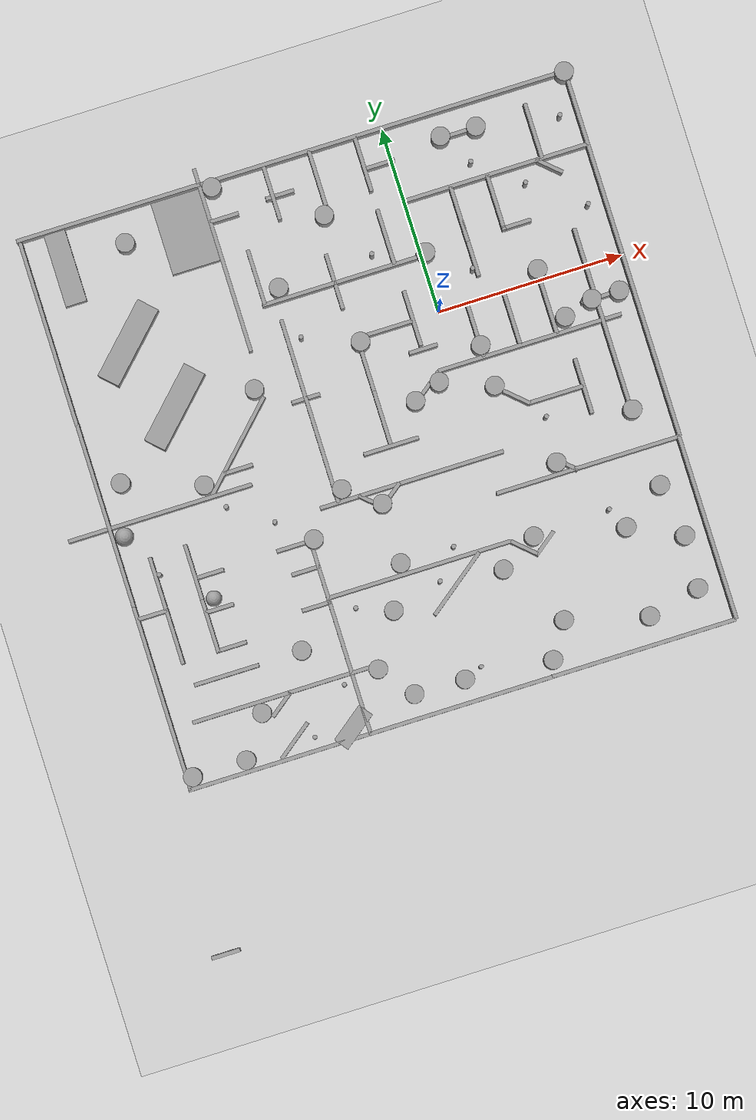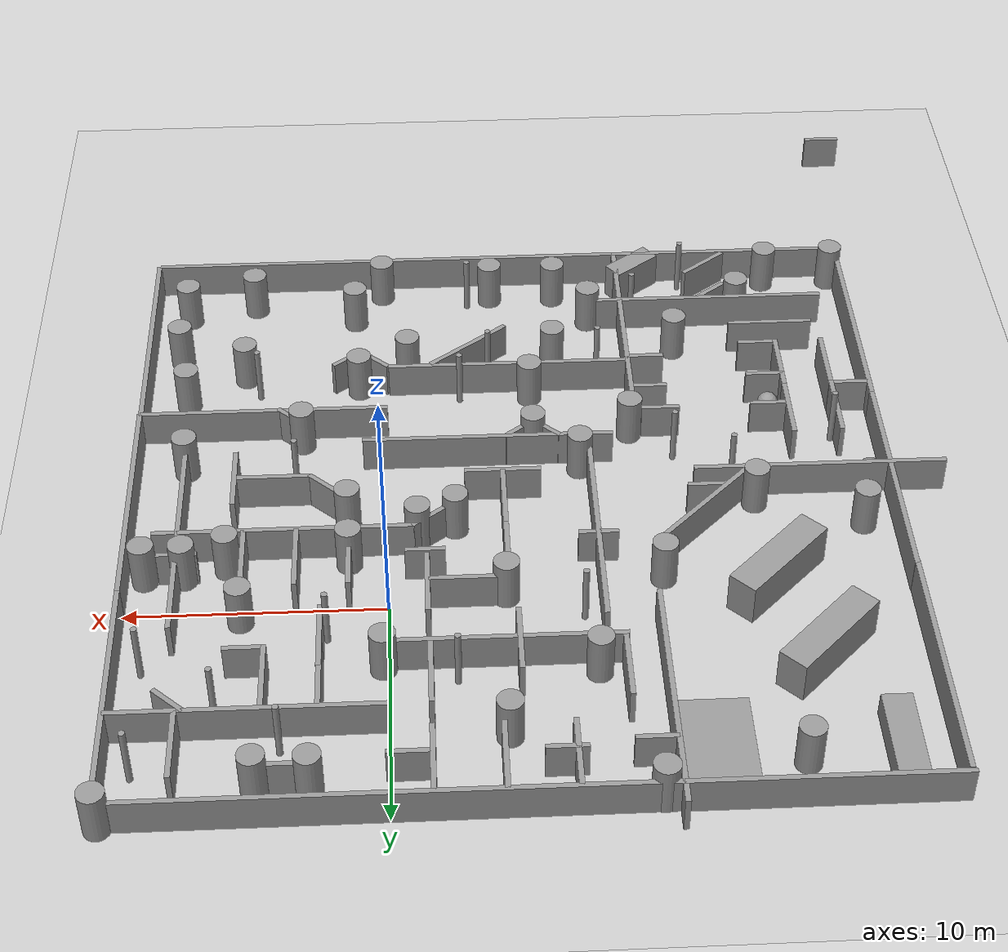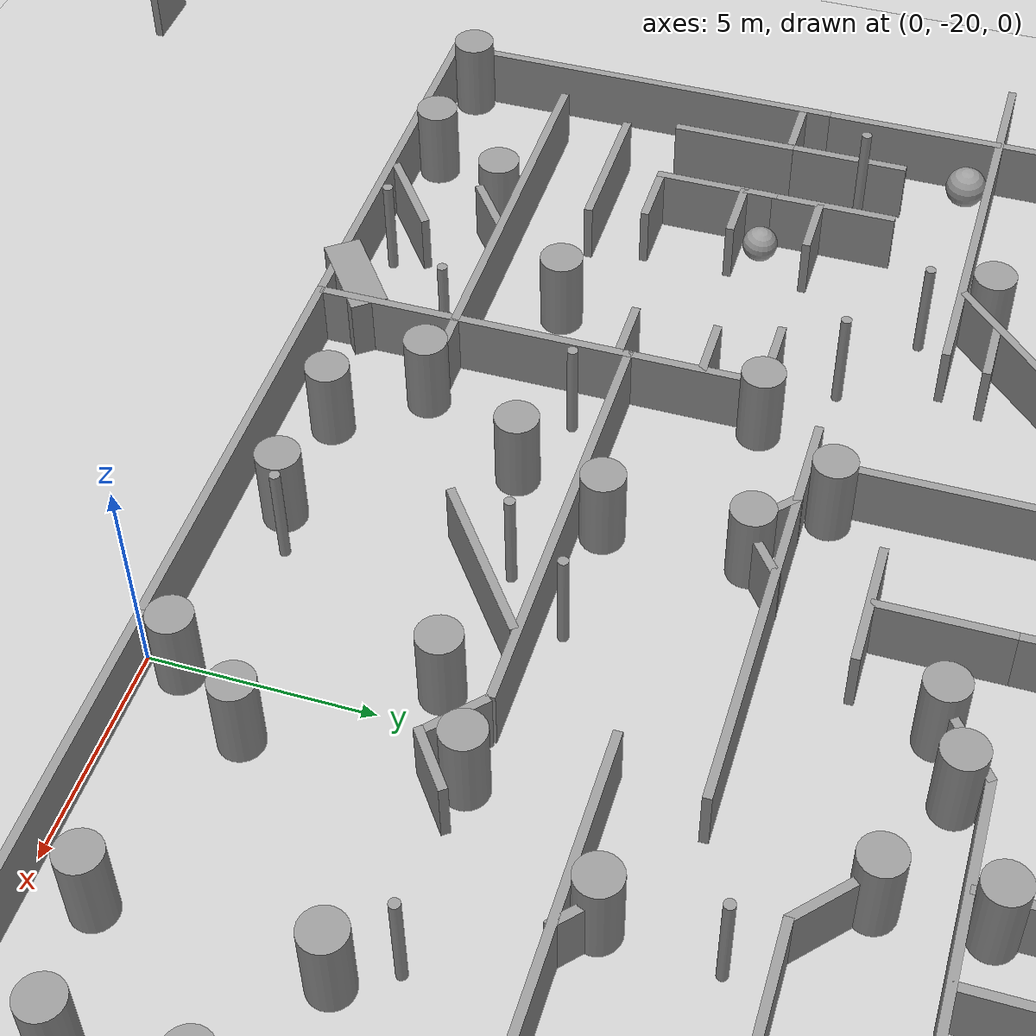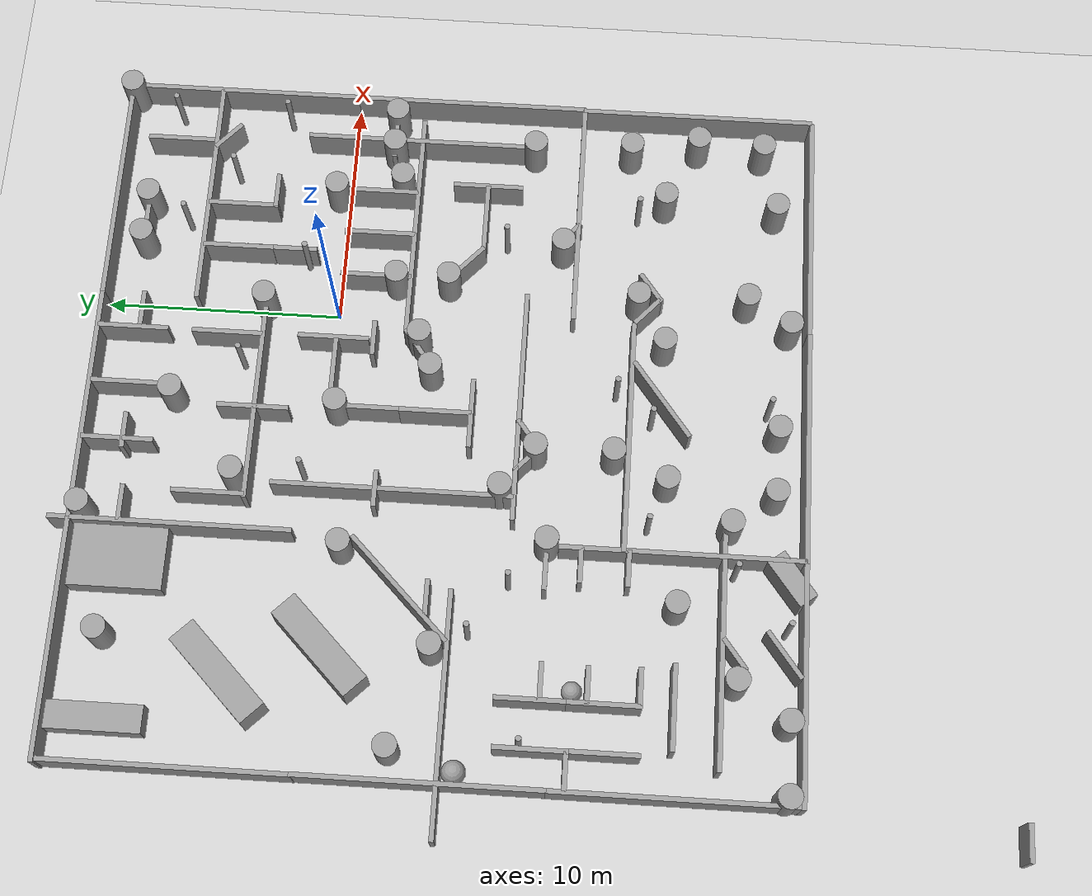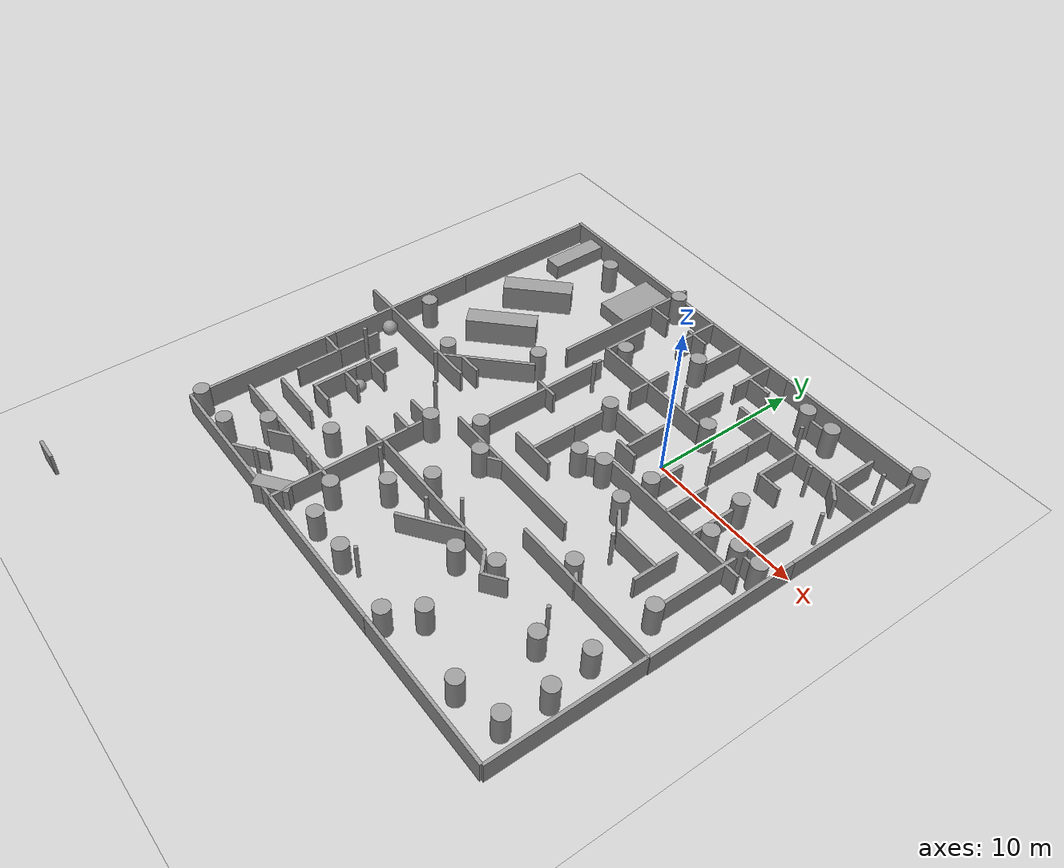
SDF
<sdf version="1.7">
 <world name="default">
  <light name="sun" type="directional">
   <pose>0 0 10 0 -0 0</pose>
   <diffuse>0.8 0.8 0.8 1</diffuse>
   <specular>0.2 0.2 0.2 1</specular>
   <attenuation>
    <range>1000</range>
    <constant>0.9</constant>
    <linear>0.01</linear>
    <quadratic>0.001</quadratic>
   </attenuation>
   <direction>-0.5 0.1 -0.9</direction>
   <spot><inner_angle>0</inner_angle><outer_angle>0</outer_angle><falloff>0</falloff></spot>
  </light>
  <model name="ground_plane">
   <static>1</static>
   <link name="link">
    <collision name="collision">
     <geometry><plane><normal>0 0 1</normal><size>100 100</size></plane></geometry>
     <surface><friction><ode><mu>100</mu><mu2>50</mu2></ode></friction></surface>
    </collision>
    <visual name="visual">
     <cast_shadows>0</cast_shadows>
     <geometry><plane><normal>0 0 1</normal><size>100 100</size></plane></geometry>
     <material>
      <script><uri>file://media/materials/scripts/gazebo.material</uri><name>Gazebo/Grey</name></script>
     </material>
    </visual>
   </link>
  </model>
  <gravity>0 0 -9.8</gravity>
  <magnetic_field>6e-06 2.3e-05 -4.2e-05</magnetic_field>
  <atmosphere type="adiabatic"/>
  <physics type="ode">
   <max_step_size>0.001</max_step_size>
   <real_time_factor>1</real_time_factor>
   <real_time_update_rate>1000</real_time_update_rate>
  </physics>
  <scene><ambient>0.4 0.4 0.4 1</ambient><background>0.7 0.7 0.7 1</background><shadows>1</shadows></scene>
  <spherical_coordinates>
   <surface_model>EARTH_WGS84</surface_model>
   <latitude_deg>0</latitude_deg>
   <longitude_deg>0</longitude_deg>
   <elevation>0</elevation>
   <heading_deg>0</heading_deg>
  </spherical_coordinates>
  <model name="wall_10x3">
   <link name="link">
    <inertial>
     <mass>1</mass>
     <inertia>
      <ixx>0.166667</ixx>
      <ixy>0</ixy>
      <ixz>0</ixz>
      <iyy>0.166667</iyy>
      <iyz>0</iyz>
      <izz>0.166667</izz>
     </inertia>
    </inertial>
    <visual name="visual">
     <geometry><box><size>10 0.2 1.5</size></box></geometry>
     <material>
      <script><name>Gazebo/Grey</name><uri>file://media/materials/scripts/gazebo.material</uri></script>
      <shader type="pixel"><normal_map>__default__</normal_map></shader>
      <ambient>0.3 0.3 0.3 1</ambient>
      <diffuse>0.7 0.7 0.7 1</diffuse>
      <specular>0.01 0.01 0.01 1</specular>
      <emissive>0 0 0 1</emissive>
     </material>
    </visual>
    <collision name="collision">
     <geometry><box><size>10 0.2 1.5</size></box></geometry>
     <surface>
      <friction>
       <ode><mu>1</mu><mu2>1</mu2><fdir1>0 0 0</fdir1><slip1>0</slip1><slip2>0</slip2></ode>
       <torsional>
        <coefficient>1</coefficient>
        <patch_radius>0</patch_radius>
        <surface_radius>0</surface_radius>
        <use_patch_radius>1</use_patch_radius>
        <ode><slip>0</slip></ode>
       </torsional>
      </friction>
      <bounce><restitution_coefficient>0</restitution_coefficient><threshold>1e+06</threshold></bounce>
      <contact>
       <collide_without_contact>0</collide_without_contact>
       <collide_without_contact_bitmask>1</collide_without_contact_bitmask>
       <collide_bitmask>1</collide_bitmask>
       <ode>
        <soft_cfm>0</soft_cfm>
        <soft_erp>0.2</soft_erp>
        <kp>1e+13</kp>
        <kd>1</kd>
        <max_vel>0.01</max_vel>
        <min_depth>0</min_depth>
       </ode>
       <bullet>
        <split_impulse>1</split_impulse>
        <split_impulse_penetration_threshold>-0.01</split_impulse_penetration_threshold>
        <soft_cfm>0</soft_cfm>
        <soft_erp>0.2</soft_erp>
        <kp>1e+13</kp>
        <kd>1</kd>
       </bullet>
      </contact>
     </surface>
    </collision>
   </link>
   <static>1</static>
   <pose>5 10 0.75 0 -0 0</pose>
  </model>
  <model name="wall_10x3_clone">
   <link name="link">
    <inertial>
     <mass>1</mass>
     <inertia>
      <ixx>0.166667</ixx>
      <ixy>0</ixy>
      <ixz>0</ixz>
      <iyy>0.166667</iyy>
      <iyz>0</iyz>
      <izz>0.166667</izz>
     </inertia>
    </inertial>
    <visual name="visual">
     <geometry><box><size>10 0.2 1.5</size></box></geometry>
     <material>
      <script><name>Gazebo/Grey</name><uri>file://media/materials/scripts/gazebo.material</uri></script>
      <shader type="pixel"><normal_map>__default__</normal_map></shader>
      <ambient>0.3 0.3 0.3 1</ambient>
      <diffuse>0.7 0.7 0.7 1</diffuse>
      <specular>0.01 0.01 0.01 1</specular>
      <emissive>0 0 0 1</emissive>
     </material>
    </visual>
    <collision name="collision">
     <geometry><box><size>10 0.2 1.5</size></box></geometry>
     <surface>
      <friction>
       <ode><mu>1</mu><mu2>1</mu2><fdir1>0 0 0</fdir1><slip1>0</slip1><slip2>0</slip2></ode>
       <torsional>
        <coefficient>1</coefficient>
        <patch_radius>0</patch_radius>
        <surface_radius>0</surface_radius>
        <use_patch_radius>1</use_patch_radius>
        <ode><slip>0</slip></ode>
       </torsional>
      </friction>
      <bounce><restitution_coefficient>0</restitution_coefficient><threshold>1e+06</threshold></bounce>
      <contact>
       <collide_without_contact>0</collide_without_contact>
       <collide_without_contact_bitmask>1</collide_without_contact_bitmask>
       <collide_bitmask>1</collide_bitmask>
       <ode>
        <soft_cfm>0</soft_cfm>
        <soft_erp>0.2</soft_erp>
        <kp>1e+13</kp>
        <kd>1</kd>
        <max_vel>0.01</max_vel>
        <min_depth>0</min_depth>
       </ode>
       <bullet>
        <split_impulse>1</split_impulse>
        <split_impulse_penetration_threshold>-0.01</split_impulse_penetration_threshold>
        <soft_cfm>0</soft_cfm>
        <soft_erp>0.2</soft_erp>
        <kp>1e+13</kp>
        <kd>1</kd>
       </bullet>
      </contact>
     </surface>
    </collision>
   </link>
   <static>1</static>
   <pose>-5 10 0.75 0 -0 0</pose>
  </model>
  <model name="wall_10x3_clone_0">
   <link name="link">
    <inertial>
     <mass>1</mass>
     <inertia>
      <ixx>0.166667</ixx>
      <ixy>0</ixy>
      <ixz>0</ixz>
      <iyy>0.166667</iyy>
      <iyz>0</iyz>
      <izz>0.166667</izz>
     </inertia>
    </inertial>
    <visual name="visual">
     <geometry><box><size>10 0.2 1.5</size></box></geometry>
     <material>
      <script><name>Gazebo/Grey</name><uri>file://media/materials/scripts/gazebo.material</uri></script>
      <shader type="pixel"><normal_map>__default__</normal_map></shader>
      <ambient>0.3 0.3 0.3 1</ambient>
      <diffuse>0.7 0.7 0.7 1</diffuse>
      <specular>0.01 0.01 0.01 1</specular>
      <emissive>0 0 0 1</emissive>
     </material>
    </visual>
    <collision name="collision">
     <geometry><box><size>10 0.2 1.5</size></box></geometry>
     <surface>
      <friction>
       <ode><mu>1</mu><mu2>1</mu2><fdir1>0 0 0</fdir1><slip1>0</slip1><slip2>0</slip2></ode>
       <torsional>
        <coefficient>1</coefficient>
        <patch_radius>0</patch_radius>
        <surface_radius>0</surface_radius>
        <use_patch_radius>1</use_patch_radius>
        <ode><slip>0</slip></ode>
       </torsional>
      </friction>
      <bounce><restitution_coefficient>0</restitution_coefficient><threshold>1e+06</threshold></bounce>
      <contact>
       <collide_without_contact>0</collide_without_contact>
       <collide_without_contact_bitmask>1</collide_without_contact_bitmask>
       <collide_bitmask>1</collide_bitmask>
       <ode>
        <soft_cfm>0</soft_cfm>
        <soft_erp>0.2</soft_erp>
        <kp>1e+13</kp>
        <kd>1</kd>
        <max_vel>0.01</max_vel>
        <min_depth>0</min_depth>
       </ode>
       <bullet>
        <split_impulse>1</split_impulse>
        <split_impulse_penetration_threshold>-0.01</split_impulse_penetration_threshold>
        <soft_cfm>0</soft_cfm>
        <soft_erp>0.2</soft_erp>
        <kp>1e+13</kp>
        <kd>1</kd>
       </bullet>
      </contact>
     </surface>
    </collision>
   </link>
   <static>1</static>
   <pose>-5.04868 -12.5865 0.75 0 -0 0</pose>
  </model>
  <model name="wall_10x3_clone_1">
   <link name="link">
    <inertial>
     <mass>1</mass>
     <inertia>
      <ixx>0.166667</ixx>
      <ixy>0</ixy>
      <ixz>0</ixz>
      <iyy>0.166667</iyy>
      <iyz>0</iyz>
      <izz>0.166667</izz>
     </inertia>
    </inertial>
    <visual name="visual">
     <geometry><box><size>10 0.2 1.5</size></box></geometry>
     <material>
      <script><name>Gazebo/Grey</name><uri>file://media/materials/scripts/gazebo.material</uri></script>
      <shader type="pixel"><normal_map>__default__</normal_map></shader>
      <ambient>0.3 0.3 0.3 1</ambient>
      <diffuse>0.7 0.7 0.7 1</diffuse>
      <specular>0.01 0.01 0.01 1</specular>
      <emissive>0 0 0 1</emissive>
     </material>
    </visual>
    <collision name="collision">
     <geometry><box><size>10 0.2 1.5</size></box></geometry>
     <surface>
      <friction>
       <ode><mu>1</mu><mu2>1</mu2><fdir1>0 0 0</fdir1><slip1>0</slip1><slip2>0</slip2></ode>
       <torsional>
        <coefficient>1</coefficient>
        <patch_radius>0</patch_radius>
        <surface_radius>0</surface_radius>
        <use_patch_radius>1</use_patch_radius>
        <ode><slip>0</slip></ode>
       </torsional>
      </friction>
      <bounce><restitution_coefficient>0</restitution_coefficient><threshold>1e+06</threshold></bounce>
      <contact>
       <collide_without_contact>0</collide_without_contact>
       <collide_without_contact_bitmask>1</collide_without_contact_bitmask>
       <collide_bitmask>1</collide_bitmask>
       <ode>
        <soft_cfm>0</soft_cfm>
        <soft_erp>0.2</soft_erp>
        <kp>1e+13</kp>
        <kd>1</kd>
        <max_vel>0.01</max_vel>
        <min_depth>0</min_depth>
       </ode>
       <bullet>
        <split_impulse>1</split_impulse>
        <split_impulse_penetration_threshold>-0.01</split_impulse_penetration_threshold>
        <soft_cfm>0</soft_cfm>
        <soft_erp>0.2</soft_erp>
        <kp>1e+13</kp>
        <kd>1</kd>
       </bullet>
      </contact>
     </surface>
    </collision>
   </link>
   <static>1</static>
   <pose>5 -10 0.75 0 -0 0</pose>
  </model>
  <model name="wall_10x3_clone_2">
   <link name="link">
    <inertial>
     <mass>1</mass>
     <inertia>
      <ixx>0.166667</ixx>
      <ixy>0</ixy>
      <ixz>0</ixz>
      <iyy>0.166667</iyy>
      <iyz>0</iyz>
      <izz>0.166667</izz>
     </inertia>
    </inertial>
    <visual name="visual">
     <geometry><box><size>10 0.2 1.5</size></box></geometry>
     <material>
      <script><name>Gazebo/Grey</name><uri>file://media/materials/scripts/gazebo.material</uri></script>
      <shader type="pixel"><normal_map>__default__</normal_map></shader>
      <ambient>0.3 0.3 0.3 1</ambient>
      <diffuse>0.7 0.7 0.7 1</diffuse>
      <specular>0.01 0.01 0.01 1</specular>
      <emissive>0 0 0 1</emissive>
     </material>
    </visual>
    <collision name="collision">
     <geometry><box><size>10 0.2 1.5</size></box></geometry>
     <surface>
      <friction>
       <ode><mu>1</mu><mu2>1</mu2><fdir1>0 0 0</fdir1><slip1>0</slip1><slip2>0</slip2></ode>
       <torsional>
        <coefficient>1</coefficient>
        <patch_radius>0</patch_radius>
        <surface_radius>0</surface_radius>
        <use_patch_radius>1</use_patch_radius>
        <ode><slip>0</slip></ode>
       </torsional>
      </friction>
      <bounce><restitution_coefficient>0</restitution_coefficient><threshold>1e+06</threshold></bounce>
      <contact>
       <collide_without_contact>0</collide_without_contact>
       <collide_without_contact_bitmask>1</collide_without_contact_bitmask>
       <collide_bitmask>1</collide_bitmask>
       <ode>
        <soft_cfm>0</soft_cfm>
        <soft_erp>0.2</soft_erp>
        <kp>1e+13</kp>
        <kd>1</kd>
        <max_vel>0.01</max_vel>
        <min_depth>0</min_depth>
       </ode>
       <bullet>
        <split_impulse>1</split_impulse>
        <split_impulse_penetration_threshold>-0.01</split_impulse_penetration_threshold>
        <soft_cfm>0</soft_cfm>
        <soft_erp>0.2</soft_erp>
        <kp>1e+13</kp>
        <kd>1</kd>
       </bullet>
      </contact>
     </surface>
    </collision>
   </link>
   <static>1</static>
   <pose>5 6 0.75 0 -0 0</pose>
  </model>
  <model name="wall_10x3_clone_3_clone">
   <link name="link">
    <inertial>
     <mass>1</mass>
     <inertia>
      <ixx>0.166667</ixx>
      <ixy>0</ixy>
      <ixz>0</ixz>
      <iyy>0.166667</iyy>
      <iyz>0</iyz>
      <izz>0.166667</izz>
     </inertia>
    </inertial>
    <visual name="visual">
     <geometry><box><size>10 0.2 1.5</size></box></geometry>
     <material>
      <script><name>Gazebo/Grey</name><uri>file://media/materials/scripts/gazebo.material</uri></script>
      <shader type="pixel"><normal_map>__default__</normal_map></shader>
      <ambient>0.3 0.3 0.3 1</ambient>
      <diffuse>0.7 0.7 0.7 1</diffuse>
      <specular>0.01 0.01 0.01 1</specular>
      <emissive>0 0 0 1</emissive>
     </material>
    </visual>
    <collision name="collision">
     <geometry><box><size>10 0.2 1.5</size></box></geometry>
     <surface>
      <friction>
       <ode><mu>1</mu><mu2>1</mu2><fdir1>0 0 0</fdir1><slip1>0</slip1><slip2>0</slip2></ode>
       <torsional>
        <coefficient>1</coefficient>
        <patch_radius>0</patch_radius>
        <surface_radius>0</surface_radius>
        <use_patch_radius>1</use_patch_radius>
        <ode><slip>0</slip></ode>
       </torsional>
      </friction>
      <bounce><restitution_coefficient>0</restitution_coefficient><threshold>1e+06</threshold></bounce>
      <contact>
       <collide_without_contact>0</collide_without_contact>
       <collide_without_contact_bitmask>1</collide_without_contact_bitmask>
       <collide_bitmask>1</collide_bitmask>
       <ode>
        <soft_cfm>0</soft_cfm>
        <soft_erp>0.2</soft_erp>
        <kp>1e+13</kp>
        <kd>1</kd>
        <max_vel>0.01</max_vel>
        <min_depth>0</min_depth>
       </ode>
       <bullet>
        <split_impulse>1</split_impulse>
        <split_impulse_penetration_threshold>-0.01</split_impulse_penetration_threshold>
        <soft_cfm>0</soft_cfm>
        <soft_erp>0.2</soft_erp>
        <kp>1e+13</kp>
        <kd>1</kd>
       </bullet>
      </contact>
     </surface>
    </collision>
   </link>
   <static>1</static>
   <pose>-10 5.88215 0.75 0 -0 1.5708</pose>
  </model>
  <model name="wall_10x3_clone_3_clone_0">
   <link name="link">
    <inertial>
     <mass>1</mass>
     <inertia>
      <ixx>0.166667</ixx>
      <ixy>0</ixy>
      <ixz>0</ixz>
      <iyy>0.166667</iyy>
      <iyz>0</iyz>
      <izz>0.166667</izz>
     </inertia>
    </inertial>
    <visual name="visual">
     <geometry><box><size>10 0.2 1.5</size></box></geometry>
     <material>
      <script><name>Gazebo/Grey</name><uri>file://media/materials/scripts/gazebo.material</uri></script>
      <shader type="pixel"><normal_map>__default__</normal_map></shader>
      <ambient>0.3 0.3 0.3 1</ambient>
      <diffuse>0.7 0.7 0.7 1</diffuse>
      <specular>0.01 0.01 0.01 1</specular>
      <emissive>0 0 0 1</emissive>
     </material>
    </visual>
    <collision name="collision">
     <geometry><box><size>10 0.2 1.5</size></box></geometry>
     <surface>
      <friction>
       <ode><mu>1</mu><mu2>1</mu2><fdir1>0 0 0</fdir1><slip1>0</slip1><slip2>0</slip2></ode>
       <torsional>
        <coefficient>1</coefficient>
        <patch_radius>0</patch_radius>
        <surface_radius>0</surface_radius>
        <use_patch_radius>1</use_patch_radius>
        <ode><slip>0</slip></ode>
       </torsional>
      </friction>
      <bounce><restitution_coefficient>0</restitution_coefficient><threshold>1e+06</threshold></bounce>
      <contact>
       <collide_without_contact>0</collide_without_contact>
       <collide_without_contact_bitmask>1</collide_without_contact_bitmask>
       <collide_bitmask>1</collide_bitmask>
       <ode>
        <soft_cfm>0</soft_cfm>
        <soft_erp>0.2</soft_erp>
        <kp>1e+13</kp>
        <kd>1</kd>
        <max_vel>0.01</max_vel>
        <min_depth>0</min_depth>
       </ode>
       <bullet>
        <split_impulse>1</split_impulse>
        <split_impulse_penetration_threshold>-0.01</split_impulse_penetration_threshold>
        <soft_cfm>0</soft_cfm>
        <soft_erp>0.2</soft_erp>
        <kp>1e+13</kp>
        <kd>1</kd>
       </bullet>
      </contact>
     </surface>
    </collision>
   </link>
   <static>1</static>
   <pose>10 -5 0.75 0 -0 1.5708</pose>
  </model>
  <model name="wall_10x3_clone_3_clone_1">
   <link name="link">
    <inertial>
     <mass>1</mass>
     <inertia>
      <ixx>0.166667</ixx>
      <ixy>0</ixy>
      <ixz>0</ixz>
      <iyy>0.166667</iyy>
      <iyz>0</iyz>
      <izz>0.166667</izz>
     </inertia>
    </inertial>
    <visual name="visual">
     <geometry><box><size>10 0.2 1.5</size></box></geometry>
     <material>
      <script><name>Gazebo/Grey</name><uri>file://media/materials/scripts/gazebo.material</uri></script>
      <shader type="pixel"><normal_map>__default__</normal_map></shader>
      <ambient>0.3 0.3 0.3 1</ambient>
      <diffuse>0.7 0.7 0.7 1</diffuse>
      <specular>0.01 0.01 0.01 1</specular>
      <emissive>0 0 0 1</emissive>
     </material>
    </visual>
    <collision name="collision">
     <geometry><box><size>10 0.2 1.5</size></box></geometry>
     <surface>
      <friction>
       <ode><mu>1</mu><mu2>1</mu2><fdir1>0 0 0</fdir1><slip1>0</slip1><slip2>0</slip2></ode>
       <torsional>
        <coefficient>1</coefficient>
        <patch_radius>0</patch_radius>
        <surface_radius>0</surface_radius>
        <use_patch_radius>1</use_patch_radius>
        <ode><slip>0</slip></ode>
       </torsional>
      </friction>
      <bounce><restitution_coefficient>0</restitution_coefficient><threshold>1e+06</threshold></bounce>
      <contact>
       <collide_without_contact>0</collide_without_contact>
       <collide_without_contact_bitmask>1</collide_without_contact_bitmask>
       <collide_bitmask>1</collide_bitmask>
       <ode>
        <soft_cfm>0</soft_cfm>
        <soft_erp>0.2</soft_erp>
        <kp>1e+13</kp>
        <kd>1</kd>
        <max_vel>0.01</max_vel>
        <min_depth>0</min_depth>
       </ode>
       <bullet>
        <split_impulse>1</split_impulse>
        <split_impulse_penetration_threshold>-0.01</split_impulse_penetration_threshold>
        <soft_cfm>0</soft_cfm>
        <soft_erp>0.2</soft_erp>
        <kp>1e+13</kp>
        <kd>1</kd>
       </bullet>
      </contact>
     </surface>
    </collision>
   </link>
   <static>1</static>
   <pose>10 5 0.75 0 -0 1.5708</pose>
  </model>
  <model name="wall_10x3_clone_2_clone">
   <link name="link">
    <inertial>
     <mass>1</mass>
     <inertia>
      <ixx>0.166667</ixx>
      <ixy>0</ixy>
      <ixz>0</ixz>
      <iyy>0.166667</iyy>
      <iyz>0</iyz>
      <izz>0.166667</izz>
     </inertia>
    </inertial>
    <visual name="visual">
     <geometry><box><size>10 0.2 1.5</size></box></geometry>
     <material>
      <script><name>Gazebo/Grey</name><uri>file://media/materials/scripts/gazebo.material</uri></script>
      <shader type="pixel"><normal_map>__default__</normal_map></shader>
      <ambient>0.3 0.3 0.3 1</ambient>
      <diffuse>0.7 0.7 0.7 1</diffuse>
      <specular>0.01 0.01 0.01 1</specular>
      <emissive>0 0 0 1</emissive>
     </material>
    </visual>
    <collision name="collision">
     <geometry><box><size>10 0.2 1.5</size></box></geometry>
     <surface>
      <friction>
       <ode><mu>1</mu><mu2>1</mu2><fdir1>0 0 0</fdir1><slip1>0</slip1><slip2>0</slip2></ode>
       <torsional>
        <coefficient>1</coefficient>
        <patch_radius>0</patch_radius>
        <surface_radius>0</surface_radius>
        <use_patch_radius>1</use_patch_radius>
        <ode><slip>0</slip></ode>
       </torsional>
      </friction>
      <bounce><restitution_coefficient>0</restitution_coefficient><threshold>1e+06</threshold></bounce>
      <contact>
       <collide_without_contact>0</collide_without_contact>
       <collide_without_contact_bitmask>1</collide_without_contact_bitmask>
       <collide_bitmask>1</collide_bitmask>
       <ode>
        <soft_cfm>0</soft_cfm>
        <soft_erp>0.2</soft_erp>
        <kp>1e+13</kp>
        <kd>1</kd>
        <max_vel>0.01</max_vel>
        <min_depth>0</min_depth>
       </ode>
       <bullet>
        <split_impulse>1</split_impulse>
        <split_impulse_penetration_threshold>-0.01</split_impulse_penetration_threshold>
        <soft_cfm>0</soft_cfm>
        <soft_erp>0.2</soft_erp>
        <kp>1e+13</kp>
        <kd>1</kd>
       </bullet>
      </contact>
     </surface>
    </collision>
   </link>
   <static>1</static>
   <pose>-4 -8 0.75 0 -0 0</pose>
  </model>
  <model name="wall_10x3_clone_2_clone_0">
   <link name="link">
    <inertial>
     <mass>1</mass>
     <inertia>
      <ixx>0.166667</ixx>
      <ixy>0</ixy>
      <ixz>0</ixz>
      <iyy>0.166667</iyy>
      <iyz>0</iyz>
      <izz>0.166667</izz>
     </inertia>
    </inertial>
    <visual name="visual">
     <geometry><box><size>8.43878 0.2 1.5</size></box></geometry>
     <material>
      <script><name>Gazebo/Grey</name><uri>file://media/materials/scripts/gazebo.material</uri></script>
      <shader type="pixel"><normal_map>__default__</normal_map></shader>
      <ambient>0.3 0.3 0.3 1</ambient>
      <diffuse>0.7 0.7 0.7 1</diffuse>
      <specular>0.01 0.01 0.01 1</specular>
      <emissive>0 0 0 1</emissive>
     </material>
    </visual>
    <collision name="collision">
     <geometry><box><size>8.43878 0.2 1.5</size></box></geometry>
     <surface>
      <friction>
       <ode><mu>1</mu><mu2>1</mu2><fdir1>0 0 0</fdir1><slip1>0</slip1><slip2>0</slip2></ode>
       <torsional>
        <coefficient>1</coefficient>
        <patch_radius>0</patch_radius>
        <surface_radius>0</surface_radius>
        <use_patch_radius>1</use_patch_radius>
        <ode><slip>0</slip></ode>
       </torsional>
      </friction>
      <bounce><restitution_coefficient>0</restitution_coefficient><threshold>1e+06</threshold></bounce>
      <contact>
       <collide_without_contact>0</collide_without_contact>
       <collide_without_contact_bitmask>1</collide_without_contact_bitmask>
       <collide_bitmask>1</collide_bitmask>
       <ode>
        <soft_cfm>0</soft_cfm>
        <soft_erp>0.2</soft_erp>
        <kp>1e+13</kp>
        <kd>1</kd>
        <max_vel>0.01</max_vel>
        <min_depth>0</min_depth>
       </ode>
       <bullet>
        <split_impulse>1</split_impulse>
        <split_impulse_penetration_threshold>-0.01</split_impulse_penetration_threshold>
        <soft_cfm>0</soft_cfm>
        <soft_erp>0.2</soft_erp>
        <kp>1e+13</kp>
        <kd>1</kd>
       </bullet>
      </contact>
     </surface>
    </collision>
   </link>
   <static>1</static>
   <pose>-4.5 3 0.75 0 -0 0</pose>
  </model>
  <model name="wall_10x3_clone_2_clone_1">
   <link name="link">
    <inertial>
     <mass>1</mass>
     <inertia>
      <ixx>0.166667</ixx>
      <ixy>0</ixy>
      <ixz>0</ixz>
      <iyy>0.166667</iyy>
      <iyz>0</iyz>
      <izz>0.166667</izz>
     </inertia>
    </inertial>
    <visual name="visual">
     <geometry><box><size>10 0.2 1.5</size></box></geometry>
     <material>
      <script><name>Gazebo/Grey</name><uri>file://media/materials/scripts/gazebo.material</uri></script>
      <shader type="pixel"><normal_map>__default__</normal_map></shader>
      <ambient>0.3 0.3 0.3 1</ambient>
      <diffuse>0.7 0.7 0.7 1</diffuse>
      <specular>0.01 0.01 0.01 1</specular>
      <emissive>0 0 0 1</emissive>
     </material>
    </visual>
    <collision name="collision">
     <geometry><box><size>10 0.2 1.5</size></box></geometry>
     <surface>
      <friction>
       <ode><mu>1</mu><mu2>1</mu2><fdir1>0 0 0</fdir1><slip1>0</slip1><slip2>0</slip2></ode>
       <torsional>
        <coefficient>1</coefficient>
        <patch_radius>0</patch_radius>
        <surface_radius>0</surface_radius>
        <use_patch_radius>1</use_patch_radius>
        <ode><slip>0</slip></ode>
       </torsional>
      </friction>
      <bounce><restitution_coefficient>0</restitution_coefficient><threshold>1e+06</threshold></bounce>
      <contact>
       <collide_without_contact>0</collide_without_contact>
       <collide_without_contact_bitmask>1</collide_without_contact_bitmask>
       <collide_bitmask>1</collide_bitmask>
       <ode>
        <soft_cfm>0</soft_cfm>
        <soft_erp>0.2</soft_erp>
        <kp>1e+13</kp>
        <kd>1</kd>
        <max_vel>0.01</max_vel>
        <min_depth>0</min_depth>
       </ode>
       <bullet>
        <split_impulse>1</split_impulse>
        <split_impulse_penetration_threshold>-0.01</split_impulse_penetration_threshold>
        <soft_cfm>0</soft_cfm>
        <soft_erp>0.2</soft_erp>
        <kp>1e+13</kp>
        <kd>1</kd>
       </bullet>
      </contact>
     </surface>
    </collision>
   </link>
   <static>1</static>
   <pose>4 -3 0.75 0 -0 0</pose>
  </model>
  <model name="wall_10x3_clone_3_clone_0_clone">
   <link name="link">
    <inertial>
     <mass>1</mass>
     <inertia>
      <ixx>0.166667</ixx>
      <ixy>0</ixy>
      <ixz>0</ixz>
      <iyy>0.166667</iyy>
      <iyz>0</iyz>
      <izz>0.166667</izz>
     </inertia>
    </inertial>
    <visual name="visual">
     <geometry><box><size>10 0.2 1.5</size></box></geometry>
     <material>
      <script><name>Gazebo/Grey</name><uri>file://media/materials/scripts/gazebo.material</uri></script>
      <shader type="pixel"><normal_map>__default__</normal_map></shader>
      <ambient>0.3 0.3 0.3 1</ambient>
      <diffuse>0.7 0.7 0.7 1</diffuse>
      <specular>0.01 0.01 0.01 1</specular>
      <emissive>0 0 0 1</emissive>
     </material>
    </visual>
    <collision name="collision">
     <geometry><box><size>10 0.2 1.5</size></box></geometry>
     <surface>
      <friction>
       <ode><mu>1</mu><mu2>1</mu2><fdir1>0 0 0</fdir1><slip1>0</slip1><slip2>0</slip2></ode>
       <torsional>
        <coefficient>1</coefficient>
        <patch_radius>0</patch_radius>
        <surface_radius>0</surface_radius>
        <use_patch_radius>1</use_patch_radius>
        <ode><slip>0</slip></ode>
       </torsional>
      </friction>
      <bounce><restitution_coefficient>0</restitution_coefficient><threshold>1e+06</threshold></bounce>
      <contact>
       <collide_without_contact>0</collide_without_contact>
       <collide_without_contact_bitmask>1</collide_without_contact_bitmask>
       <collide_bitmask>1</collide_bitmask>
       <ode>
        <soft_cfm>0</soft_cfm>
        <soft_erp>0.2</soft_erp>
        <kp>1e+13</kp>
        <kd>1</kd>
        <max_vel>0.01</max_vel>
        <min_depth>0</min_depth>
       </ode>
       <bullet>
        <split_impulse>1</split_impulse>
        <split_impulse_penetration_threshold>-0.01</split_impulse_penetration_threshold>
        <soft_cfm>0</soft_cfm>
        <soft_erp>0.2</soft_erp>
        <kp>1e+13</kp>
        <kd>1</kd>
       </bullet>
      </contact>
     </surface>
    </collision>
   </link>
   <static>1</static>
   <pose>8 -3 0.75 0 -0 1.5708</pose>
  </model>
  <model name="wall_10x3_clone_3_clone_0_clone_clone_clone_clone_0">
   <link name="link">
    <inertial>
     <mass>1</mass>
     <inertia>
      <ixx>0.166667</ixx>
      <ixy>0</ixy>
      <ixz>0</ixz>
      <iyy>0.166667</iyy>
      <iyz>0</iyz>
      <izz>0.166667</izz>
     </inertia>
    </inertial>
    <visual name="visual">
     <geometry><box><size>3 0.2 1.5</size></box></geometry>
     <material>
      <script><name>Gazebo/Grey</name><uri>file://media/materials/scripts/gazebo.material</uri></script>
      <shader type="pixel"><normal_map>__default__</normal_map></shader>
      <ambient>0.3 0.3 0.3 1</ambient>
      <diffuse>0.7 0.7 0.7 1</diffuse>
      <specular>0.01 0.01 0.01 1</specular>
      <emissive>0 0 0 1</emissive>
     </material>
    </visual>
    <collision name="collision">
     <geometry><box><size>3 0.2 1.5</size></box></geometry>
     <surface>
      <friction>
       <ode><mu>1</mu><mu2>1</mu2><fdir1>0 0 0</fdir1><slip1>0</slip1><slip2>0</slip2></ode>
       <torsional>
        <coefficient>1</coefficient>
        <patch_radius>0</patch_radius>
        <surface_radius>0</surface_radius>
        <use_patch_radius>1</use_patch_radius>
        <ode><slip>0</slip></ode>
       </torsional>
      </friction>
      <bounce><restitution_coefficient>0</restitution_coefficient><threshold>1e+06</threshold></bounce>
      <contact>
       <collide_without_contact>0</collide_without_contact>
       <collide_without_contact_bitmask>1</collide_without_contact_bitmask>
       <collide_bitmask>1</collide_bitmask>
       <ode>
        <soft_cfm>0</soft_cfm>
        <soft_erp>0.2</soft_erp>
        <kp>1e+13</kp>
        <kd>1</kd>
        <max_vel>0.01</max_vel>
        <min_depth>0</min_depth>
       </ode>
       <bullet>
        <split_impulse>1</split_impulse>
        <split_impulse_penetration_threshold>-0.01</split_impulse_penetration_threshold>
        <soft_cfm>0</soft_cfm>
        <soft_erp>0.2</soft_erp>
        <kp>1e+13</kp>
        <kd>1</kd>
       </bullet>
      </contact>
     </surface>
    </collision>
   </link>
   <static>1</static>
   <pose>6 -6 0.75 0 -0 1.5708</pose>
  </model>
  <model name="wall_10x3_clone_3_clone_0_clone_clone_clone_clone_clone">
   <link name="link">
    <inertial>
     <mass>1</mass>
     <inertia>
      <ixx>0.166667</ixx>
      <ixy>0</ixy>
      <ixz>0</ixz>
      <iyy>0.166667</iyy>
      <iyz>0</iyz>
      <izz>0.166667</izz>
     </inertia>
    </inertial>
    <visual name="visual">
     <geometry><box><size>3 0.2 1.5</size></box></geometry>
     <material>
      <script><name>Gazebo/Grey</name><uri>file://media/materials/scripts/gazebo.material</uri></script>
      <shader type="pixel"><normal_map>__default__</normal_map></shader>
      <ambient>0.3 0.3 0.3 1</ambient>
      <diffuse>0.7 0.7 0.7 1</diffuse>
      <specular>0.01 0.01 0.01 1</specular>
      <emissive>0 0 0 1</emissive>
     </material>
    </visual>
    <collision name="collision">
     <geometry><box><size>3 0.2 1.5</size></box></geometry>
     <surface>
      <friction>
       <ode><mu>1</mu><mu2>1</mu2><fdir1>0 0 0</fdir1><slip1>0</slip1><slip2>0</slip2></ode>
       <torsional>
        <coefficient>1</coefficient>
        <patch_radius>0</patch_radius>
        <surface_radius>0</surface_radius>
        <use_patch_radius>1</use_patch_radius>
        <ode><slip>0</slip></ode>
       </torsional>
      </friction>
      <bounce><restitution_coefficient>0</restitution_coefficient><threshold>1e+06</threshold></bounce>
      <contact>
       <collide_without_contact>0</collide_without_contact>
       <collide_without_contact_bitmask>1</collide_without_contact_bitmask>
       <collide_bitmask>1</collide_bitmask>
       <ode>
        <soft_cfm>0</soft_cfm>
        <soft_erp>0.2</soft_erp>
        <kp>1e+13</kp>
        <kd>1</kd>
        <max_vel>0.01</max_vel>
        <min_depth>0</min_depth>
       </ode>
       <bullet>
        <split_impulse>1</split_impulse>
        <split_impulse_penetration_threshold>-0.01</split_impulse_penetration_threshold>
        <soft_cfm>0</soft_cfm>
        <soft_erp>0.2</soft_erp>
        <kp>1e+13</kp>
        <kd>1</kd>
       </bullet>
      </contact>
     </surface>
    </collision>
   </link>
   <static>1</static>
   <pose>4.5 -6 0.75 0 -0 0</pose>
  </model>
  <model name="wall_10x3_clone_3_clone_0_clone_clone_clone_clone_clone_0">
   <link name="link">
    <inertial>
     <mass>1</mass>
     <inertia>
      <ixx>0.166667</ixx>
      <ixy>0</ixy>
      <ixz>0</ixz>
      <iyy>0.166667</iyy>
      <iyz>0</iyz>
      <izz>0.166667</izz>
     </inertia>
    </inertial>
    <visual name="visual">
     <geometry><box><size>3 0.2 1.5</size></box></geometry>
     <material>
      <script><name>Gazebo/Grey</name><uri>file://media/materials/scripts/gazebo.material</uri></script>
      <shader type="pixel"><normal_map>__default__</normal_map></shader>
      <ambient>0.3 0.3 0.3 1</ambient>
      <diffuse>0.7 0.7 0.7 1</diffuse>
      <specular>0.01 0.01 0.01 1</specular>
      <emissive>0 0 0 1</emissive>
     </material>
    </visual>
    <collision name="collision">
     <geometry><box><size>3 0.2 1.5</size></box></geometry>
     <surface>
      <friction>
       <ode><mu>1</mu><mu2>1</mu2><fdir1>0 0 0</fdir1><slip1>0</slip1><slip2>0</slip2></ode>
       <torsional>
        <coefficient>1</coefficient>
        <patch_radius>0</patch_radius>
        <surface_radius>0</surface_radius>
        <use_patch_radius>1</use_patch_radius>
        <ode><slip>0</slip></ode>
       </torsional>
      </friction>
      <bounce><restitution_coefficient>0</restitution_coefficient><threshold>1e+06</threshold></bounce>
      <contact>
       <collide_without_contact>0</collide_without_contact>
       <collide_without_contact_bitmask>1</collide_without_contact_bitmask>
       <collide_bitmask>1</collide_bitmask>
       <ode>
        <soft_cfm>0</soft_cfm>
        <soft_erp>0.2</soft_erp>
        <kp>1e+13</kp>
        <kd>1</kd>
        <max_vel>0.01</max_vel>
        <min_depth>0</min_depth>
       </ode>
       <bullet>
        <split_impulse>1</split_impulse>
        <split_impulse_penetration_threshold>-0.01</split_impulse_penetration_threshold>
        <soft_cfm>0</soft_cfm>
        <soft_erp>0.2</soft_erp>
        <kp>1e+13</kp>
        <kd>1</kd>
       </bullet>
      </contact>
     </surface>
    </collision>
   </link>
   <static>1</static>
   <pose>-4.5 -6 0.75 0 -0 0</pose>
  </model>
  <model name="wall_10x3_clone_3_clone_0_clone_clone_clone_clone_1">
   <link name="link">
    <inertial>
     <mass>1</mass>
     <inertia>
      <ixx>0.166667</ixx>
      <ixy>0</ixy>
      <ixz>0</ixz>
      <iyy>0.166667</iyy>
      <iyz>0</iyz>
      <izz>0.166667</izz>
     </inertia>
    </inertial>
    <visual name="visual">
     <geometry><box><size>3 0.2 1.5</size></box></geometry>
     <material>
      <script><name>Gazebo/Grey</name><uri>file://media/materials/scripts/gazebo.material</uri></script>
      <shader type="pixel"><normal_map>__default__</normal_map></shader>
      <ambient>0.3 0.3 0.3 1</ambient>
      <diffuse>0.7 0.7 0.7 1</diffuse>
      <specular>0.01 0.01 0.01 1</specular>
      <emissive>0 0 0 1</emissive>
     </material>
    </visual>
    <collision name="collision">
     <geometry><box><size>3 0.2 1.5</size></box></geometry>
     <surface>
      <friction>
       <ode><mu>1</mu><mu2>1</mu2><fdir1>0 0 0</fdir1><slip1>0</slip1><slip2>0</slip2></ode>
       <torsional>
        <coefficient>1</coefficient>
        <patch_radius>0</patch_radius>
        <surface_radius>0</surface_radius>
        <use_patch_radius>1</use_patch_radius>
        <ode><slip>0</slip></ode>
       </torsional>
      </friction>
      <bounce><restitution_coefficient>0</restitution_coefficient><threshold>1e+06</threshold></bounce>
      <contact>
       <collide_without_contact>0</collide_without_contact>
       <collide_without_contact_bitmask>1</collide_without_contact_bitmask>
       <collide_bitmask>1</collide_bitmask>
       <ode>
        <soft_cfm>0</soft_cfm>
        <soft_erp>0.2</soft_erp>
        <kp>1e+13</kp>
        <kd>1</kd>
        <max_vel>0.01</max_vel>
        <min_depth>0</min_depth>
       </ode>
       <bullet>
        <split_impulse>1</split_impulse>
        <split_impulse_penetration_threshold>-0.01</split_impulse_penetration_threshold>
        <soft_cfm>0</soft_cfm>
        <soft_erp>0.2</soft_erp>
        <kp>1e+13</kp>
        <kd>1</kd>
       </bullet>
      </contact>
     </surface>
    </collision>
   </link>
   <static>1</static>
   <pose>7.5 7.5 0.75 0 -0 1.5708</pose>
  </model>
  <model name="wall_10x3_clone_3_clone_0_clone_clone_clone_clone_2">
   <link name="link">
    <inertial>
     <mass>1</mass>
     <inertia>
      <ixx>0.166667</ixx>
      <ixy>0</ixy>
      <ixz>0</ixz>
      <iyy>0.166667</iyy>
      <iyz>0</iyz>
      <izz>0.166667</izz>
     </inertia>
    </inertial>
    <visual name="visual">
     <geometry><box><size>3 0.2 1.5</size></box></geometry>
     <material>
      <script><name>Gazebo/Grey</name><uri>file://media/materials/scripts/gazebo.material</uri></script>
      <shader type="pixel"><normal_map>__default__</normal_map></shader>
      <ambient>0.3 0.3 0.3 1</ambient>
      <diffuse>0.7 0.7 0.7 1</diffuse>
      <specular>0.01 0.01 0.01 1</specular>
      <emissive>0 0 0 1</emissive>
     </material>
    </visual>
    <collision name="collision">
     <geometry><box><size>3 0.2 1.5</size></box></geometry>
     <surface>
      <friction>
       <ode><mu>1</mu><mu2>1</mu2><fdir1>0 0 0</fdir1><slip1>0</slip1><slip2>0</slip2></ode>
       <torsional>
        <coefficient>1</coefficient>
        <patch_radius>0</patch_radius>
        <surface_radius>0</surface_radius>
        <use_patch_radius>1</use_patch_radius>
        <ode><slip>0</slip></ode>
       </torsional>
      </friction>
      <bounce><restitution_coefficient>0</restitution_coefficient><threshold>1e+06</threshold></bounce>
      <contact>
       <collide_without_contact>0</collide_without_contact>
       <collide_without_contact_bitmask>1</collide_without_contact_bitmask>
       <collide_bitmask>1</collide_bitmask>
       <ode>
        <soft_cfm>0</soft_cfm>
        <soft_erp>0.2</soft_erp>
        <kp>1e+13</kp>
        <kd>1</kd>
        <max_vel>0.01</max_vel>
        <min_depth>0</min_depth>
       </ode>
       <bullet>
        <split_impulse>1</split_impulse>
        <split_impulse_penetration_threshold>-0.01</split_impulse_penetration_threshold>
        <soft_cfm>0</soft_cfm>
        <soft_erp>0.2</soft_erp>
        <kp>1e+13</kp>
        <kd>1</kd>
       </bullet>
      </contact>
     </surface>
    </collision>
   </link>
   <static>1</static>
   <pose>5.5 -1.5 0.75 0 -0 1.5708</pose>
  </model>
  <model name="wall_10x3_clone_3_clone_0_clone_clone_clone_clone_3">
   <link name="link">
    <inertial>
     <mass>1</mass>
     <inertia>
      <ixx>0.166667</ixx>
      <ixy>0</ixy>
      <ixz>0</ixz>
      <iyy>0.166667</iyy>
      <iyz>0</iyz>
      <izz>0.166667</izz>
     </inertia>
    </inertial>
    <visual name="visual">
     <geometry><box><size>3 0.2 1.5</size></box></geometry>
     <material>
      <script><name>Gazebo/Grey</name><uri>file://media/materials/scripts/gazebo.material</uri></script>
      <shader type="pixel"><normal_map>__default__</normal_map></shader>
      <ambient>0.3 0.3 0.3 1</ambient>
      <diffuse>0.7 0.7 0.7 1</diffuse>
      <specular>0.01 0.01 0.01 1</specular>
      <emissive>0 0 0 1</emissive>
     </material>
    </visual>
    <collision name="collision">
     <geometry><box><size>3 0.2 1.5</size></box></geometry>
     <surface>
      <friction>
       <ode><mu>1</mu><mu2>1</mu2><fdir1>0 0 0</fdir1><slip1>0</slip1><slip2>0</slip2></ode>
       <torsional>
        <coefficient>1</coefficient>
        <patch_radius>0</patch_radius>
        <surface_radius>0</surface_radius>
        <use_patch_radius>1</use_patch_radius>
        <ode><slip>0</slip></ode>
       </torsional>
      </friction>
      <bounce><restitution_coefficient>0</restitution_coefficient><threshold>1e+06</threshold></bounce>
      <contact>
       <collide_without_contact>0</collide_without_contact>
       <collide_without_contact_bitmask>1</collide_without_contact_bitmask>
       <collide_bitmask>1</collide_bitmask>
       <ode>
        <soft_cfm>0</soft_cfm>
        <soft_erp>0.2</soft_erp>
        <kp>1e+13</kp>
        <kd>1</kd>
        <max_vel>0.01</max_vel>
        <min_depth>0</min_depth>
       </ode>
       <bullet>
        <split_impulse>1</split_impulse>
        <split_impulse_penetration_threshold>-0.01</split_impulse_penetration_threshold>
        <soft_cfm>0</soft_cfm>
        <soft_erp>0.2</soft_erp>
        <kp>1e+13</kp>
        <kd>1</kd>
       </bullet>
      </contact>
     </surface>
    </collision>
   </link>
   <static>1</static>
   <pose>3.5 -1.5 0.75 0 -0 1.5708</pose>
  </model>
  <model name="wall_10x3_clone_3_clone_0_clone_clone_clone_clone_4">
   <link name="link">
    <inertial>
     <mass>1</mass>
     <inertia>
      <ixx>0.166667</ixx>
      <ixy>0</ixy>
      <ixz>0</ixz>
      <iyy>0.166667</iyy>
      <iyz>0</iyz>
      <izz>0.166667</izz>
     </inertia>
    </inertial>
    <visual name="visual">
     <geometry><box><size>3 0.2 1.5</size></box></geometry>
     <material>
      <script><name>Gazebo/Grey</name><uri>file://media/materials/scripts/gazebo.material</uri></script>
      <shader type="pixel"><normal_map>__default__</normal_map></shader>
      <ambient>0.3 0.3 0.3 1</ambient>
      <diffuse>0.7 0.7 0.7 1</diffuse>
      <specular>0.01 0.01 0.01 1</specular>
      <emissive>0 0 0 1</emissive>
     </material>
    </visual>
    <collision name="collision">
     <geometry><box><size>3 0.2 1.5</size></box></geometry>
     <surface>
      <friction>
       <ode><mu>1</mu><mu2>1</mu2><fdir1>0 0 0</fdir1><slip1>0</slip1><slip2>0</slip2></ode>
       <torsional>
        <coefficient>1</coefficient>
        <patch_radius>0</patch_radius>
        <surface_radius>0</surface_radius>
        <use_patch_radius>1</use_patch_radius>
        <ode><slip>0</slip></ode>
       </torsional>
      </friction>
      <bounce><restitution_coefficient>0</restitution_coefficient><threshold>1e+06</threshold></bounce>
      <contact>
       <collide_without_contact>0</collide_without_contact>
       <collide_without_contact_bitmask>1</collide_without_contact_bitmask>
       <collide_bitmask>1</collide_bitmask>
       <ode>
        <soft_cfm>0</soft_cfm>
        <soft_erp>0.2</soft_erp>
        <kp>1e+13</kp>
        <kd>1</kd>
        <max_vel>0.01</max_vel>
        <min_depth>0</min_depth>
       </ode>
       <bullet>
        <split_impulse>1</split_impulse>
        <split_impulse_penetration_threshold>-0.01</split_impulse_penetration_threshold>
        <soft_cfm>0</soft_cfm>
        <soft_erp>0.2</soft_erp>
        <kp>1e+13</kp>
        <kd>1</kd>
       </bullet>
      </contact>
     </surface>
    </collision>
   </link>
   <static>1</static>
   <pose>-1.5 4.5 0.75 0 -0 1.5708</pose>
  </model>
  <model name="wall_10x3_clone_3_clone_0_clone_clone_clone_clone_5">
   <link name="link">
    <inertial>
     <mass>1</mass>
     <inertia>
      <ixx>0.166667</ixx>
      <ixy>0</ixy>
      <ixz>0</ixz>
      <iyy>0.166667</iyy>
      <iyz>0</iyz>
      <izz>0.166667</izz>
     </inertia>
    </inertial>
    <visual name="visual">
     <geometry><box><size>3 0.2 1.5</size></box></geometry>
     <material>
      <script><name>Gazebo/Grey</name><uri>file://media/materials/scripts/gazebo.material</uri></script>
      <shader type="pixel"><normal_map>__default__</normal_map></shader>
      <ambient>0.3 0.3 0.3 1</ambient>
      <diffuse>0.7 0.7 0.7 1</diffuse>
      <specular>0.01 0.01 0.01 1</specular>
      <emissive>0 0 0 1</emissive>
     </material>
    </visual>
    <collision name="collision">
     <geometry><box><size>3 0.2 1.5</size></box></geometry>
     <surface>
      <friction>
       <ode><mu>1</mu><mu2>1</mu2><fdir1>0 0 0</fdir1><slip1>0</slip1><slip2>0</slip2></ode>
       <torsional>
        <coefficient>1</coefficient>
        <patch_radius>0</patch_radius>
        <surface_radius>0</surface_radius>
        <use_patch_radius>1</use_patch_radius>
        <ode><slip>0</slip></ode>
       </torsional>
      </friction>
      <bounce><restitution_coefficient>0</restitution_coefficient><threshold>1e+06</threshold></bounce>
      <contact>
       <collide_without_contact>0</collide_without_contact>
       <collide_without_contact_bitmask>1</collide_without_contact_bitmask>
       <collide_bitmask>1</collide_bitmask>
       <ode>
        <soft_cfm>0</soft_cfm>
        <soft_erp>0.2</soft_erp>
        <kp>1e+13</kp>
        <kd>1</kd>
        <max_vel>0.01</max_vel>
        <min_depth>0</min_depth>
       </ode>
       <bullet>
        <split_impulse>1</split_impulse>
        <split_impulse_penetration_threshold>-0.01</split_impulse_penetration_threshold>
        <soft_cfm>0</soft_cfm>
        <soft_erp>0.2</soft_erp>
        <kp>1e+13</kp>
        <kd>1</kd>
       </bullet>
      </contact>
     </surface>
    </collision>
   </link>
   <static>1</static>
   <pose>-1.5 8.5 0.75 0 -0 1.5708</pose>
  </model>
  <model name="wall_10x3_clone_3_clone_0_clone_clone_clone_clone_6_clone">
   <link name="link">
    <inertial>
     <mass>1</mass>
     <inertia>
      <ixx>0.166667</ixx>
      <ixy>0</ixy>
      <ixz>0</ixz>
      <iyy>0.166667</iyy>
      <iyz>0</iyz>
      <izz>0.166667</izz>
     </inertia>
    </inertial>
    <visual name="visual">
     <geometry><box><size>3 0.2 1.5</size></box></geometry>
     <material>
      <script><name>Gazebo/Grey</name><uri>file://media/materials/scripts/gazebo.material</uri></script>
      <shader type="pixel"><normal_map>__default__</normal_map></shader>
      <ambient>0.3 0.3 0.3 1</ambient>
      <diffuse>0.7 0.7 0.7 1</diffuse>
      <specular>0.01 0.01 0.01 1</specular>
      <emissive>0 0 0 1</emissive>
     </material>
    </visual>
    <collision name="collision">
     <geometry><box><size>3 0.2 1.5</size></box></geometry>
     <surface>
      <friction>
       <ode><mu>1</mu><mu2>1</mu2><fdir1>0 0 0</fdir1><slip1>0</slip1><slip2>0</slip2></ode>
       <torsional>
        <coefficient>1</coefficient>
        <patch_radius>0</patch_radius>
        <surface_radius>0</surface_radius>
        <use_patch_radius>1</use_patch_radius>
        <ode><slip>0</slip></ode>
       </torsional>
      </friction>
      <bounce><restitution_coefficient>0</restitution_coefficient><threshold>1e+06</threshold></bounce>
      <contact>
       <collide_without_contact>0</collide_without_contact>
       <collide_without_contact_bitmask>1</collide_without_contact_bitmask>
       <collide_bitmask>1</collide_bitmask>
       <ode>
        <soft_cfm>0</soft_cfm>
        <soft_erp>0.2</soft_erp>
        <kp>1e+13</kp>
        <kd>1</kd>
        <max_vel>0.01</max_vel>
        <min_depth>0</min_depth>
       </ode>
       <bullet>
        <split_impulse>1</split_impulse>
        <split_impulse_penetration_threshold>-0.01</split_impulse_penetration_threshold>
        <soft_cfm>0</soft_cfm>
        <soft_erp>0.2</soft_erp>
        <kp>1e+13</kp>
        <kd>1</kd>
       </bullet>
      </contact>
     </surface>
    </collision>
   </link>
   <static>1</static>
   <pose>-8.57975 4.5 0.75 0 -0 1.5708</pose>
  </model>
  <model name="wall_10x3_clone_3_clone_0_clone_clone_clone_clone_6_clone_0">
   <link name="link">
    <inertial>
     <mass>1</mass>
     <inertia>
      <ixx>0.166667</ixx>
      <ixy>0</ixy>
      <ixz>0</ixz>
      <iyy>0.166667</iyy>
      <iyz>0</iyz>
      <izz>0.166667</izz>
     </inertia>
    </inertial>
    <visual name="visual">
     <geometry><box><size>3 0.2 1.5</size></box></geometry>
     <material>
      <script><name>Gazebo/Grey</name><uri>file://media/materials/scripts/gazebo.material</uri></script>
      <shader type="pixel"><normal_map>__default__</normal_map></shader>
      <ambient>0.3 0.3 0.3 1</ambient>
      <diffuse>0.7 0.7 0.7 1</diffuse>
      <specular>0.01 0.01 0.01 1</specular>
      <emissive>0 0 0 1</emissive>
     </material>
    </visual>
    <collision name="collision">
     <geometry><box><size>3 0.2 1.5</size></box></geometry>
     <surface>
      <friction>
       <ode><mu>1</mu><mu2>1</mu2><fdir1>0 0 0</fdir1><slip1>0</slip1><slip2>0</slip2></ode>
       <torsional>
        <coefficient>1</coefficient>
        <patch_radius>0</patch_radius>
        <surface_radius>0</surface_radius>
        <use_patch_radius>1</use_patch_radius>
        <ode><slip>0</slip></ode>
       </torsional>
      </friction>
      <bounce><restitution_coefficient>0</restitution_coefficient><threshold>1e+06</threshold></bounce>
      <contact>
       <collide_without_contact>0</collide_without_contact>
       <collide_without_contact_bitmask>1</collide_without_contact_bitmask>
       <collide_bitmask>1</collide_bitmask>
       <ode>
        <soft_cfm>0</soft_cfm>
        <soft_erp>0.2</soft_erp>
        <kp>1e+13</kp>
        <kd>1</kd>
        <max_vel>0.01</max_vel>
        <min_depth>0</min_depth>
       </ode>
       <bullet>
        <split_impulse>1</split_impulse>
        <split_impulse_penetration_threshold>-0.01</split_impulse_penetration_threshold>
        <soft_cfm>0</soft_cfm>
        <soft_erp>0.2</soft_erp>
        <kp>1e+13</kp>
        <kd>1</kd>
       </bullet>
      </contact>
     </surface>
    </collision>
   </link>
   <static>1</static>
   <pose>-4 8.5 0.75 0 -0 1.5708</pose>
  </model>
  <model name="wall_10x3_clone_3_clone_0_clone_clone_clone_clone_6_clone_1">
   <link name="link">
    <inertial>
     <mass>1</mass>
     <inertia>
      <ixx>0.166667</ixx>
      <ixy>0</ixy>
      <ixz>0</ixz>
      <iyy>0.166667</iyy>
      <iyz>0</iyz>
      <izz>0.166667</izz>
     </inertia>
    </inertial>
    <visual name="visual">
     <geometry><box><size>3 0.2 1.5</size></box></geometry>
     <material>
      <script><name>Gazebo/Grey</name><uri>file://media/materials/scripts/gazebo.material</uri></script>
      <shader type="pixel"><normal_map>__default__</normal_map></shader>
      <ambient>0.3 0.3 0.3 1</ambient>
      <diffuse>0.7 0.7 0.7 1</diffuse>
      <specular>0.01 0.01 0.01 1</specular>
      <emissive>0 0 0 1</emissive>
     </material>
    </visual>
    <collision name="collision">
     <geometry><box><size>3 0.2 1.5</size></box></geometry>
     <surface>
      <friction>
       <ode><mu>1</mu><mu2>1</mu2><fdir1>0 0 0</fdir1><slip1>0</slip1><slip2>0</slip2></ode>
       <torsional>
        <coefficient>1</coefficient>
        <patch_radius>0</patch_radius>
        <surface_radius>0</surface_radius>
        <use_patch_radius>1</use_patch_radius>
        <ode><slip>0</slip></ode>
       </torsional>
      </friction>
      <bounce><restitution_coefficient>0</restitution_coefficient><threshold>1e+06</threshold></bounce>
      <contact>
       <collide_without_contact>0</collide_without_contact>
       <collide_without_contact_bitmask>1</collide_without_contact_bitmask>
       <collide_bitmask>1</collide_bitmask>
       <ode>
        <soft_cfm>0</soft_cfm>
        <soft_erp>0.2</soft_erp>
        <kp>1e+13</kp>
        <kd>1</kd>
        <max_vel>0.01</max_vel>
        <min_depth>0</min_depth>
       </ode>
       <bullet>
        <split_impulse>1</split_impulse>
        <split_impulse_penetration_threshold>-0.01</split_impulse_penetration_threshold>
        <soft_cfm>0</soft_cfm>
        <soft_erp>0.2</soft_erp>
        <kp>1e+13</kp>
        <kd>1</kd>
       </bullet>
      </contact>
     </surface>
    </collision>
   </link>
   <static>1</static>
   <pose>-6.5 8.5 0.75 0 -0 1.5708</pose>
  </model>
  <model name="wall_10x3_clone_3_clone_0_clone_clone_clone_0">
   <link name="link">
    <inertial>
     <mass>1</mass>
     <inertia>
      <ixx>0.166667</ixx>
      <ixy>0</ixy>
      <ixz>0</ixz>
      <iyy>0.166667</iyy>
      <iyz>0</iyz>
      <izz>0.166667</izz>
     </inertia>
    </inertial>
    <visual name="visual">
     <geometry><box><size>10 0.2 1.5</size></box></geometry>
     <material>
      <script><name>Gazebo/Grey</name><uri>file://media/materials/scripts/gazebo.material</uri></script>
      <shader type="pixel"><normal_map>__default__</normal_map></shader>
      <ambient>0.3 0.3 0.3 1</ambient>
      <diffuse>0.7 0.7 0.7 1</diffuse>
      <specular>0.01 0.01 0.01 1</specular>
      <emissive>0 0 0 1</emissive>
     </material>
    </visual>
    <collision name="collision">
     <geometry><box><size>10 0.2 1.5</size></box></geometry>
     <surface>
      <friction>
       <ode><mu>1</mu><mu2>1</mu2><fdir1>0 0 0</fdir1><slip1>0</slip1><slip2>0</slip2></ode>
       <torsional>
        <coefficient>1</coefficient>
        <patch_radius>0</patch_radius>
        <surface_radius>0</surface_radius>
        <use_patch_radius>1</use_patch_radius>
        <ode><slip>0</slip></ode>
       </torsional>
      </friction>
      <bounce><restitution_coefficient>0</restitution_coefficient><threshold>1e+06</threshold></bounce>
      <contact>
       <collide_without_contact>0</collide_without_contact>
       <collide_without_contact_bitmask>1</collide_without_contact_bitmask>
       <collide_bitmask>1</collide_bitmask>
       <ode>
        <soft_cfm>0</soft_cfm>
        <soft_erp>0.2</soft_erp>
        <kp>1e+13</kp>
        <kd>1</kd>
        <max_vel>0.01</max_vel>
        <min_depth>0</min_depth>
       </ode>
       <bullet>
        <split_impulse>1</split_impulse>
        <split_impulse_penetration_threshold>-0.01</split_impulse_penetration_threshold>
        <soft_cfm>0</soft_cfm>
        <soft_erp>0.2</soft_erp>
        <kp>1e+13</kp>
        <kd>1</kd>
       </bullet>
      </contact>
     </surface>
    </collision>
   </link>
   <static>1</static>
   <pose>-8 -3 0.75 0 -0 1.5708</pose>
  </model>
  <model name="wall_10x3_clone_3_clone_0_clone_clone_clone_clone_6_clone_4">
   <link name="link">
    <inertial>
     <mass>1</mass>
     <inertia>
      <ixx>0.166667</ixx>
      <ixy>0</ixy>
      <ixz>0</ixz>
      <iyy>0.166667</iyy>
      <iyz>0</iyz>
      <izz>0.166667</izz>
     </inertia>
    </inertial>
    <visual name="visual">
     <geometry><box><size>3 0.2 1.5</size></box></geometry>
     <material>
      <script><name>Gazebo/Grey</name><uri>file://media/materials/scripts/gazebo.material</uri></script>
      <shader type="pixel"><normal_map>__default__</normal_map></shader>
      <ambient>0.3 0.3 0.3 1</ambient>
      <diffuse>0.7 0.7 0.7 1</diffuse>
      <specular>0.01 0.01 0.01 1</specular>
      <emissive>0 0 0 1</emissive>
     </material>
    </visual>
    <collision name="collision">
     <geometry><box><size>3 0.2 1.5</size></box></geometry>
     <surface>
      <friction>
       <ode><mu>1</mu><mu2>1</mu2><fdir1>0 0 0</fdir1><slip1>0</slip1><slip2>0</slip2></ode>
       <torsional>
        <coefficient>1</coefficient>
        <patch_radius>0</patch_radius>
        <surface_radius>0</surface_radius>
        <use_patch_radius>1</use_patch_radius>
        <ode><slip>0</slip></ode>
       </torsional>
      </friction>
      <bounce><restitution_coefficient>0</restitution_coefficient><threshold>1e+06</threshold></bounce>
      <contact>
       <collide_without_contact>0</collide_without_contact>
       <collide_without_contact_bitmask>1</collide_without_contact_bitmask>
       <collide_bitmask>1</collide_bitmask>
       <ode>
        <soft_cfm>0</soft_cfm>
        <soft_erp>0.2</soft_erp>
        <kp>1e+13</kp>
        <kd>1</kd>
        <max_vel>0.01</max_vel>
        <min_depth>0</min_depth>
       </ode>
       <bullet>
        <split_impulse>1</split_impulse>
        <split_impulse_penetration_threshold>-0.01</split_impulse_penetration_threshold>
        <soft_cfm>0</soft_cfm>
        <soft_erp>0.2</soft_erp>
        <kp>1e+13</kp>
        <kd>1</kd>
       </bullet>
      </contact>
     </surface>
    </collision>
   </link>
   <static>1</static>
   <pose>2.5 4.5 0.75 0 -0 1.5708</pose>
  </model>
  <model name="wall_10x3_clone_3_clone_0_clone_clone_clone_clone_6_clone_5">
   <link name="link">
    <inertial>
     <mass>1</mass>
     <inertia>
      <ixx>0.166667</ixx>
      <ixy>0</ixy>
      <ixz>0</ixz>
      <iyy>0.166667</iyy>
      <iyz>0</iyz>
      <izz>0.166667</izz>
     </inertia>
    </inertial>
    <visual name="visual">
     <geometry><box><size>3 0.2 1.5</size></box></geometry>
     <material>
      <script><name>Gazebo/Grey</name><uri>file://media/materials/scripts/gazebo.material</uri></script>
      <shader type="pixel"><normal_map>__default__</normal_map></shader>
      <ambient>0.3 0.3 0.3 1</ambient>
      <diffuse>0.7 0.7 0.7 1</diffuse>
      <specular>0.01 0.01 0.01 1</specular>
      <emissive>0 0 0 1</emissive>
     </material>
    </visual>
    <collision name="collision">
     <geometry><box><size>3 0.2 1.5</size></box></geometry>
     <surface>
      <friction>
       <ode><mu>1</mu><mu2>1</mu2><fdir1>0 0 0</fdir1><slip1>0</slip1><slip2>0</slip2></ode>
       <torsional>
        <coefficient>1</coefficient>
        <patch_radius>0</patch_radius>
        <surface_radius>0</surface_radius>
        <use_patch_radius>1</use_patch_radius>
        <ode><slip>0</slip></ode>
       </torsional>
      </friction>
      <bounce><restitution_coefficient>0</restitution_coefficient><threshold>1e+06</threshold></bounce>
      <contact>
       <collide_without_contact>0</collide_without_contact>
       <collide_without_contact_bitmask>1</collide_without_contact_bitmask>
       <collide_bitmask>1</collide_bitmask>
       <ode>
        <soft_cfm>0</soft_cfm>
        <soft_erp>0.2</soft_erp>
        <kp>1e+13</kp>
        <kd>1</kd>
        <max_vel>0.01</max_vel>
        <min_depth>0</min_depth>
       </ode>
       <bullet>
        <split_impulse>1</split_impulse>
        <split_impulse_penetration_threshold>-0.01</split_impulse_penetration_threshold>
        <soft_cfm>0</soft_cfm>
        <soft_erp>0.2</soft_erp>
        <kp>1e+13</kp>
        <kd>1</kd>
       </bullet>
      </contact>
     </surface>
    </collision>
   </link>
   <static>1</static>
   <pose>4.5 4.5 0.75 0 -0 1.5708</pose>
  </model>
  <model name="wall_10x3_clone_3_clone_0_clone_clone_clone_clone_6_clone_6">
   <link name="link">
    <inertial>
     <mass>1</mass>
     <inertia>
      <ixx>0.166667</ixx>
      <ixy>0</ixy>
      <ixz>0</ixz>
      <iyy>0.166667</iyy>
      <iyz>0</iyz>
      <izz>0.166667</izz>
     </inertia>
    </inertial>
    <visual name="visual">
     <geometry><box><size>3 0.2 1.5</size></box></geometry>
     <material>
      <script><name>Gazebo/Grey</name><uri>file://media/materials/scripts/gazebo.material</uri></script>
      <shader type="pixel"><normal_map>__default__</normal_map></shader>
      <ambient>0.3 0.3 0.3 1</ambient>
      <diffuse>0.7 0.7 0.7 1</diffuse>
      <specular>0.01 0.01 0.01 1</specular>
      <emissive>0 0 0 1</emissive>
     </material>
    </visual>
    <collision name="collision">
     <geometry><box><size>3 0.2 1.5</size></box></geometry>
     <surface>
      <friction>
       <ode><mu>1</mu><mu2>1</mu2><fdir1>0 0 0</fdir1><slip1>0</slip1><slip2>0</slip2></ode>
       <torsional>
        <coefficient>1</coefficient>
        <patch_radius>0</patch_radius>
        <surface_radius>0</surface_radius>
        <use_patch_radius>1</use_patch_radius>
        <ode><slip>0</slip></ode>
       </torsional>
      </friction>
      <bounce><restitution_coefficient>0</restitution_coefficient><threshold>1e+06</threshold></bounce>
      <contact>
       <collide_without_contact>0</collide_without_contact>
       <collide_without_contact_bitmask>1</collide_without_contact_bitmask>
       <collide_bitmask>1</collide_bitmask>
       <ode>
        <soft_cfm>0</soft_cfm>
        <soft_erp>0.2</soft_erp>
        <kp>1e+13</kp>
        <kd>1</kd>
        <max_vel>0.01</max_vel>
        <min_depth>0</min_depth>
       </ode>
       <bullet>
        <split_impulse>1</split_impulse>
        <split_impulse_penetration_threshold>-0.01</split_impulse_penetration_threshold>
        <soft_cfm>0</soft_cfm>
        <soft_erp>0.2</soft_erp>
        <kp>1e+13</kp>
        <kd>1</kd>
       </bullet>
      </contact>
     </surface>
    </collision>
   </link>
   <static>1</static>
   <pose>1.5 -1.5 0.75 0 -0 1.5708</pose>
  </model>
  <model name="wall_10x3_clone_3_clone_0_clone_clone_clone_clone_6_clone_7">
   <link name="link">
    <inertial>
     <mass>1</mass>
     <inertia>
      <ixx>0.166667</ixx>
      <ixy>0</ixy>
      <ixz>0</ixz>
      <iyy>0.166667</iyy>
      <iyz>0</iyz>
      <izz>0.166667</izz>
     </inertia>
    </inertial>
    <visual name="visual">
     <geometry><box><size>3 0.2 1.5</size></box></geometry>
     <material>
      <script><name>Gazebo/Grey</name><uri>file://media/materials/scripts/gazebo.material</uri></script>
      <shader type="pixel"><normal_map>__default__</normal_map></shader>
      <ambient>0.3 0.3 0.3 1</ambient>
      <diffuse>0.7 0.7 0.7 1</diffuse>
      <specular>0.01 0.01 0.01 1</specular>
      <emissive>0 0 0 1</emissive>
     </material>
    </visual>
    <collision name="collision">
     <geometry><box><size>3 0.2 1.5</size></box></geometry>
     <surface>
      <friction>
       <ode><mu>1</mu><mu2>1</mu2><fdir1>0 0 0</fdir1><slip1>0</slip1><slip2>0</slip2></ode>
       <torsional>
        <coefficient>1</coefficient>
        <patch_radius>0</patch_radius>
        <surface_radius>0</surface_radius>
        <use_patch_radius>1</use_patch_radius>
        <ode><slip>0</slip></ode>
       </torsional>
      </friction>
      <bounce><restitution_coefficient>0</restitution_coefficient><threshold>1e+06</threshold></bounce>
      <contact>
       <collide_without_contact>0</collide_without_contact>
       <collide_without_contact_bitmask>1</collide_without_contact_bitmask>
       <collide_bitmask>1</collide_bitmask>
       <ode>
        <soft_cfm>0</soft_cfm>
        <soft_erp>0.2</soft_erp>
        <kp>1e+13</kp>
        <kd>1</kd>
        <max_vel>0.01</max_vel>
        <min_depth>0</min_depth>
       </ode>
       <bullet>
        <split_impulse>1</split_impulse>
        <split_impulse_penetration_threshold>-0.01</split_impulse_penetration_threshold>
        <soft_cfm>0</soft_cfm>
        <soft_erp>0.2</soft_erp>
        <kp>1e+13</kp>
        <kd>1</kd>
       </bullet>
      </contact>
     </surface>
    </collision>
   </link>
   <static>1</static>
   <pose>-4.5 -4.5 0.75 0 -0 1.5708</pose>
  </model>
  <model name="wall_10x3_clone_3_clone_0_clone_clone_clone_clone_6_clone_8">
   <link name="link">
    <inertial>
     <mass>1</mass>
     <inertia>
      <ixx>0.166667</ixx>
      <ixy>0</ixy>
      <ixz>0</ixz>
      <iyy>0.166667</iyy>
      <iyz>0</iyz>
      <izz>0.166667</izz>
     </inertia>
    </inertial>
    <visual name="visual">
     <geometry><box><size>3 0.2 1.5</size></box></geometry>
     <material>
      <script><name>Gazebo/Grey</name><uri>file://media/materials/scripts/gazebo.material</uri></script>
      <shader type="pixel"><normal_map>__default__</normal_map></shader>
      <ambient>0.3 0.3 0.3 1</ambient>
      <diffuse>0.7 0.7 0.7 1</diffuse>
      <specular>0.01 0.01 0.01 1</specular>
      <emissive>0 0 0 1</emissive>
     </material>
    </visual>
    <collision name="collision">
     <geometry><box><size>3 0.2 1.5</size></box></geometry>
     <surface>
      <friction>
       <ode><mu>1</mu><mu2>1</mu2><fdir1>0 0 0</fdir1><slip1>0</slip1><slip2>0</slip2></ode>
       <torsional>
        <coefficient>1</coefficient>
        <patch_radius>0</patch_radius>
        <surface_radius>0</surface_radius>
        <use_patch_radius>1</use_patch_radius>
        <ode><slip>0</slip></ode>
       </torsional>
      </friction>
      <bounce><restitution_coefficient>0</restitution_coefficient><threshold>1e+06</threshold></bounce>
      <contact>
       <collide_without_contact>0</collide_without_contact>
       <collide_without_contact_bitmask>1</collide_without_contact_bitmask>
       <collide_bitmask>1</collide_bitmask>
       <ode>
        <soft_cfm>0</soft_cfm>
        <soft_erp>0.2</soft_erp>
        <kp>1e+13</kp>
        <kd>1</kd>
        <max_vel>0.01</max_vel>
        <min_depth>0</min_depth>
       </ode>
       <bullet>
        <split_impulse>1</split_impulse>
        <split_impulse_penetration_threshold>-0.01</split_impulse_penetration_threshold>
        <soft_cfm>0</soft_cfm>
        <soft_erp>0.2</soft_erp>
        <kp>1e+13</kp>
        <kd>1</kd>
       </bullet>
      </contact>
     </surface>
    </collision>
   </link>
   <static>1</static>
   <pose>-4.5 -1.5 0.75 0 -0 1.5708</pose>
  </model>
  <model name="wall_10x3_clone_3_clone_0_clone_clone_clone_clone_clone_1">
   <link name="link">
    <inertial>
     <mass>1</mass>
     <inertia>
      <ixx>0.166667</ixx>
      <ixy>0</ixy>
      <ixz>0</ixz>
      <iyy>0.166667</iyy>
      <iyz>0</iyz>
      <izz>0.166667</izz>
     </inertia>
    </inertial>
    <visual name="visual">
     <geometry><box><size>3 0.2 1.5</size></box></geometry>
     <material>
      <script><name>Gazebo/Grey</name><uri>file://media/materials/scripts/gazebo.material</uri></script>
      <shader type="pixel"><normal_map>__default__</normal_map></shader>
      <ambient>0.3 0.3 0.3 1</ambient>
      <diffuse>0.7 0.7 0.7 1</diffuse>
      <specular>0.01 0.01 0.01 1</specular>
      <emissive>0 0 0 1</emissive>
     </material>
    </visual>
    <collision name="collision">
     <geometry><box><size>3 0.2 1.5</size></box></geometry>
     <surface>
      <friction>
       <ode><mu>1</mu><mu2>1</mu2><fdir1>0 0 0</fdir1><slip1>0</slip1><slip2>0</slip2></ode>
       <torsional>
        <coefficient>1</coefficient>
        <patch_radius>0</patch_radius>
        <surface_radius>0</surface_radius>
        <use_patch_radius>1</use_patch_radius>
        <ode><slip>0</slip></ode>
       </torsional>
      </friction>
      <bounce><restitution_coefficient>0</restitution_coefficient><threshold>1e+06</threshold></bounce>
      <contact>
       <collide_without_contact>0</collide_without_contact>
       <collide_without_contact_bitmask>1</collide_without_contact_bitmask>
       <collide_bitmask>1</collide_bitmask>
       <ode>
        <soft_cfm>0</soft_cfm>
        <soft_erp>0.2</soft_erp>
        <kp>1e+13</kp>
        <kd>1</kd>
        <max_vel>0.01</max_vel>
        <min_depth>0</min_depth>
       </ode>
       <bullet>
        <split_impulse>1</split_impulse>
        <split_impulse_penetration_threshold>-0.01</split_impulse_penetration_threshold>
        <soft_cfm>0</soft_cfm>
        <soft_erp>0.2</soft_erp>
        <kp>1e+13</kp>
        <kd>1</kd>
       </bullet>
      </contact>
     </surface>
    </collision>
   </link>
   <static>1</static>
   <pose>-3 -0.1 0.75 0 -0 0</pose>
  </model>
  <model name="wall_10x3_clone_3_clone_0_clone_clone_clone_clone_6_clone_4_clone">
   <link name="link">
    <inertial>
     <mass>1</mass>
     <inertia>
      <ixx>0.166667</ixx>
      <ixy>0</ixy>
      <ixz>0</ixz>
      <iyy>0.166667</iyy>
      <iyz>0</iyz>
      <izz>0.166667</izz>
     </inertia>
    </inertial>
    <visual name="visual">
     <geometry><box><size>3 0.2 1.5</size></box></geometry>
     <material>
      <script><name>Gazebo/Grey</name><uri>file://media/materials/scripts/gazebo.material</uri></script>
      <shader type="pixel"><normal_map>__default__</normal_map></shader>
      <ambient>0.3 0.3 0.3 1</ambient>
      <diffuse>0.7 0.7 0.7 1</diffuse>
      <specular>0.01 0.01 0.01 1</specular>
      <emissive>0 0 0 1</emissive>
     </material>
    </visual>
    <collision name="collision">
     <geometry><box><size>3 0.2 1.5</size></box></geometry>
     <surface>
      <friction>
       <ode><mu>1</mu><mu2>1</mu2><fdir1>0 0 0</fdir1><slip1>0</slip1><slip2>0</slip2></ode>
       <torsional>
        <coefficient>1</coefficient>
        <patch_radius>0</patch_radius>
        <surface_radius>0</surface_radius>
        <use_patch_radius>1</use_patch_radius>
        <ode><slip>0</slip></ode>
       </torsional>
      </friction>
      <bounce><restitution_coefficient>0</restitution_coefficient><threshold>1e+06</threshold></bounce>
      <contact>
       <collide_without_contact>0</collide_without_contact>
       <collide_without_contact_bitmask>1</collide_without_contact_bitmask>
       <collide_bitmask>1</collide_bitmask>
       <ode>
        <soft_cfm>0</soft_cfm>
        <soft_erp>0.2</soft_erp>
        <kp>1e+13</kp>
        <kd>1</kd>
        <max_vel>0.01</max_vel>
        <min_depth>0</min_depth>
       </ode>
       <bullet>
        <split_impulse>1</split_impulse>
        <split_impulse_penetration_threshold>-0.01</split_impulse_penetration_threshold>
        <soft_cfm>0</soft_cfm>
        <soft_erp>0.2</soft_erp>
        <kp>1e+13</kp>
        <kd>1</kd>
       </bullet>
      </contact>
     </surface>
    </collision>
   </link>
   <static>1</static>
   <pose>-1.44854 0.029457 0.75 0 -0 1.5708</pose>
  </model>
  <model name="wall_10x3_clone_3_clone_0_clone_clone_clone_clone_6_clone_4_clone_0">
   <link name="link">
    <inertial>
     <mass>1</mass>
     <inertia>
      <ixx>0.166667</ixx>
      <ixy>0</ixy>
      <ixz>0</ixz>
      <iyy>0.166667</iyy>
      <iyz>0</iyz>
      <izz>0.166667</izz>
     </inertia>
    </inertial>
    <visual name="visual">
     <geometry><box><size>3 0.2 1.5</size></box></geometry>
     <material>
      <script><name>Gazebo/Grey</name><uri>file://media/materials/scripts/gazebo.material</uri></script>
      <shader type="pixel"><normal_map>__default__</normal_map></shader>
      <ambient>0.3 0.3 0.3 1</ambient>
      <diffuse>0.7 0.7 0.7 1</diffuse>
      <specular>0.01 0.01 0.01 1</specular>
      <emissive>0 0 0 1</emissive>
     </material>
    </visual>
    <collision name="collision">
     <geometry><box><size>3 0.2 1.5</size></box></geometry>
     <surface>
      <friction>
       <ode><mu>1</mu><mu2>1</mu2><fdir1>0 0 0</fdir1><slip1>0</slip1><slip2>0</slip2></ode>
       <torsional>
        <coefficient>1</coefficient>
        <patch_radius>0</patch_radius>
        <surface_radius>0</surface_radius>
        <use_patch_radius>1</use_patch_radius>
        <ode><slip>0</slip></ode>
       </torsional>
      </friction>
      <bounce><restitution_coefficient>0</restitution_coefficient><threshold>1e+06</threshold></bounce>
      <contact>
       <collide_without_contact>0</collide_without_contact>
       <collide_without_contact_bitmask>1</collide_without_contact_bitmask>
       <collide_bitmask>1</collide_bitmask>
       <ode>
        <soft_cfm>0</soft_cfm>
        <soft_erp>0.2</soft_erp>
        <kp>1e+13</kp>
        <kd>1</kd>
        <max_vel>0.01</max_vel>
        <min_depth>0</min_depth>
       </ode>
       <bullet>
        <split_impulse>1</split_impulse>
        <split_impulse_penetration_threshold>-0.01</split_impulse_penetration_threshold>
        <soft_cfm>0</soft_cfm>
        <soft_erp>0.2</soft_erp>
        <kp>1e+13</kp>
        <kd>1</kd>
       </bullet>
      </contact>
     </surface>
    </collision>
   </link>
   <static>1</static>
   <pose>-4.75943 3.07419 0.75 0 -0 1.5708</pose>
  </model>
  <model name="wall_10x3_clone_3_clone_0_clone_clone_clone_clone_clone_0_clone">
   <link name="link">
    <inertial>
     <mass>0.514545</mass>
     <inertia>
      <ixx>0.0981923</ixx>
      <ixy>0</ixy>
      <ixz>0</ixz>
      <iyy>0.198649</iyy>
      <iyz>0</iyz>
      <izz>0.103887</izz>
     </inertia>
    </inertial>
    <visual name="visual">
     <geometry><box><size>1.54363 0.2 1.5</size></box></geometry>
     <material>
      <script><name>Gazebo/Grey</name><uri>file://media/materials/scripts/gazebo.material</uri></script>
      <shader type="pixel"><normal_map>__default__</normal_map></shader>
      <ambient>0.3 0.3 0.3 1</ambient>
      <diffuse>0.7 0.7 0.7 1</diffuse>
      <specular>0.01 0.01 0.01 1</specular>
      <emissive>0 0 0 1</emissive>
     </material>
    </visual>
    <collision name="collision">
     <geometry><box><size>1.54363 0.2 1.5</size></box></geometry>
     <surface>
      <friction>
       <ode><mu>1</mu><mu2>1</mu2><fdir1>0 0 0</fdir1><slip1>0</slip1><slip2>0</slip2></ode>
       <torsional>
        <coefficient>1</coefficient>
        <patch_radius>0</patch_radius>
        <surface_radius>0</surface_radius>
        <use_patch_radius>1</use_patch_radius>
        <ode><slip>0</slip></ode>
       </torsional>
      </friction>
      <bounce><restitution_coefficient>0</restitution_coefficient><threshold>1e+06</threshold></bounce>
      <contact>
       <collide_without_contact>0</collide_without_contact>
       <collide_without_contact_bitmask>1</collide_without_contact_bitmask>
       <collide_bitmask>1</collide_bitmask>
       <ode>
        <soft_cfm>0</soft_cfm>
        <soft_erp>0.2</soft_erp>
        <kp>1e+13</kp>
        <kd>1</kd>
        <max_vel>0.01</max_vel>
        <min_depth>0</min_depth>
       </ode>
       <bullet>
        <split_impulse>1</split_impulse>
        <split_impulse_penetration_threshold>-0.01</split_impulse_penetration_threshold>
        <soft_cfm>0</soft_cfm>
        <soft_erp>0.2</soft_erp>
        <kp>1e+13</kp>
        <kd>1</kd>
       </bullet>
      </contact>
     </surface>
    </collision>
   </link>
   <static>1</static>
   <pose>-18.9839 -10.701 0.75 0 -0 0</pose>
  </model>
  <model name="wall_10x3_clone_3_clone_0_clone_clone_clone_clone_clone_0_clone_clone">
   <link name="link">
    <inertial>
     <mass>0.514545</mass>
     <inertia>
      <ixx>0.0981923</ixx>
      <ixy>0</ixy>
      <ixz>0</ixz>
      <iyy>0.198649</iyy>
      <iyz>0</iyz>
      <izz>0.103887</izz>
     </inertia>
    </inertial>
    <pose>0 0 0 0 0 -0.740677</pose>
    <visual name="visual">
     <geometry><box><size>1.54363 0.2 1.5</size></box></geometry>
     <material>
      <script><name>Gazebo/Grey</name><uri>file://media/materials/scripts/gazebo.material</uri></script>
      <shader type="pixel"><normal_map>__default__</normal_map></shader>
      <ambient>0.3 0.3 0.3 1</ambient>
      <diffuse>0.7 0.7 0.7 1</diffuse>
      <specular>0.01 0.01 0.01 1</specular>
      <emissive>0 0 0 1</emissive>
     </material>
    </visual>
    <collision name="collision">
     <geometry><box><size>1.54363 0.2 1.5</size></box></geometry>
     <surface>
      <friction>
       <ode><mu>1</mu><mu2>1</mu2><fdir1>0 0 0</fdir1><slip1>0</slip1><slip2>0</slip2></ode>
       <torsional>
        <coefficient>1</coefficient>
        <patch_radius>0</patch_radius>
        <surface_radius>0</surface_radius>
        <use_patch_radius>1</use_patch_radius>
        <ode><slip>0</slip></ode>
       </torsional>
      </friction>
      <bounce><restitution_coefficient>0</restitution_coefficient><threshold>1e+06</threshold></bounce>
      <contact>
       <collide_without_contact>0</collide_without_contact>
       <collide_without_contact_bitmask>1</collide_without_contact_bitmask>
       <collide_bitmask>1</collide_bitmask>
       <ode>
        <soft_cfm>0</soft_cfm>
        <soft_erp>0.2</soft_erp>
        <kp>1e+13</kp>
        <kd>1</kd>
        <max_vel>0.01</max_vel>
        <min_depth>0</min_depth>
       </ode>
       <bullet>
        <split_impulse>1</split_impulse>
        <split_impulse_penetration_threshold>-0.01</split_impulse_penetration_threshold>
        <soft_cfm>0</soft_cfm>
        <soft_erp>0.2</soft_erp>
        <kp>1e+13</kp>
        <kd>1</kd>
       </bullet>
      </contact>
     </surface>
    </collision>
   </link>
   <static>1</static>
   <pose>0.533238 -13.1206 0.75 0 -0 0</pose>
  </model>
  <model name="wall_10x3_clone_3_clone_0_clone_clone_clone_clone_clone_0_clone_clone_clone">
   <link name="link">
    <inertial>
     <mass>0.514545</mass>
     <inertia>
      <ixx>0.0981923</ixx>
      <ixy>0</ixy>
      <ixz>0</ixz>
      <iyy>0.198649</iyy>
      <iyz>0</iyz>
      <izz>0.103887</izz>
     </inertia>
    </inertial>
    <pose>0 0 0 0 0 -2.49068</pose>
    <visual name="visual">
     <geometry><box><size>1.54363 0.2 1.5</size></box></geometry>
     <material>
      <script><name>Gazebo/Grey</name><uri>file://media/materials/scripts/gazebo.material</uri></script>
      <shader type="pixel"><normal_map>__default__</normal_map></shader>
      <ambient>0.3 0.3 0.3 1</ambient>
      <diffuse>0.7 0.7 0.7 1</diffuse>
      <specular>0.01 0.01 0.01 1</specular>
      <emissive>0 0 0 1</emissive>
     </material>
    </visual>
    <collision name="collision">
     <geometry><box><size>1.54363 0.2 1.5</size></box></geometry>
     <surface>
      <friction>
       <ode><mu>1</mu><mu2>1</mu2><fdir1>0 0 0</fdir1><slip1>0</slip1><slip2>0</slip2></ode>
       <torsional>
        <coefficient>1</coefficient>
        <patch_radius>0</patch_radius>
        <surface_radius>0</surface_radius>
        <use_patch_radius>1</use_patch_radius>
        <ode><slip>0</slip></ode>
       </torsional>
      </friction>
      <bounce><restitution_coefficient>0</restitution_coefficient><threshold>1e+06</threshold></bounce>
      <contact>
       <collide_without_contact>0</collide_without_contact>
       <collide_without_contact_bitmask>1</collide_without_contact_bitmask>
       <collide_bitmask>1</collide_bitmask>
       <ode>
        <soft_cfm>0</soft_cfm>
        <soft_erp>0.2</soft_erp>
        <kp>1e+13</kp>
        <kd>1</kd>
        <max_vel>0.01</max_vel>
        <min_depth>0</min_depth>
       </ode>
       <bullet>
        <split_impulse>1</split_impulse>
        <split_impulse_penetration_threshold>-0.01</split_impulse_penetration_threshold>
        <soft_cfm>0</soft_cfm>
        <soft_erp>0.2</soft_erp>
        <kp>1e+13</kp>
        <kd>1</kd>
       </bullet>
      </contact>
     </surface>
    </collision>
   </link>
   <static>1</static>
   <pose>1.62888 -13.2358 0.75 0 -0 0</pose>
  </model>
  <model name="wall_10x3_clone_3_clone_0_clone_clone_clone_clone_clone_0_clone_clone_clone_clone">
   <link name="link">
    <inertial>
     <mass>0.514545</mass>
     <inertia>
      <ixx>0.0981923</ixx>
      <ixy>0</ixy>
      <ixz>0</ixz>
      <iyy>0.198649</iyy>
      <iyz>0</iyz>
      <izz>0.103887</izz>
     </inertia>
    </inertial>
    <pose>0 0 0 0 0 -2.49068</pose>
    <visual name="visual">
     <geometry><box><size>1.54363 0.2 1.5</size></box></geometry>
     <material>
      <script><name>Gazebo/Grey</name><uri>file://media/materials/scripts/gazebo.material</uri></script>
      <shader type="pixel"><normal_map>__default__</normal_map></shader>
      <ambient>0.3 0.3 0.3 1</ambient>
      <diffuse>0.7 0.7 0.7 1</diffuse>
      <specular>0.01 0.01 0.01 1</specular>
      <emissive>0 0 0 1</emissive>
     </material>
    </visual>
    <collision name="collision">
     <geometry><box><size>1.54363 0.2 1.5</size></box></geometry>
     <surface>
      <friction>
       <ode><mu>1</mu><mu2>1</mu2><fdir1>0 0 0</fdir1><slip1>0</slip1><slip2>0</slip2></ode>
       <torsional>
        <coefficient>1</coefficient>
        <patch_radius>0</patch_radius>
        <surface_radius>0</surface_radius>
        <use_patch_radius>1</use_patch_radius>
        <ode><slip>0</slip></ode>
       </torsional>
      </friction>
      <bounce><restitution_coefficient>0</restitution_coefficient><threshold>1e+06</threshold></bounce>
      <contact>
       <collide_without_contact>0</collide_without_contact>
       <collide_without_contact_bitmask>1</collide_without_contact_bitmask>
       <collide_bitmask>1</collide_bitmask>
       <ode>
        <soft_cfm>0</soft_cfm>
        <soft_erp>0.2</soft_erp>
        <kp>1e+13</kp>
        <kd>1</kd>
        <max_vel>0.01</max_vel>
        <min_depth>0</min_depth>
       </ode>
       <bullet>
        <split_impulse>1</split_impulse>
        <split_impulse_penetration_threshold>-0.01</split_impulse_penetration_threshold>
        <soft_cfm>0</soft_cfm>
        <soft_erp>0.2</soft_erp>
        <kp>1e+13</kp>
        <kd>1</kd>
       </bullet>
      </contact>
     </surface>
    </collision>
   </link>
   <static>1</static>
   <pose>-1.53494 -3.44385 0.75 0 -0 0</pose>
  </model>
  <model name="wall_10x3_clone_3_clone_0_clone_clone_clone_clone_clone_0_clone_clone_clone_0">
   <link name="link">
    <inertial>
     <mass>0.514545</mass>
     <inertia>
      <ixx>0.0981923</ixx>
      <ixy>0</ixy>
      <ixz>0</ixz>
      <iyy>0.198649</iyy>
      <iyz>0</iyz>
      <izz>0.103887</izz>
     </inertia>
    </inertial>
    <pose>0 0 0 0 0 -0.740677</pose>
    <visual name="visual">
     <geometry><box><size>1.54363 0.2 1.5</size></box></geometry>
     <material>
      <script><name>Gazebo/Grey</name><uri>file://media/materials/scripts/gazebo.material</uri></script>
      <shader type="pixel"><normal_map>__default__</normal_map></shader>
      <ambient>0.3 0.3 0.3 1</ambient>
      <diffuse>0.7 0.7 0.7 1</diffuse>
      <specular>0.01 0.01 0.01 1</specular>
      <emissive>0 0 0 1</emissive>
     </material>
    </visual>
    <collision name="collision">
     <geometry><box><size>1.54363 0.2 1.5</size></box></geometry>
     <surface>
      <friction>
       <ode><mu>1</mu><mu2>1</mu2><fdir1>0 0 0</fdir1><slip1>0</slip1><slip2>0</slip2></ode>
       <torsional>
        <coefficient>1</coefficient>
        <patch_radius>0</patch_radius>
        <surface_radius>0</surface_radius>
        <use_patch_radius>1</use_patch_radius>
        <ode><slip>0</slip></ode>
       </torsional>
      </friction>
      <bounce><restitution_coefficient>0</restitution_coefficient><threshold>1e+06</threshold></bounce>
      <contact>
       <collide_without_contact>0</collide_without_contact>
       <collide_without_contact_bitmask>1</collide_without_contact_bitmask>
       <collide_bitmask>1</collide_bitmask>
       <ode>
        <soft_cfm>0</soft_cfm>
        <soft_erp>0.2</soft_erp>
        <kp>1e+13</kp>
        <kd>1</kd>
        <max_vel>0.01</max_vel>
        <min_depth>0</min_depth>
       </ode>
       <bullet>
        <split_impulse>1</split_impulse>
        <split_impulse_penetration_threshold>-0.01</split_impulse_penetration_threshold>
        <soft_cfm>0</soft_cfm>
        <soft_erp>0.2</soft_erp>
        <kp>1e+13</kp>
        <kd>1</kd>
       </bullet>
      </contact>
     </surface>
    </collision>
   </link>
   <static>1</static>
   <pose>2.49822 -5.51051 0.75 0 -0 0</pose>
  </model>
  <model name="wall_10x3_clone_3_clone_0_clone_clone_clone_clone_clone_0_clone_clone_0">
   <link name="link">
    <inertial>
     <mass>0.514545</mass>
     <inertia>
      <ixx>0.0981923</ixx>
      <ixy>0</ixy>
      <ixz>0</ixz>
      <iyy>0.198649</iyy>
      <iyz>0</iyz>
      <izz>0.103887</izz>
     </inertia>
    </inertial>
    <visual name="visual">
     <geometry><box><size>1.54363 0.2 1.5</size></box></geometry>
     <material>
      <script><name>Gazebo/Grey</name><uri>file://media/materials/scripts/gazebo.material</uri></script>
      <shader type="pixel"><normal_map>__default__</normal_map></shader>
      <ambient>0.3 0.3 0.3 1</ambient>
      <diffuse>0.7 0.7 0.7 1</diffuse>
      <specular>0.01 0.01 0.01 1</specular>
      <emissive>0 0 0 1</emissive>
     </material>
    </visual>
    <collision name="collision">
     <geometry><box><size>1.54363 0.2 1.5</size></box></geometry>
     <surface>
      <friction>
       <ode><mu>1</mu><mu2>1</mu2><fdir1>0 0 0</fdir1><slip1>0</slip1><slip2>0</slip2></ode>
       <torsional>
        <coefficient>1</coefficient>
        <patch_radius>0</patch_radius>
        <surface_radius>0</surface_radius>
        <use_patch_radius>1</use_patch_radius>
        <ode><slip>0</slip></ode>
       </torsional>
      </friction>
      <bounce><restitution_coefficient>0</restitution_coefficient><threshold>1e+06</threshold></bounce>
      <contact>
       <collide_without_contact>0</collide_without_contact>
       <collide_without_contact_bitmask>1</collide_without_contact_bitmask>
       <collide_bitmask>1</collide_bitmask>
       <ode>
        <soft_cfm>0</soft_cfm>
        <soft_erp>0.2</soft_erp>
        <kp>1e+13</kp>
        <kd>1</kd>
        <max_vel>0.01</max_vel>
        <min_depth>0</min_depth>
       </ode>
       <bullet>
        <split_impulse>1</split_impulse>
        <split_impulse_penetration_threshold>-0.01</split_impulse_penetration_threshold>
        <soft_cfm>0</soft_cfm>
        <soft_erp>0.2</soft_erp>
        <kp>1e+13</kp>
        <kd>1</kd>
       </bullet>
      </contact>
     </surface>
    </collision>
   </link>
   <static>1</static>
   <pose>5.22501 3.10077 0.75 0 -0 0</pose>
  </model>
  <model name="wall_10x3_clone_3_clone_0_clone_clone_clone_clone_clone_0_clone_clone_2">
   <link name="link">
    <inertial>
     <mass>0.514545</mass>
     <inertia>
      <ixx>0.0981923</ixx>
      <ixy>0</ixy>
      <ixz>0</ixz>
      <iyy>0.198649</iyy>
      <iyz>0</iyz>
      <izz>0.103887</izz>
     </inertia>
    </inertial>
    <visual name="visual">
     <geometry><box><size>1.54363 0.2 1.5</size></box></geometry>
     <material>
      <script><name>Gazebo/Grey</name><uri>file://media/materials/scripts/gazebo.material</uri></script>
      <shader type="pixel"><normal_map>__default__</normal_map></shader>
      <ambient>0.3 0.3 0.3 1</ambient>
      <diffuse>0.7 0.7 0.7 1</diffuse>
      <specular>0.01 0.01 0.01 1</specular>
      <emissive>0 0 0 1</emissive>
     </material>
    </visual>
    <collision name="collision">
     <geometry><box><size>1.54363 0.2 1.5</size></box></geometry>
     <surface>
      <friction>
       <ode><mu>1</mu><mu2>1</mu2><fdir1>0 0 0</fdir1><slip1>0</slip1><slip2>0</slip2></ode>
       <torsional>
        <coefficient>1</coefficient>
        <patch_radius>0</patch_radius>
        <surface_radius>0</surface_radius>
        <use_patch_radius>1</use_patch_radius>
        <ode><slip>0</slip></ode>
       </torsional>
      </friction>
      <bounce><restitution_coefficient>0</restitution_coefficient><threshold>1e+06</threshold></bounce>
      <contact>
       <collide_without_contact>0</collide_without_contact>
       <collide_without_contact_bitmask>1</collide_without_contact_bitmask>
       <collide_bitmask>1</collide_bitmask>
       <ode>
        <soft_cfm>0</soft_cfm>
        <soft_erp>0.2</soft_erp>
        <kp>1e+13</kp>
        <kd>1</kd>
        <max_vel>0.01</max_vel>
        <min_depth>0</min_depth>
       </ode>
       <bullet>
        <split_impulse>1</split_impulse>
        <split_impulse_penetration_threshold>-0.01</split_impulse_penetration_threshold>
        <soft_cfm>0</soft_cfm>
        <soft_erp>0.2</soft_erp>
        <kp>1e+13</kp>
        <kd>1</kd>
       </bullet>
      </contact>
     </surface>
    </collision>
   </link>
   <static>1</static>
   <pose>3.40561 8.57045 0.75 0 -0 0</pose>
  </model>
  <model name="wall_10x3_clone_3_clone_0_clone_clone_clone_clone_clone_0_clone_clone_3">
   <link name="link">
    <inertial>
     <mass>0.514545</mass>
     <inertia>
      <ixx>0.0981923</ixx>
      <ixy>0</ixy>
      <ixz>0</ixz>
      <iyy>0.198649</iyy>
      <iyz>0</iyz>
      <izz>0.103887</izz>
     </inertia>
    </inertial>
    <visual name="visual">
     <geometry><box><size>1.54363 0.2 1.5</size></box></geometry>
     <material>
      <script><name>Gazebo/Grey</name><uri>file://media/materials/scripts/gazebo.material</uri></script>
      <shader type="pixel"><normal_map>__default__</normal_map></shader>
      <ambient>0.3 0.3 0.3 1</ambient>
      <diffuse>0.7 0.7 0.7 1</diffuse>
      <specular>0.01 0.01 0.01 1</specular>
      <emissive>0 0 0 1</emissive>
     </material>
    </visual>
    <collision name="collision">
     <geometry><box><size>1.54363 0.2 1.5</size></box></geometry>
     <surface>
      <friction>
       <ode><mu>1</mu><mu2>1</mu2><fdir1>0 0 0</fdir1><slip1>0</slip1><slip2>0</slip2></ode>
       <torsional>
        <coefficient>1</coefficient>
        <patch_radius>0</patch_radius>
        <surface_radius>0</surface_radius>
        <use_patch_radius>1</use_patch_radius>
        <ode><slip>0</slip></ode>
       </torsional>
      </friction>
      <bounce><restitution_coefficient>0</restitution_coefficient><threshold>1e+06</threshold></bounce>
      <contact>
       <collide_without_contact>0</collide_without_contact>
       <collide_without_contact_bitmask>1</collide_without_contact_bitmask>
       <collide_bitmask>1</collide_bitmask>
       <ode>
        <soft_cfm>0</soft_cfm>
        <soft_erp>0.2</soft_erp>
        <kp>1e+13</kp>
        <kd>1</kd>
        <max_vel>0.01</max_vel>
        <min_depth>0</min_depth>
       </ode>
       <bullet>
        <split_impulse>1</split_impulse>
        <split_impulse_penetration_threshold>-0.01</split_impulse_penetration_threshold>
        <soft_cfm>0</soft_cfm>
        <soft_erp>0.2</soft_erp>
        <kp>1e+13</kp>
        <kd>1</kd>
       </bullet>
      </contact>
     </surface>
    </collision>
   </link>
   <static>1</static>
   <pose>-0.641183 8.21539 0.75 0 -0 0</pose>
  </model>
  <model name="wall_10x3_clone_3_clone_0_clone_clone_clone_clone_clone_0_clone_clone_4">
   <link name="link">
    <inertial>
     <mass>0.514545</mass>
     <inertia>
      <ixx>0.0981923</ixx>
      <ixy>0</ixy>
      <ixz>0</ixz>
      <iyy>0.198649</iyy>
      <iyz>0</iyz>
      <izz>0.103887</izz>
     </inertia>
    </inertial>
    <visual name="visual">
     <geometry><box><size>1.54363 0.2 1.5</size></box></geometry>
     <material>
      <script><name>Gazebo/Grey</name><uri>file://media/materials/scripts/gazebo.material</uri></script>
      <shader type="pixel"><normal_map>__default__</normal_map></shader>
      <ambient>0.3 0.3 0.3 1</ambient>
      <diffuse>0.7 0.7 0.7 1</diffuse>
      <specular>0.01 0.01 0.01 1</specular>
      <emissive>0 0 0 1</emissive>
     </material>
    </visual>
    <collision name="collision">
     <geometry><box><size>1.54363 0.2 1.5</size></box></geometry>
     <surface>
      <friction>
       <ode><mu>1</mu><mu2>1</mu2><fdir1>0 0 0</fdir1><slip1>0</slip1><slip2>0</slip2></ode>
       <torsional>
        <coefficient>1</coefficient>
        <patch_radius>0</patch_radius>
        <surface_radius>0</surface_radius>
        <use_patch_radius>1</use_patch_radius>
        <ode><slip>0</slip></ode>
       </torsional>
      </friction>
      <bounce><restitution_coefficient>0</restitution_coefficient><threshold>1e+06</threshold></bounce>
      <contact>
       <collide_without_contact>0</collide_without_contact>
       <collide_without_contact_bitmask>1</collide_without_contact_bitmask>
       <collide_bitmask>1</collide_bitmask>
       <ode>
        <soft_cfm>0</soft_cfm>
        <soft_erp>0.2</soft_erp>
        <kp>1e+13</kp>
        <kd>1</kd>
        <max_vel>0.01</max_vel>
        <min_depth>0</min_depth>
       </ode>
       <bullet>
        <split_impulse>1</split_impulse>
        <split_impulse_penetration_threshold>-0.01</split_impulse_penetration_threshold>
        <soft_cfm>0</soft_cfm>
        <soft_erp>0.2</soft_erp>
        <kp>1e+13</kp>
        <kd>1</kd>
       </bullet>
      </contact>
     </surface>
    </collision>
   </link>
   <static>1</static>
   <pose>7.96035 -1.81231 0.75 0 -0 0</pose>
  </model>
  <model name="wall_10x3_clone_3_clone_0_clone_clone_clone_clone_clone_0_clone_clone_5">
   <link name="link">
    <inertial>
     <mass>0.514545</mass>
     <inertia>
      <ixx>0.0981923</ixx>
      <ixy>0</ixy>
      <ixz>0</ixz>
      <iyy>0.198649</iyy>
      <iyz>0</iyz>
      <izz>0.103887</izz>
     </inertia>
    </inertial>
    <visual name="visual">
     <geometry><box><size>1.54363 0.2 1.5</size></box></geometry>
     <material>
      <script><name>Gazebo/Grey</name><uri>file://media/materials/scripts/gazebo.material</uri></script>
      <shader type="pixel"><normal_map>__default__</normal_map></shader>
      <ambient>0.3 0.3 0.3 1</ambient>
      <diffuse>0.7 0.7 0.7 1</diffuse>
      <specular>0.01 0.01 0.01 1</specular>
      <emissive>0 0 0 1</emissive>
     </material>
    </visual>
    <collision name="collision">
     <geometry><box><size>1.54363 0.2 1.5</size></box></geometry>
     <surface>
      <friction>
       <ode><mu>1</mu><mu2>1</mu2><fdir1>0 0 0</fdir1><slip1>0</slip1><slip2>0</slip2></ode>
       <torsional>
        <coefficient>1</coefficient>
        <patch_radius>0</patch_radius>
        <surface_radius>0</surface_radius>
        <use_patch_radius>1</use_patch_radius>
        <ode><slip>0</slip></ode>
       </torsional>
      </friction>
      <bounce><restitution_coefficient>0</restitution_coefficient><threshold>1e+06</threshold></bounce>
      <contact>
       <collide_without_contact>0</collide_without_contact>
       <collide_without_contact_bitmask>1</collide_without_contact_bitmask>
       <collide_bitmask>1</collide_bitmask>
       <ode>
        <soft_cfm>0</soft_cfm>
        <soft_erp>0.2</soft_erp>
        <kp>1e+13</kp>
        <kd>1</kd>
        <max_vel>0.01</max_vel>
        <min_depth>0</min_depth>
       </ode>
       <bullet>
        <split_impulse>1</split_impulse>
        <split_impulse_penetration_threshold>-0.01</split_impulse_penetration_threshold>
        <soft_cfm>0</soft_cfm>
        <soft_erp>0.2</soft_erp>
        <kp>1e+13</kp>
        <kd>1</kd>
       </bullet>
      </contact>
     </surface>
    </collision>
   </link>
   <static>1</static>
   <pose>-1.38504 -1.66315 0.75 0 -0 0</pose>
  </model>
  <model name="wall_10x3_clone_3_clone_0_clone_clone_clone_clone_clone_0_clone_clone_6">
   <link name="link">
    <inertial>
     <mass>0.514545</mass>
     <inertia>
      <ixx>0.0981923</ixx>
      <ixy>0</ixy>
      <ixz>0</ixz>
      <iyy>0.198649</iyy>
      <iyz>0</iyz>
      <izz>0.103887</izz>
     </inertia>
    </inertial>
    <visual name="visual">
     <geometry><box><size>1.54363 0.2 1.5</size></box></geometry>
     <material>
      <script><name>Gazebo/Grey</name><uri>file://media/materials/scripts/gazebo.material</uri></script>
      <shader type="pixel"><normal_map>__default__</normal_map></shader>
      <ambient>0.3 0.3 0.3 1</ambient>
      <diffuse>0.7 0.7 0.7 1</diffuse>
      <specular>0.01 0.01 0.01 1</specular>
      <emissive>0 0 0 1</emissive>
     </material>
    </visual>
    <collision name="collision">
     <geometry><box><size>1.54363 0.2 1.5</size></box></geometry>
     <surface>
      <friction>
       <ode><mu>1</mu><mu2>1</mu2><fdir1>0 0 0</fdir1><slip1>0</slip1><slip2>0</slip2></ode>
       <torsional>
        <coefficient>1</coefficient>
        <patch_radius>0</patch_radius>
        <surface_radius>0</surface_radius>
        <use_patch_radius>1</use_patch_radius>
        <ode><slip>0</slip></ode>
       </torsional>
      </friction>
      <bounce><restitution_coefficient>0</restitution_coefficient><threshold>1e+06</threshold></bounce>
      <contact>
       <collide_without_contact>0</collide_without_contact>
       <collide_without_contact_bitmask>1</collide_without_contact_bitmask>
       <collide_bitmask>1</collide_bitmask>
       <ode>
        <soft_cfm>0</soft_cfm>
        <soft_erp>0.2</soft_erp>
        <kp>1e+13</kp>
        <kd>1</kd>
        <max_vel>0.01</max_vel>
        <min_depth>0</min_depth>
       </ode>
       <bullet>
        <split_impulse>1</split_impulse>
        <split_impulse_penetration_threshold>-0.01</split_impulse_penetration_threshold>
        <soft_cfm>0</soft_cfm>
        <soft_erp>0.2</soft_erp>
        <kp>1e+13</kp>
        <kd>1</kd>
       </bullet>
      </contact>
     </surface>
    </collision>
   </link>
   <static>1</static>
   <pose>-8.00144 -2.30721 0.75 0 -0 0</pose>
  </model>
  <model name="wall_10x3_clone_3_clone_0_clone_clone_clone_clone_clone_0_clone_clone_7">
   <link name="link">
    <inertial>
     <mass>0.514545</mass>
     <inertia>
      <ixx>0.0981923</ixx>
      <ixy>0</ixy>
      <ixz>0</ixz>
      <iyy>0.198649</iyy>
      <iyz>0</iyz>
      <izz>0.103887</izz>
     </inertia>
    </inertial>
    <visual name="visual">
     <geometry><box><size>1.54363 0.2 1.5</size></box></geometry>
     <material>
      <script><name>Gazebo/Grey</name><uri>file://media/materials/scripts/gazebo.material</uri></script>
      <shader type="pixel"><normal_map>__default__</normal_map></shader>
      <ambient>0.3 0.3 0.3 1</ambient>
      <diffuse>0.7 0.7 0.7 1</diffuse>
      <specular>0.01 0.01 0.01 1</specular>
      <emissive>0 0 0 1</emissive>
     </material>
    </visual>
    <collision name="collision">
     <geometry><box><size>1.54363 0.2 1.5</size></box></geometry>
     <surface>
      <friction>
       <ode><mu>1</mu><mu2>1</mu2><fdir1>0 0 0</fdir1><slip1>0</slip1><slip2>0</slip2></ode>
       <torsional>
        <coefficient>1</coefficient>
        <patch_radius>0</patch_radius>
        <surface_radius>0</surface_radius>
        <use_patch_radius>1</use_patch_radius>
        <ode><slip>0</slip></ode>
       </torsional>
      </friction>
      <bounce><restitution_coefficient>0</restitution_coefficient><threshold>1e+06</threshold></bounce>
      <contact>
       <collide_without_contact>0</collide_without_contact>
       <collide_without_contact_bitmask>1</collide_without_contact_bitmask>
       <collide_bitmask>1</collide_bitmask>
       <ode>
        <soft_cfm>0</soft_cfm>
        <soft_erp>0.2</soft_erp>
        <kp>1e+13</kp>
        <kd>1</kd>
        <max_vel>0.01</max_vel>
        <min_depth>0</min_depth>
       </ode>
       <bullet>
        <split_impulse>1</split_impulse>
        <split_impulse_penetration_threshold>-0.01</split_impulse_penetration_threshold>
        <soft_cfm>0</soft_cfm>
        <soft_erp>0.2</soft_erp>
        <kp>1e+13</kp>
        <kd>1</kd>
       </bullet>
      </contact>
     </surface>
    </collision>
   </link>
   <static>1</static>
   <pose>-9.24175 7.97182 0.75 0 -0 0</pose>
  </model>
  <model name="wall_10x3_clone_3_clone_0_clone_clone_clone_clone_clone_0_clone_clone_8">
   <link name="link">
    <inertial>
     <mass>0.514545</mass>
     <inertia>
      <ixx>0.0981923</ixx>
      <ixy>0</ixy>
      <ixz>0</ixz>
      <iyy>0.198649</iyy>
      <iyz>0</iyz>
      <izz>0.103887</izz>
     </inertia>
    </inertial>
    <visual name="visual">
     <geometry><box><size>1.54363 0.2 1.5</size></box></geometry>
     <material>
      <script><name>Gazebo/Grey</name><uri>file://media/materials/scripts/gazebo.material</uri></script>
      <shader type="pixel"><normal_map>__default__</normal_map></shader>
      <ambient>0.3 0.3 0.3 1</ambient>
      <diffuse>0.7 0.7 0.7 1</diffuse>
      <specular>0.01 0.01 0.01 1</specular>
      <emissive>0 0 0 1</emissive>
     </material>
    </visual>
    <collision name="collision">
     <geometry><box><size>1.54363 0.2 1.5</size></box></geometry>
     <surface>
      <friction>
       <ode><mu>1</mu><mu2>1</mu2><fdir1>0 0 0</fdir1><slip1>0</slip1><slip2>0</slip2></ode>
       <torsional>
        <coefficient>1</coefficient>
        <patch_radius>0</patch_radius>
        <surface_radius>0</surface_radius>
        <use_patch_radius>1</use_patch_radius>
        <ode><slip>0</slip></ode>
       </torsional>
      </friction>
      <bounce><restitution_coefficient>0</restitution_coefficient><threshold>1e+06</threshold></bounce>
      <contact>
       <collide_without_contact>0</collide_without_contact>
       <collide_without_contact_bitmask>1</collide_without_contact_bitmask>
       <collide_bitmask>1</collide_bitmask>
       <ode>
        <soft_cfm>0</soft_cfm>
        <soft_erp>0.2</soft_erp>
        <kp>1e+13</kp>
        <kd>1</kd>
        <max_vel>0.01</max_vel>
        <min_depth>0</min_depth>
       </ode>
       <bullet>
        <split_impulse>1</split_impulse>
        <split_impulse_penetration_threshold>-0.01</split_impulse_penetration_threshold>
        <soft_cfm>0</soft_cfm>
        <soft_erp>0.2</soft_erp>
        <kp>1e+13</kp>
        <kd>1</kd>
       </bullet>
      </contact>
     </surface>
    </collision>
   </link>
   <static>1</static>
   <pose>-6.1256 8.25743 0.75 0 -0 0</pose>
  </model>
  <model name="wall_10x3_clone_3_clone_0_clone_clone_clone_clone_clone_0_clone_clone_9">
   <link name="link">
    <inertial>
     <mass>0.514545</mass>
     <inertia>
      <ixx>0.0981923</ixx>
      <ixy>0</ixy>
      <ixz>0</ixz>
      <iyy>0.198649</iyy>
      <iyz>0</iyz>
      <izz>0.103887</izz>
     </inertia>
    </inertial>
    <visual name="visual">
     <geometry><box><size>1.54363 0.2 1.5</size></box></geometry>
     <material>
      <script><name>Gazebo/Grey</name><uri>file://media/materials/scripts/gazebo.material</uri></script>
      <shader type="pixel"><normal_map>__default__</normal_map></shader>
      <ambient>0.3 0.3 0.3 1</ambient>
      <diffuse>0.7 0.7 0.7 1</diffuse>
      <specular>0.01 0.01 0.01 1</specular>
      <emissive>0 0 0 1</emissive>
     </material>
    </visual>
    <collision name="collision">
     <geometry><box><size>1.54363 0.2 1.5</size></box></geometry>
     <surface>
      <friction>
       <ode><mu>1</mu><mu2>1</mu2><fdir1>0 0 0</fdir1><slip1>0</slip1><slip2>0</slip2></ode>
       <torsional>
        <coefficient>1</coefficient>
        <patch_radius>0</patch_radius>
        <surface_radius>0</surface_radius>
        <use_patch_radius>1</use_patch_radius>
        <ode><slip>0</slip></ode>
       </torsional>
      </friction>
      <bounce><restitution_coefficient>0</restitution_coefficient><threshold>1e+06</threshold></bounce>
      <contact>
       <collide_without_contact>0</collide_without_contact>
       <collide_without_contact_bitmask>1</collide_without_contact_bitmask>
       <collide_bitmask>1</collide_bitmask>
       <ode>
        <soft_cfm>0</soft_cfm>
        <soft_erp>0.2</soft_erp>
        <kp>1e+13</kp>
        <kd>1</kd>
        <max_vel>0.01</max_vel>
        <min_depth>0</min_depth>
       </ode>
       <bullet>
        <split_impulse>1</split_impulse>
        <split_impulse_penetration_threshold>-0.01</split_impulse_penetration_threshold>
        <soft_cfm>0</soft_cfm>
        <soft_erp>0.2</soft_erp>
        <kp>1e+13</kp>
        <kd>1</kd>
       </bullet>
      </contact>
     </surface>
    </collision>
   </link>
   <static>1</static>
   <pose>-12.4453 -4.78171 0.75 0 -0 0</pose>
  </model>
  <model name="wall_10x3_clone_3_clone_0_clone_clone_clone_clone_clone_0_clone_clone_clone_clone_0">
   <link name="link">
    <inertial>
     <mass>0.514545</mass>
     <inertia>
      <ixx>0.0981923</ixx>
      <ixy>0</ixy>
      <ixz>0</ixz>
      <iyy>0.198649</iyy>
      <iyz>0</iyz>
      <izz>0.103887</izz>
     </inertia>
    </inertial>
    <pose>0 0 0 0 0 -2.49068</pose>
    <visual name="visual">
     <geometry><box><size>1.54363 0.2 1.5</size></box></geometry>
     <material>
      <script><name>Gazebo/Grey</name><uri>file://media/materials/scripts/gazebo.material</uri></script>
      <shader type="pixel"><normal_map>__default__</normal_map></shader>
      <ambient>0.3 0.3 0.3 1</ambient>
      <diffuse>0.7 0.7 0.7 1</diffuse>
      <specular>0.01 0.01 0.01 1</specular>
      <emissive>0 0 0 1</emissive>
     </material>
    </visual>
    <collision name="collision">
     <geometry><box><size>1.54363 0.2 1.5</size></box></geometry>
     <surface>
      <friction>
       <ode><mu>1</mu><mu2>1</mu2><fdir1>0 0 0</fdir1><slip1>0</slip1><slip2>0</slip2></ode>
       <torsional>
        <coefficient>1</coefficient>
        <patch_radius>0</patch_radius>
        <surface_radius>0</surface_radius>
        <use_patch_radius>1</use_patch_radius>
        <ode><slip>0</slip></ode>
       </torsional>
      </friction>
      <bounce><restitution_coefficient>0</restitution_coefficient><threshold>1e+06</threshold></bounce>
      <contact>
       <collide_without_contact>0</collide_without_contact>
       <collide_without_contact_bitmask>1</collide_without_contact_bitmask>
       <collide_bitmask>1</collide_bitmask>
       <ode>
        <soft_cfm>0</soft_cfm>
        <soft_erp>0.2</soft_erp>
        <kp>1e+13</kp>
        <kd>1</kd>
        <max_vel>0.01</max_vel>
        <min_depth>0</min_depth>
       </ode>
       <bullet>
        <split_impulse>1</split_impulse>
        <split_impulse_penetration_threshold>-0.01</split_impulse_penetration_threshold>
        <soft_cfm>0</soft_cfm>
        <soft_erp>0.2</soft_erp>
        <kp>1e+13</kp>
        <kd>1</kd>
       </bullet>
      </contact>
     </surface>
    </collision>
   </link>
   <static>1</static>
   <pose>-5.26522 -8.43251 0.75 0 -0 0</pose>
  </model>
  <model name="wall_10x3_clone_3_clone_0_clone_clone_clone_clone_clone_0_clone_clone_clone_1">
   <link name="link">
    <inertial>
     <mass>0.514545</mass>
     <inertia>
      <ixx>0.0981923</ixx>
      <ixy>0</ixy>
      <ixz>0</ixz>
      <iyy>0.198649</iyy>
      <iyz>0</iyz>
      <izz>0.103887</izz>
     </inertia>
    </inertial>
    <pose>0 0 0 0 0 -0.740677</pose>
    <visual name="visual">
     <geometry><box><size>1.54363 0.2 1.5</size></box></geometry>
     <material>
      <script><name>Gazebo/Grey</name><uri>file://media/materials/scripts/gazebo.material</uri></script>
      <shader type="pixel"><normal_map>__default__</normal_map></shader>
      <ambient>0.3 0.3 0.3 1</ambient>
      <diffuse>0.7 0.7 0.7 1</diffuse>
      <specular>0.01 0.01 0.01 1</specular>
      <emissive>0 0 0 1</emissive>
     </material>
    </visual>
    <collision name="collision">
     <geometry><box><size>1.54363 0.2 1.5</size></box></geometry>
     <surface>
      <friction>
       <ode><mu>1</mu><mu2>1</mu2><fdir1>0 0 0</fdir1><slip1>0</slip1><slip2>0</slip2></ode>
       <torsional>
        <coefficient>1</coefficient>
        <patch_radius>0</patch_radius>
        <surface_radius>0</surface_radius>
        <use_patch_radius>1</use_patch_radius>
        <ode><slip>0</slip></ode>
       </torsional>
      </friction>
      <bounce><restitution_coefficient>0</restitution_coefficient><threshold>1e+06</threshold></bounce>
      <contact>
       <collide_without_contact>0</collide_without_contact>
       <collide_without_contact_bitmask>1</collide_without_contact_bitmask>
       <collide_bitmask>1</collide_bitmask>
       <ode>
        <soft_cfm>0</soft_cfm>
        <soft_erp>0.2</soft_erp>
        <kp>1e+13</kp>
        <kd>1</kd>
        <max_vel>0.01</max_vel>
        <min_depth>0</min_depth>
       </ode>
       <bullet>
        <split_impulse>1</split_impulse>
        <split_impulse_penetration_threshold>-0.01</split_impulse_penetration_threshold>
        <soft_cfm>0</soft_cfm>
        <soft_erp>0.2</soft_erp>
        <kp>1e+13</kp>
        <kd>1</kd>
       </bullet>
      </contact>
     </surface>
    </collision>
   </link>
   <static>1</static>
   <pose>-6.31012 -8.48241 0.75 0 -0 0</pose>
  </model>
  <model name="wall_10x3_clone_3_clone_0_clone_clone_clone_clone_clone_0_clone_clone_clone_2">
   <link name="link">
    <inertial>
     <mass>0.514545</mass>
     <inertia>
      <ixx>0.0981923</ixx>
      <ixy>0</ixy>
      <ixz>0</ixz>
      <iyy>0.198649</iyy>
      <iyz>0</iyz>
      <izz>0.103887</izz>
     </inertia>
    </inertial>
    <pose>0 0 0 0 0 -0.740677</pose>
    <visual name="visual">
     <geometry><box><size>1.54363 0.2 1.5</size></box></geometry>
     <material>
      <script><name>Gazebo/Grey</name><uri>file://media/materials/scripts/gazebo.material</uri></script>
      <shader type="pixel"><normal_map>__default__</normal_map></shader>
      <ambient>0.3 0.3 0.3 1</ambient>
      <diffuse>0.7 0.7 0.7 1</diffuse>
      <specular>0.01 0.01 0.01 1</specular>
      <emissive>0 0 0 1</emissive>
     </material>
    </visual>
    <collision name="collision">
     <geometry><box><size>1.54363 0.2 1.5</size></box></geometry>
     <surface>
      <friction>
       <ode><mu>1</mu><mu2>1</mu2><fdir1>0 0 0</fdir1><slip1>0</slip1><slip2>0</slip2></ode>
       <torsional>
        <coefficient>1</coefficient>
        <patch_radius>0</patch_radius>
        <surface_radius>0</surface_radius>
        <use_patch_radius>1</use_patch_radius>
        <ode><slip>0</slip></ode>
       </torsional>
      </friction>
      <bounce><restitution_coefficient>0</restitution_coefficient><threshold>1e+06</threshold></bounce>
      <contact>
       <collide_without_contact>0</collide_without_contact>
       <collide_without_contact_bitmask>1</collide_without_contact_bitmask>
       <collide_bitmask>1</collide_bitmask>
       <ode>
        <soft_cfm>0</soft_cfm>
        <soft_erp>0.2</soft_erp>
        <kp>1e+13</kp>
        <kd>1</kd>
        <max_vel>0.01</max_vel>
        <min_depth>0</min_depth>
       </ode>
       <bullet>
        <split_impulse>1</split_impulse>
        <split_impulse_penetration_threshold>-0.01</split_impulse_penetration_threshold>
        <soft_cfm>0</soft_cfm>
        <soft_erp>0.2</soft_erp>
        <kp>1e+13</kp>
        <kd>1</kd>
       </bullet>
      </contact>
     </surface>
    </collision>
   </link>
   <static>1</static>
   <pose>3.85309 -9.56434 0.75 0 -0 0</pose>
  </model>
  <model name="wall_10x3_clone_3_clone_0_clone_clone_clone_clone_clone_0_clone_clone_clone_3">
   <link name="link">
    <inertial>
     <mass>0.514545</mass>
     <inertia>
      <ixx>0.0981923</ixx>
      <ixy>0</ixy>
      <ixz>0</ixz>
      <iyy>0.198649</iyy>
      <iyz>0</iyz>
      <izz>0.103887</izz>
     </inertia>
    </inertial>
    <pose>0 0 0 0 0 -0.740677</pose>
    <visual name="visual">
     <geometry><box><size>1.54363 0.2 1.5</size></box></geometry>
     <material>
      <script><name>Gazebo/Grey</name><uri>file://media/materials/scripts/gazebo.material</uri></script>
      <shader type="pixel"><normal_map>__default__</normal_map></shader>
      <ambient>0.3 0.3 0.3 1</ambient>
      <diffuse>0.7 0.7 0.7 1</diffuse>
      <specular>0.01 0.01 0.01 1</specular>
      <emissive>0 0 0 1</emissive>
     </material>
    </visual>
    <collision name="collision">
     <geometry><box><size>1.54363 0.2 1.5</size></box></geometry>
     <surface>
      <friction>
       <ode><mu>1</mu><mu2>1</mu2><fdir1>0 0 0</fdir1><slip1>0</slip1><slip2>0</slip2></ode>
       <torsional>
        <coefficient>1</coefficient>
        <patch_radius>0</patch_radius>
        <surface_radius>0</surface_radius>
        <use_patch_radius>1</use_patch_radius>
        <ode><slip>0</slip></ode>
       </torsional>
      </friction>
      <bounce><restitution_coefficient>0</restitution_coefficient><threshold>1e+06</threshold></bounce>
      <contact>
       <collide_without_contact>0</collide_without_contact>
       <collide_without_contact_bitmask>1</collide_without_contact_bitmask>
       <collide_bitmask>1</collide_bitmask>
       <ode>
        <soft_cfm>0</soft_cfm>
        <soft_erp>0.2</soft_erp>
        <kp>1e+13</kp>
        <kd>1</kd>
        <max_vel>0.01</max_vel>
        <min_depth>0</min_depth>
       </ode>
       <bullet>
        <split_impulse>1</split_impulse>
        <split_impulse_penetration_threshold>-0.01</split_impulse_penetration_threshold>
        <soft_cfm>0</soft_cfm>
        <soft_erp>0.2</soft_erp>
        <kp>1e+13</kp>
        <kd>1</kd>
       </bullet>
      </contact>
     </surface>
    </collision>
   </link>
   <static>1</static>
   <pose>7.74325 5.504 0.75 0 -0 0</pose>
  </model>
  <model name="wall_10x3_clone_3_clone_0_clone_clone_clone_clone_6_clone_4_clone_1">
   <link name="link">
    <inertial>
     <mass>1</mass>
     <inertia>
      <ixx>0.166667</ixx>
      <ixy>0</ixy>
      <ixz>0</ixz>
      <iyy>0.166667</iyy>
      <iyz>0</iyz>
      <izz>0.166667</izz>
     </inertia>
    </inertial>
    <visual name="visual">
     <geometry><box><size>3 0.2 1.5</size></box></geometry>
     <material>
      <script><name>Gazebo/Grey</name><uri>file://media/materials/scripts/gazebo.material</uri></script>
      <shader type="pixel"><normal_map>__default__</normal_map></shader>
      <ambient>0.3 0.3 0.3 1</ambient>
      <diffuse>0.7 0.7 0.7 1</diffuse>
      <specular>0.01 0.01 0.01 1</specular>
      <emissive>0 0 0 1</emissive>
     </material>
    </visual>
    <collision name="collision">
     <geometry><box><size>3 0.2 1.5</size></box></geometry>
     <surface>
      <friction>
       <ode><mu>1</mu><mu2>1</mu2><fdir1>0 0 0</fdir1><slip1>0</slip1><slip2>0</slip2></ode>
       <torsional>
        <coefficient>1</coefficient>
        <patch_radius>0</patch_radius>
        <surface_radius>0</surface_radius>
        <use_patch_radius>1</use_patch_radius>
        <ode><slip>0</slip></ode>
       </torsional>
      </friction>
      <bounce><restitution_coefficient>0</restitution_coefficient><threshold>1e+06</threshold></bounce>
      <contact>
       <collide_without_contact>0</collide_without_contact>
       <collide_without_contact_bitmask>1</collide_without_contact_bitmask>
       <collide_bitmask>1</collide_bitmask>
       <ode>
        <soft_cfm>0</soft_cfm>
        <soft_erp>0.2</soft_erp>
        <kp>1e+13</kp>
        <kd>1</kd>
        <max_vel>0.01</max_vel>
        <min_depth>0</min_depth>
       </ode>
       <bullet>
        <split_impulse>1</split_impulse>
        <split_impulse_penetration_threshold>-0.01</split_impulse_penetration_threshold>
        <soft_cfm>0</soft_cfm>
        <soft_erp>0.2</soft_erp>
        <kp>1e+13</kp>
        <kd>1</kd>
       </bullet>
      </contact>
     </surface>
    </collision>
   </link>
   <static>1</static>
   <pose>2.51074 2.60662 0.75 0 -0 1.5708</pose>
  </model>
  <model name="unit_cylinder">
   <link name="link">
    <inertial>
     <mass>1</mass>
     <inertia><ixx>0.145833</ixx><ixy>0</ixy><ixz>0</ixz><iyy>0.145833</iyy><iyz>0</iyz><izz>0.125</izz></inertia>
    </inertial>
    <visual name="visual">
     <geometry><cylinder><radius>0.5</radius><length>2</length></cylinder></geometry>
     <material>
      <script><name>Gazebo/Grey</name><uri>file://media/materials/scripts/gazebo.material</uri></script>
      <shader type="pixel"><normal_map>__default__</normal_map></shader>
      <ambient>0.3 0.3 0.3 1</ambient>
      <diffuse>0.7 0.7 0.7 1</diffuse>
      <specular>0.01 0.01 0.01 1</specular>
      <emissive>0 0 0 1</emissive>
     </material>
    </visual>
    <collision name="collision">
     <geometry><cylinder><radius>0.5</radius><length>2</length></cylinder></geometry>
     <surface>
      <friction>
       <ode><mu>1</mu><mu2>1</mu2><fdir1>0 0 0</fdir1><slip1>0</slip1><slip2>0</slip2></ode>
       <torsional>
        <coefficient>1</coefficient>
        <patch_radius>0</patch_radius>
        <surface_radius>0</surface_radius>
        <use_patch_radius>1</use_patch_radius>
        <ode><slip>0</slip></ode>
       </torsional>
      </friction>
      <bounce><restitution_coefficient>0</restitution_coefficient><threshold>1e+06</threshold></bounce>
      <contact>
       <collide_without_contact>0</collide_without_contact>
       <collide_without_contact_bitmask>1</collide_without_contact_bitmask>
       <collide_bitmask>1</collide_bitmask>
       <ode>
        <soft_cfm>0</soft_cfm>
        <soft_erp>0.2</soft_erp>
        <kp>1e+13</kp>
        <kd>1</kd>
        <max_vel>0.01</max_vel>
        <min_depth>0</min_depth>
       </ode>
       <bullet>
        <split_impulse>1</split_impulse>
        <split_impulse_penetration_threshold>-0.01</split_impulse_penetration_threshold>
        <soft_cfm>0</soft_cfm>
        <soft_erp>0.2</soft_erp>
        <kp>1e+13</kp>
        <kd>1</kd>
       </bullet>
      </contact>
     </surface>
    </collision>
   </link>
   <static>0</static>
   <pose>-5.85038 -11.9865 0.999996 0 -0 0.000452</pose>
  </model>
  <model name="unit_cylinder_clone_1">
   <link name="link">
    <inertial>
     <mass>1</mass>
     <inertia><ixx>0.145833</ixx><ixy>0</ixy><ixz>0</ixz><iyy>0.145833</iyy><iyz>0</iyz><izz>0.125</izz></inertia>
    </inertial>
    <visual name="visual">
     <geometry><cylinder><radius>0.5</radius><length>2</length></cylinder></geometry>
     <material>
      <script><name>Gazebo/Grey</name><uri>file://media/materials/scripts/gazebo.material</uri></script>
      <shader type="pixel"><normal_map>__default__</normal_map></shader>
      <ambient>0.3 0.3 0.3 1</ambient>
      <diffuse>0.7 0.7 0.7 1</diffuse>
      <specular>0.01 0.01 0.01 1</specular>
      <emissive>0 0 0 1</emissive>
     </material>
    </visual>
    <collision name="collision">
     <geometry><cylinder><radius>0.5</radius><length>2</length></cylinder></geometry>
     <surface>
      <friction>
       <ode><mu>1</mu><mu2>1</mu2><fdir1>0 0 0</fdir1><slip1>0</slip1><slip2>0</slip2></ode>
       <torsional>
        <coefficient>1</coefficient>
        <patch_radius>0</patch_radius>
        <surface_radius>0</surface_radius>
        <use_patch_radius>1</use_patch_radius>
        <ode><slip>0</slip></ode>
       </torsional>
      </friction>
      <bounce><restitution_coefficient>0</restitution_coefficient><threshold>1e+06</threshold></bounce>
      <contact>
       <collide_without_contact>0</collide_without_contact>
       <collide_without_contact_bitmask>1</collide_without_contact_bitmask>
       <collide_bitmask>1</collide_bitmask>
       <ode>
        <soft_cfm>0</soft_cfm>
        <soft_erp>0.2</soft_erp>
        <kp>1e+13</kp>
        <kd>1</kd>
        <max_vel>0.01</max_vel>
        <min_depth>0</min_depth>
       </ode>
       <bullet>
        <split_impulse>1</split_impulse>
        <split_impulse_penetration_threshold>-0.01</split_impulse_penetration_threshold>
        <soft_cfm>0</soft_cfm>
        <soft_erp>0.2</soft_erp>
        <kp>1e+13</kp>
        <kd>1</kd>
       </bullet>
      </contact>
     </surface>
    </collision>
   </link>
   <static>0</static>
   <pose>1.57454 -4.62923 0.999996 0 -0 0.017035</pose>
  </model>
  <model name="unit_cylinder_clone_2">
   <link name="link">
    <inertial>
     <mass>1</mass>
     <inertia><ixx>0.145833</ixx><ixy>0</ixy><ixz>0</ixz><iyy>0.145833</iyy><iyz>0</iyz><izz>0.125</izz></inertia>
    </inertial>
    <visual name="visual">
     <geometry><cylinder><radius>0.5</radius><length>2</length></cylinder></geometry>
     <material>
      <script><name>Gazebo/Grey</name><uri>file://media/materials/scripts/gazebo.material</uri></script>
      <shader type="pixel"><normal_map>__default__</normal_map></shader>
      <ambient>0.3 0.3 0.3 1</ambient>
      <diffuse>0.7 0.7 0.7 1</diffuse>
      <specular>0.01 0.01 0.01 1</specular>
      <emissive>0 0 0 1</emissive>
     </material>
    </visual>
    <collision name="collision">
     <geometry><cylinder><radius>0.5</radius><length>2</length></cylinder></geometry>
     <surface>
      <friction>
       <ode><mu>1</mu><mu2>1</mu2><fdir1>0 0 0</fdir1><slip1>0</slip1><slip2>0</slip2></ode>
       <torsional>
        <coefficient>1</coefficient>
        <patch_radius>0</patch_radius>
        <surface_radius>0</surface_radius>
        <use_patch_radius>1</use_patch_radius>
        <ode><slip>0</slip></ode>
       </torsional>
      </friction>
      <bounce><restitution_coefficient>0</restitution_coefficient><threshold>1e+06</threshold></bounce>
      <contact>
       <collide_without_contact>0</collide_without_contact>
       <collide_without_contact_bitmask>1</collide_without_contact_bitmask>
       <collide_bitmask>1</collide_bitmask>
       <ode>
        <soft_cfm>0</soft_cfm>
        <soft_erp>0.2</soft_erp>
        <kp>1e+13</kp>
        <kd>1</kd>
        <max_vel>0.01</max_vel>
        <min_depth>0</min_depth>
       </ode>
       <bullet>
        <split_impulse>1</split_impulse>
        <split_impulse_penetration_threshold>-0.01</split_impulse_penetration_threshold>
        <soft_cfm>0</soft_cfm>
        <soft_erp>0.2</soft_erp>
        <kp>1e+13</kp>
        <kd>1</kd>
       </bullet>
      </contact>
     </surface>
    </collision>
   </link>
   <static>0</static>
   <pose>2.76486 8.63191 0.999997 0 -0 -6e-06</pose>
  </model>
  <model name="unit_cylinder_clone_3">
   <link name="link">
    <inertial>
     <mass>1</mass>
     <inertia><ixx>0.145833</ixx><ixy>0</ixy><ixz>0</ixz><iyy>0.145833</iyy><iyz>0</iyz><izz>0.125</izz></inertia>
    </inertial>
    <visual name="visual">
     <geometry><cylinder><radius>0.5</radius><length>2</length></cylinder></geometry>
     <material>
      <script><name>Gazebo/Grey</name><uri>file://media/materials/scripts/gazebo.material</uri></script>
      <shader type="pixel"><normal_map>__default__</normal_map></shader>
      <ambient>0.3 0.3 0.3 1</ambient>
      <diffuse>0.7 0.7 0.7 1</diffuse>
      <specular>0.01 0.01 0.01 1</specular>
      <emissive>0 0 0 1</emissive>
     </material>
    </visual>
    <collision name="collision">
     <geometry><cylinder><radius>0.5</radius><length>2</length></cylinder></geometry>
     <surface>
      <friction>
       <ode><mu>1</mu><mu2>1</mu2><fdir1>0 0 0</fdir1><slip1>0</slip1><slip2>0</slip2></ode>
       <torsional>
        <coefficient>1</coefficient>
        <patch_radius>0</patch_radius>
        <surface_radius>0</surface_radius>
        <use_patch_radius>1</use_patch_radius>
        <ode><slip>0</slip></ode>
       </torsional>
      </friction>
      <bounce><restitution_coefficient>0</restitution_coefficient><threshold>1e+06</threshold></bounce>
      <contact>
       <collide_without_contact>0</collide_without_contact>
       <collide_without_contact_bitmask>1</collide_without_contact_bitmask>
       <collide_bitmask>1</collide_bitmask>
       <ode>
        <soft_cfm>0</soft_cfm>
        <soft_erp>0.2</soft_erp>
        <kp>1e+13</kp>
        <kd>1</kd>
        <max_vel>0.01</max_vel>
        <min_depth>0</min_depth>
       </ode>
       <bullet>
        <split_impulse>1</split_impulse>
        <split_impulse_penetration_threshold>-0.01</split_impulse_penetration_threshold>
        <soft_cfm>0</soft_cfm>
        <soft_erp>0.2</soft_erp>
        <kp>1e+13</kp>
        <kd>1</kd>
       </bullet>
      </contact>
     </surface>
    </collision>
   </link>
   <static>0</static>
   <pose>4.67748 8.56975 0.999997 -0 -0 -7e-06</pose>
  </model>
  <model name="unit_cylinder_clone_4">
   <link name="link">
    <inertial>
     <mass>1</mass>
     <inertia><ixx>0.145833</ixx><ixy>0</ixy><ixz>0</ixz><iyy>0.145833</iyy><iyz>0</iyz><izz>0.125</izz></inertia>
    </inertial>
    <visual name="visual">
     <geometry><cylinder><radius>0.5</radius><length>2</length></cylinder></geometry>
     <material>
      <script><name>Gazebo/Grey</name><uri>file://media/materials/scripts/gazebo.material</uri></script>
      <shader type="pixel"><normal_map>__default__</normal_map></shader>
      <ambient>0.3 0.3 0.3 1</ambient>
      <diffuse>0.7 0.7 0.7 1</diffuse>
      <specular>0.01 0.01 0.01 1</specular>
      <emissive>0 0 0 1</emissive>
     </material>
    </visual>
    <collision name="collision">
     <geometry><cylinder><radius>0.5</radius><length>2</length></cylinder></geometry>
     <surface>
      <friction>
       <ode><mu>1</mu><mu2>1</mu2><fdir1>0 0 0</fdir1><slip1>0</slip1><slip2>0</slip2></ode>
       <torsional>
        <coefficient>1</coefficient>
        <patch_radius>0</patch_radius>
        <surface_radius>0</surface_radius>
        <use_patch_radius>1</use_patch_radius>
        <ode><slip>0</slip></ode>
       </torsional>
      </friction>
      <bounce><restitution_coefficient>0</restitution_coefficient><threshold>1e+06</threshold></bounce>
      <contact>
       <collide_without_contact>0</collide_without_contact>
       <collide_without_contact_bitmask>1</collide_without_contact_bitmask>
       <collide_bitmask>1</collide_bitmask>
       <ode>
        <soft_cfm>0</soft_cfm>
        <soft_erp>0.2</soft_erp>
        <kp>1e+13</kp>
        <kd>1</kd>
        <max_vel>0.01</max_vel>
        <min_depth>0</min_depth>
       </ode>
       <bullet>
        <split_impulse>1</split_impulse>
        <split_impulse_penetration_threshold>-0.01</split_impulse_penetration_threshold>
        <soft_cfm>0</soft_cfm>
        <soft_erp>0.2</soft_erp>
        <kp>1e+13</kp>
        <kd>1</kd>
       </bullet>
      </contact>
     </surface>
    </collision>
   </link>
   <static>0</static>
   <pose>-9.4 9.64357 0.999994 0 0 -0.038915</pose>
  </model>
  <model name="unit_cylinder_clone_5">
   <link name="link">
    <inertial>
     <mass>1</mass>
     <inertia><ixx>0.145833</ixx><ixy>0</ixy><ixz>0</ixz><iyy>0.145833</iyy><iyz>0</iyz><izz>0.125</izz></inertia>
    </inertial>
    <visual name="visual">
     <geometry><cylinder><radius>0.5</radius><length>2</length></cylinder></geometry>
     <material>
      <script><name>Gazebo/Grey</name><uri>file://media/materials/scripts/gazebo.material</uri></script>
      <shader type="pixel"><normal_map>__default__</normal_map></shader>
      <ambient>0.3 0.3 0.3 1</ambient>
      <diffuse>0.7 0.7 0.7 1</diffuse>
      <specular>0.01 0.01 0.01 1</specular>
      <emissive>0 0 0 1</emissive>
     </material>
    </visual>
    <collision name="collision">
     <geometry><cylinder><radius>0.5</radius><length>2</length></cylinder></geometry>
     <surface>
      <friction>
       <ode><mu>1</mu><mu2>1</mu2><fdir1>0 0 0</fdir1><slip1>0</slip1><slip2>0</slip2></ode>
       <torsional>
        <coefficient>1</coefficient>
        <patch_radius>0</patch_radius>
        <surface_radius>0</surface_radius>
        <use_patch_radius>1</use_patch_radius>
        <ode><slip>0</slip></ode>
       </torsional>
      </friction>
      <bounce><restitution_coefficient>0</restitution_coefficient><threshold>1e+06</threshold></bounce>
      <contact>
       <collide_without_contact>0</collide_without_contact>
       <collide_without_contact_bitmask>1</collide_without_contact_bitmask>
       <collide_bitmask>1</collide_bitmask>
       <ode>
        <soft_cfm>0</soft_cfm>
        <soft_erp>0.2</soft_erp>
        <kp>1e+13</kp>
        <kd>1</kd>
        <max_vel>0.01</max_vel>
        <min_depth>0</min_depth>
       </ode>
       <bullet>
        <split_impulse>1</split_impulse>
        <split_impulse_penetration_threshold>-0.01</split_impulse_penetration_threshold>
        <soft_cfm>0</soft_cfm>
        <soft_erp>0.2</soft_erp>
        <kp>1e+13</kp>
        <kd>1</kd>
       </bullet>
      </contact>
     </surface>
    </collision>
   </link>
   <static>0</static>
   <pose>9.92942 9.95044 0.999997 0 -0 -6e-06</pose>
  </model>
  <model name="unit_cylinder_clone_6">
   <link name="link">
    <inertial>
     <mass>1</mass>
     <inertia><ixx>0.145833</ixx><ixy>0</ixy><ixz>0</ixz><iyy>0.145833</iyy><iyz>0</iyz><izz>0.125</izz></inertia>
    </inertial>
    <visual name="visual">
     <geometry><cylinder><radius>0.5</radius><length>2</length></cylinder></geometry>
     <material>
      <script><name>Gazebo/Grey</name><uri>file://media/materials/scripts/gazebo.material</uri></script>
      <shader type="pixel"><normal_map>__default__</normal_map></shader>
      <ambient>0.3 0.3 0.3 1</ambient>
      <diffuse>0.7 0.7 0.7 1</diffuse>
      <specular>0.01 0.01 0.01 1</specular>
      <emissive>0 0 0 1</emissive>
     </material>
    </visual>
    <collision name="collision">
     <geometry><cylinder><radius>0.5</radius><length>2</length></cylinder></geometry>
     <surface>
      <friction>
       <ode><mu>1</mu><mu2>1</mu2><fdir1>0 0 0</fdir1><slip1>0</slip1><slip2>0</slip2></ode>
       <torsional>
        <coefficient>1</coefficient>
        <patch_radius>0</patch_radius>
        <surface_radius>0</surface_radius>
        <use_patch_radius>1</use_patch_radius>
        <ode><slip>0</slip></ode>
       </torsional>
      </friction>
      <bounce><restitution_coefficient>0</restitution_coefficient><threshold>1e+06</threshold></bounce>
      <contact>
       <collide_without_contact>0</collide_without_contact>
       <collide_without_contact_bitmask>1</collide_without_contact_bitmask>
       <collide_bitmask>1</collide_bitmask>
       <ode>
        <soft_cfm>0</soft_cfm>
        <soft_erp>0.2</soft_erp>
        <kp>1e+13</kp>
        <kd>1</kd>
        <max_vel>0.01</max_vel>
        <min_depth>0</min_depth>
       </ode>
       <bullet>
        <split_impulse>1</split_impulse>
        <split_impulse_penetration_threshold>-0.01</split_impulse_penetration_threshold>
        <soft_cfm>0</soft_cfm>
        <soft_erp>0.2</soft_erp>
        <kp>1e+13</kp>
        <kd>1</kd>
       </bullet>
      </contact>
     </surface>
    </collision>
   </link>
   <static>0</static>
   <pose>-4.23843 6.51345 0.999995 0 -0 0.009373</pose>
  </model>
  <model name="unit_cylinder_clone_7">
   <link name="link">
    <inertial>
     <mass>1</mass>
     <inertia><ixx>0.145833</ixx><ixy>0</ixy><ixz>0</ixz><iyy>0.145833</iyy><iyz>0</iyz><izz>0.125</izz></inertia>
    </inertial>
    <visual name="visual">
     <geometry><cylinder><radius>0.5</radius><length>2</length></cylinder></geometry>
     <material>
      <script><name>Gazebo/Grey</name><uri>file://media/materials/scripts/gazebo.material</uri></script>
      <shader type="pixel"><normal_map>__default__</normal_map></shader>
      <ambient>0.3 0.3 0.3 1</ambient>
      <diffuse>0.7 0.7 0.7 1</diffuse>
      <specular>0.01 0.01 0.01 1</specular>
      <emissive>0 0 0 1</emissive>
     </material>
    </visual>
    <collision name="collision">
     <geometry><cylinder><radius>0.5</radius><length>2</length></cylinder></geometry>
     <surface>
      <friction>
       <ode><mu>1</mu><mu2>1</mu2><fdir1>0 0 0</fdir1><slip1>0</slip1><slip2>0</slip2></ode>
       <torsional>
        <coefficient>1</coefficient>
        <patch_radius>0</patch_radius>
        <surface_radius>0</surface_radius>
        <use_patch_radius>1</use_patch_radius>
        <ode><slip>0</slip></ode>
       </torsional>
      </friction>
      <bounce><restitution_coefficient>0</restitution_coefficient><threshold>1e+06</threshold></bounce>
      <contact>
       <collide_without_contact>0</collide_without_contact>
       <collide_without_contact_bitmask>1</collide_without_contact_bitmask>
       <collide_bitmask>1</collide_bitmask>
       <ode>
        <soft_cfm>0</soft_cfm>
        <soft_erp>0.2</soft_erp>
        <kp>1e+13</kp>
        <kd>1</kd>
        <max_vel>0.01</max_vel>
        <min_depth>0</min_depth>
       </ode>
       <bullet>
        <split_impulse>1</split_impulse>
        <split_impulse_penetration_threshold>-0.01</split_impulse_penetration_threshold>
        <soft_cfm>0</soft_cfm>
        <soft_erp>0.2</soft_erp>
        <kp>1e+13</kp>
        <kd>1</kd>
       </bullet>
      </contact>
     </surface>
    </collision>
   </link>
   <static>0</static>
   <pose>5.52662 0.505317 0.999996 0 -0 -0.001312</pose>
  </model>
  <model name="unit_cylinder_clone_8">
   <link name="link">
    <inertial>
     <mass>1</mass>
     <inertia><ixx>0.145833</ixx><ixy>0</ixy><ixz>0</ixz><iyy>0.145833</iyy><iyz>0</iyz><izz>0.125</izz></inertia>
    </inertial>
    <visual name="visual">
     <geometry><cylinder><radius>0.5</radius><length>2</length></cylinder></geometry>
     <material>
      <script><name>Gazebo/Grey</name><uri>file://media/materials/scripts/gazebo.material</uri></script>
      <shader type="pixel"><normal_map>__default__</normal_map></shader>
      <ambient>0.3 0.3 0.3 1</ambient>
      <diffuse>0.7 0.7 0.7 1</diffuse>
      <specular>0.01 0.01 0.01 1</specular>
      <emissive>0 0 0 1</emissive>
     </material>
    </visual>
    <collision name="collision">
     <geometry><cylinder><radius>0.5</radius><length>2</length></cylinder></geometry>
     <surface>
      <friction>
       <ode><mu>1</mu><mu2>1</mu2><fdir1>0 0 0</fdir1><slip1>0</slip1><slip2>0</slip2></ode>
       <torsional>
        <coefficient>1</coefficient>
        <patch_radius>0</patch_radius>
        <surface_radius>0</surface_radius>
        <use_patch_radius>1</use_patch_radius>
        <ode><slip>0</slip></ode>
       </torsional>
      </friction>
      <bounce><restitution_coefficient>0</restitution_coefficient><threshold>1e+06</threshold></bounce>
      <contact>
       <collide_without_contact>0</collide_without_contact>
       <collide_without_contact_bitmask>1</collide_without_contact_bitmask>
       <collide_bitmask>1</collide_bitmask>
       <ode>
        <soft_cfm>0</soft_cfm>
        <soft_erp>0.2</soft_erp>
        <kp>1e+13</kp>
        <kd>1</kd>
        <max_vel>0.01</max_vel>
        <min_depth>0</min_depth>
       </ode>
       <bullet>
        <split_impulse>1</split_impulse>
        <split_impulse_penetration_threshold>-0.01</split_impulse_penetration_threshold>
        <soft_cfm>0</soft_cfm>
        <soft_erp>0.2</soft_erp>
        <kp>1e+13</kp>
        <kd>1</kd>
       </bullet>
      </contact>
     </surface>
    </collision>
   </link>
   <static>0</static>
   <pose>-2.59181 -4.16126 0.999997 0 -0 -0.022184</pose>
  </model>
  <model name="unit_cylinder_clone_9">
   <link name="link">
    <inertial>
     <mass>1</mass>
     <inertia><ixx>0.145833</ixx><ixy>0</ixy><ixz>0</ixz><iyy>0.145833</iyy><iyz>0</iyz><izz>0.125</izz></inertia>
    </inertial>
    <visual name="visual">
     <geometry><cylinder><radius>0.5</radius><length>2</length></cylinder></geometry>
     <material>
      <script><name>Gazebo/Grey</name><uri>file://media/materials/scripts/gazebo.material</uri></script>
      <shader type="pixel"><normal_map>__default__</normal_map></shader>
      <ambient>0.3 0.3 0.3 1</ambient>
      <diffuse>0.7 0.7 0.7 1</diffuse>
      <specular>0.01 0.01 0.01 1</specular>
      <emissive>0 0 0 1</emissive>
     </material>
    </visual>
    <collision name="collision">
     <geometry><cylinder><radius>0.5</radius><length>2</length></cylinder></geometry>
     <surface>
      <friction>
       <ode><mu>1</mu><mu2>1</mu2><fdir1>0 0 0</fdir1><slip1>0</slip1><slip2>0</slip2></ode>
       <torsional>
        <coefficient>1</coefficient>
        <patch_radius>0</patch_radius>
        <surface_radius>0</surface_radius>
        <use_patch_radius>1</use_patch_radius>
        <ode><slip>0</slip></ode>
       </torsional>
      </friction>
      <bounce><restitution_coefficient>0</restitution_coefficient><threshold>1e+06</threshold></bounce>
      <contact>
       <collide_without_contact>0</collide_without_contact>
       <collide_without_contact_bitmask>1</collide_without_contact_bitmask>
       <collide_bitmask>1</collide_bitmask>
       <ode>
        <soft_cfm>0</soft_cfm>
        <soft_erp>0.2</soft_erp>
        <kp>1e+13</kp>
        <kd>1</kd>
        <max_vel>0.01</max_vel>
        <min_depth>0</min_depth>
       </ode>
       <bullet>
        <split_impulse>1</split_impulse>
        <split_impulse_penetration_threshold>-0.01</split_impulse_penetration_threshold>
        <soft_cfm>0</soft_cfm>
        <soft_erp>0.2</soft_erp>
        <kp>1e+13</kp>
        <kd>1</kd>
       </bullet>
      </contact>
     </surface>
    </collision>
   </link>
   <static>0</static>
   <pose>-1.12553 -3.58408 0.999991 0 0 -0.001326</pose>
  </model>
  <model name="unit_cylinder_clone_10">
   <link name="link">
    <inertial>
     <mass>1</mass>
     <inertia><ixx>0.145833</ixx><ixy>0</ixy><ixz>0</ixz><iyy>0.145833</iyy><iyz>0</iyz><izz>0.125</izz></inertia>
    </inertial>
    <visual name="visual">
     <geometry><cylinder><radius>0.5</radius><length>2</length></cylinder></geometry>
     <material>
      <script><name>Gazebo/Grey</name><uri>file://media/materials/scripts/gazebo.material</uri></script>
      <shader type="pixel"><normal_map>__default__</normal_map></shader>
      <ambient>0.3 0.3 0.3 1</ambient>
      <diffuse>0.7 0.7 0.7 1</diffuse>
      <specular>0.01 0.01 0.01 1</specular>
      <emissive>0 0 0 1</emissive>
     </material>
    </visual>
    <collision name="collision">
     <geometry><cylinder><radius>0.5</radius><length>2</length></cylinder></geometry>
     <surface>
      <friction>
       <ode><mu>1</mu><mu2>1</mu2><fdir1>0 0 0</fdir1><slip1>0</slip1><slip2>0</slip2></ode>
       <torsional>
        <coefficient>1</coefficient>
        <patch_radius>0</patch_radius>
        <surface_radius>0</surface_radius>
        <use_patch_radius>1</use_patch_radius>
        <ode><slip>0</slip></ode>
       </torsional>
      </friction>
      <bounce><restitution_coefficient>0</restitution_coefficient><threshold>1e+06</threshold></bounce>
      <contact>
       <collide_without_contact>0</collide_without_contact>
       <collide_without_contact_bitmask>1</collide_without_contact_bitmask>
       <collide_bitmask>1</collide_bitmask>
       <ode>
        <soft_cfm>0</soft_cfm>
        <soft_erp>0.2</soft_erp>
        <kp>1e+13</kp>
        <kd>1</kd>
        <max_vel>0.01</max_vel>
        <min_depth>0</min_depth>
       </ode>
       <bullet>
        <split_impulse>1</split_impulse>
        <split_impulse_penetration_threshold>-0.01</split_impulse_penetration_threshold>
        <soft_cfm>0</soft_cfm>
        <soft_erp>0.2</soft_erp>
        <kp>1e+13</kp>
        <kd>1</kd>
       </bullet>
      </contact>
     </surface>
    </collision>
   </link>
   <static>0</static>
   <pose>1.51149 -2.39698 0.999994 0 0 -0.000808</pose>
  </model>
  <model name="unit_cylinder_clone_11">
   <link name="link">
    <inertial>
     <mass>1</mass>
     <inertia><ixx>0.145833</ixx><ixy>0</ixy><ixz>0</ixz><iyy>0.145833</iyy><iyz>0</iyz><izz>0.125</izz></inertia>
    </inertial>
    <visual name="visual">
     <geometry><cylinder><radius>0.5</radius><length>2</length></cylinder></geometry>
     <material>
      <script><name>Gazebo/Grey</name><uri>file://media/materials/scripts/gazebo.material</uri></script>
      <shader type="pixel"><normal_map>__default__</normal_map></shader>
      <ambient>0.3 0.3 0.3 1</ambient>
      <diffuse>0.7 0.7 0.7 1</diffuse>
      <specular>0.01 0.01 0.01 1</specular>
      <emissive>0 0 0 1</emissive>
     </material>
    </visual>
    <collision name="collision">
     <geometry><cylinder><radius>0.5</radius><length>2</length></cylinder></geometry>
     <surface>
      <friction>
       <ode><mu>1</mu><mu2>1</mu2><fdir1>0 0 0</fdir1><slip1>0</slip1><slip2>0</slip2></ode>
       <torsional>
        <coefficient>1</coefficient>
        <patch_radius>0</patch_radius>
        <surface_radius>0</surface_radius>
        <use_patch_radius>1</use_patch_radius>
        <ode><slip>0</slip></ode>
       </torsional>
      </friction>
      <bounce><restitution_coefficient>0</restitution_coefficient><threshold>1e+06</threshold></bounce>
      <contact>
       <collide_without_contact>0</collide_without_contact>
       <collide_without_contact_bitmask>1</collide_without_contact_bitmask>
       <collide_bitmask>1</collide_bitmask>
       <ode>
        <soft_cfm>0</soft_cfm>
        <soft_erp>0.2</soft_erp>
        <kp>1e+13</kp>
        <kd>1</kd>
        <max_vel>0.01</max_vel>
        <min_depth>0</min_depth>
       </ode>
       <bullet>
        <split_impulse>1</split_impulse>
        <split_impulse_penetration_threshold>-0.01</split_impulse_penetration_threshold>
        <soft_cfm>0</soft_cfm>
        <soft_erp>0.2</soft_erp>
        <kp>1e+13</kp>
        <kd>1</kd>
       </bullet>
      </contact>
     </surface>
    </collision>
   </link>
   <static>0</static>
   <pose>9.25434 -1.82812 0.999994 0 0 -0.010624</pose>
  </model>
  <model name="unit_cylinder_clone_12">
   <link name="link">
    <inertial>
     <mass>1</mass>
     <inertia><ixx>0.145833</ixx><ixy>0</ixy><ixz>0</ixz><iyy>0.145833</iyy><iyz>0</iyz><izz>0.125</izz></inertia>
    </inertial>
    <visual name="visual">
     <geometry><cylinder><radius>0.5</radius><length>2</length></cylinder></geometry>
     <material>
      <script><name>Gazebo/Grey</name><uri>file://media/materials/scripts/gazebo.material</uri></script>
      <shader type="pixel"><normal_map>__default__</normal_map></shader>
      <ambient>0.3 0.3 0.3 1</ambient>
      <diffuse>0.7 0.7 0.7 1</diffuse>
      <specular>0.01 0.01 0.01 1</specular>
      <emissive>0 0 0 1</emissive>
     </material>
    </visual>
    <collision name="collision">
     <geometry><cylinder><radius>0.5</radius><length>2</length></cylinder></geometry>
     <surface>
      <friction>
       <ode><mu>1</mu><mu2>1</mu2><fdir1>0 0 0</fdir1><slip1>0</slip1><slip2>0</slip2></ode>
       <torsional>
        <coefficient>1</coefficient>
        <patch_radius>0</patch_radius>
        <surface_radius>0</surface_radius>
        <use_patch_radius>1</use_patch_radius>
        <ode><slip>0</slip></ode>
       </torsional>
      </friction>
      <bounce><restitution_coefficient>0</restitution_coefficient><threshold>1e+06</threshold></bounce>
      <contact>
       <collide_without_contact>0</collide_without_contact>
       <collide_without_contact_bitmask>1</collide_without_contact_bitmask>
       <collide_bitmask>1</collide_bitmask>
       <ode>
        <soft_cfm>0</soft_cfm>
        <soft_erp>0.2</soft_erp>
        <kp>1e+13</kp>
        <kd>1</kd>
        <max_vel>0.01</max_vel>
        <min_depth>0</min_depth>
       </ode>
       <bullet>
        <split_impulse>1</split_impulse>
        <split_impulse_penetration_threshold>-0.01</split_impulse_penetration_threshold>
        <soft_cfm>0</soft_cfm>
        <soft_erp>0.2</soft_erp>
        <kp>1e+13</kp>
        <kd>1</kd>
       </bullet>
      </contact>
     </surface>
    </collision>
   </link>
   <static>0</static>
   <pose>7.75377 -1.82062 0.999995 0 -0 -0.039024</pose>
  </model>
  <model name="unit_cylinder_clone_13">
   <link name="link">
    <inertial>
     <mass>1</mass>
     <inertia><ixx>0.145833</ixx><ixy>0</ixy><ixz>0</ixz><iyy>0.145833</iyy><iyz>0</iyz><izz>0.125</izz></inertia>
    </inertial>
    <visual name="visual">
     <geometry><cylinder><radius>0.5</radius><length>2</length></cylinder></geometry>
     <material>
      <script><name>Gazebo/Grey</name><uri>file://media/materials/scripts/gazebo.material</uri></script>
      <shader type="pixel"><normal_map>__default__</normal_map></shader>
      <ambient>0.3 0.3 0.3 1</ambient>
      <diffuse>0.7 0.7 0.7 1</diffuse>
      <specular>0.01 0.01 0.01 1</specular>
      <emissive>0 0 0 1</emissive>
     </material>
    </visual>
    <collision name="collision">
     <geometry><cylinder><radius>0.5</radius><length>2</length></cylinder></geometry>
     <surface>
      <friction>
       <ode><mu>1</mu><mu2>1</mu2><fdir1>0 0 0</fdir1><slip1>0</slip1><slip2>0</slip2></ode>
       <torsional>
        <coefficient>1</coefficient>
        <patch_radius>0</patch_radius>
        <surface_radius>0</surface_radius>
        <use_patch_radius>1</use_patch_radius>
        <ode><slip>0</slip></ode>
       </torsional>
      </friction>
      <bounce><restitution_coefficient>0</restitution_coefficient><threshold>1e+06</threshold></bounce>
      <contact>
       <collide_without_contact>0</collide_without_contact>
       <collide_without_contact_bitmask>1</collide_without_contact_bitmask>
       <collide_bitmask>1</collide_bitmask>
       <ode>
        <soft_cfm>0</soft_cfm>
        <soft_erp>0.2</soft_erp>
        <kp>1e+13</kp>
        <kd>1</kd>
        <max_vel>0.01</max_vel>
        <min_depth>0</min_depth>
       </ode>
       <bullet>
        <split_impulse>1</split_impulse>
        <split_impulse_penetration_threshold>-0.01</split_impulse_penetration_threshold>
        <soft_cfm>0</soft_cfm>
        <soft_erp>0.2</soft_erp>
        <kp>1e+13</kp>
        <kd>1</kd>
       </bullet>
      </contact>
     </surface>
    </collision>
   </link>
   <static>0</static>
   <pose>6.14973 -2.29621 0.999998 0 -0 -0.026478</pose>
  </model>
  <model name="unit_cylinder_clone_14">
   <link name="link">
    <inertial>
     <mass>1</mass>
     <inertia><ixx>0.145833</ixx><ixy>0</ixy><ixz>0</ixz><iyy>0.145833</iyy><iyz>0</iyz><izz>0.125</izz></inertia>
    </inertial>
    <visual name="visual">
     <geometry><cylinder><radius>0.5</radius><length>2</length></cylinder></geometry>
     <material>
      <script><name>Gazebo/Grey</name><uri>file://media/materials/scripts/gazebo.material</uri></script>
      <shader type="pixel"><normal_map>__default__</normal_map></shader>
      <ambient>0.3 0.3 0.3 1</ambient>
      <diffuse>0.7 0.7 0.7 1</diffuse>
      <specular>0.01 0.01 0.01 1</specular>
      <emissive>0 0 0 1</emissive>
     </material>
    </visual>
    <collision name="collision">
     <geometry><cylinder><radius>0.5</radius><length>2</length></cylinder></geometry>
     <surface>
      <friction>
       <ode><mu>1</mu><mu2>1</mu2><fdir1>0 0 0</fdir1><slip1>0</slip1><slip2>0</slip2></ode>
       <torsional>
        <coefficient>1</coefficient>
        <patch_radius>0</patch_radius>
        <surface_radius>0</surface_radius>
        <use_patch_radius>1</use_patch_radius>
        <ode><slip>0</slip></ode>
       </torsional>
      </friction>
      <bounce><restitution_coefficient>0</restitution_coefficient><threshold>1e+06</threshold></bounce>
      <contact>
       <collide_without_contact>0</collide_without_contact>
       <collide_without_contact_bitmask>1</collide_without_contact_bitmask>
       <collide_bitmask>1</collide_bitmask>
       <ode>
        <soft_cfm>0</soft_cfm>
        <soft_erp>0.2</soft_erp>
        <kp>1e+13</kp>
        <kd>1</kd>
        <max_vel>0.01</max_vel>
        <min_depth>0</min_depth>
       </ode>
       <bullet>
        <split_impulse>1</split_impulse>
        <split_impulse_penetration_threshold>-0.01</split_impulse_penetration_threshold>
        <soft_cfm>0</soft_cfm>
        <soft_erp>0.2</soft_erp>
        <kp>1e+13</kp>
        <kd>1</kd>
       </bullet>
      </contact>
     </surface>
    </collision>
   </link>
   <static>0</static>
   <pose>0.219398 3.0919 0.999993 0 -0 1e-05</pose>
  </model>
  <model name="unit_cylinder_clone_15">
   <link name="link">
    <inertial>
     <mass>1</mass>
     <inertia><ixx>0.145833</ixx><ixy>0</ixy><ixz>0</ixz><iyy>0.145833</iyy><iyz>0</iyz><izz>0.125</izz></inertia>
    </inertial>
    <visual name="visual">
     <geometry><cylinder><radius>0.5</radius><length>2</length></cylinder></geometry>
     <material>
      <script><name>Gazebo/Grey</name><uri>file://media/materials/scripts/gazebo.material</uri></script>
      <shader type="pixel"><normal_map>__default__</normal_map></shader>
      <ambient>0.3 0.3 0.3 1</ambient>
      <diffuse>0.7 0.7 0.7 1</diffuse>
      <specular>0.01 0.01 0.01 1</specular>
      <emissive>0 0 0 1</emissive>
     </material>
    </visual>
    <collision name="collision">
     <geometry><cylinder><radius>0.5</radius><length>2</length></cylinder></geometry>
     <surface>
      <friction>
       <ode><mu>1</mu><mu2>1</mu2><fdir1>0 0 0</fdir1><slip1>0</slip1><slip2>0</slip2></ode>
       <torsional>
        <coefficient>1</coefficient>
        <patch_radius>0</patch_radius>
        <surface_radius>0</surface_radius>
        <use_patch_radius>1</use_patch_radius>
        <ode><slip>0</slip></ode>
       </torsional>
      </friction>
      <bounce><restitution_coefficient>0</restitution_coefficient><threshold>1e+06</threshold></bounce>
      <contact>
       <collide_without_contact>0</collide_without_contact>
       <collide_without_contact_bitmask>1</collide_without_contact_bitmask>
       <collide_bitmask>1</collide_bitmask>
       <ode>
        <soft_cfm>0</soft_cfm>
        <soft_erp>0.2</soft_erp>
        <kp>1e+13</kp>
        <kd>1</kd>
        <max_vel>0.01</max_vel>
        <min_depth>0</min_depth>
       </ode>
       <bullet>
        <split_impulse>1</split_impulse>
        <split_impulse_penetration_threshold>-0.01</split_impulse_penetration_threshold>
        <soft_cfm>0</soft_cfm>
        <soft_erp>0.2</soft_erp>
        <kp>1e+13</kp>
        <kd>1</kd>
       </bullet>
      </contact>
     </surface>
    </collision>
   </link>
   <static>0</static>
   <pose>-10.4155 -1.06943 0.999993 0 -0 0.06651</pose>
  </model>
  <model name="unit_cylinder_clone_16">
   <link name="link">
    <inertial>
     <mass>1</mass>
     <inertia><ixx>0.145833</ixx><ixy>0</ixy><ixz>0</ixz><iyy>0.145833</iyy><iyz>0</iyz><izz>0.125</izz></inertia>
    </inertial>
    <visual name="visual">
     <geometry><cylinder><radius>0.5</radius><length>2</length></cylinder></geometry>
     <material>
      <script><name>Gazebo/Grey</name><uri>file://media/materials/scripts/gazebo.material</uri></script>
      <shader type="pixel"><normal_map>__default__</normal_map></shader>
      <ambient>0.3 0.3 0.3 1</ambient>
      <diffuse>0.7 0.7 0.7 1</diffuse>
      <specular>0.01 0.01 0.01 1</specular>
      <emissive>0 0 0 1</emissive>
     </material>
    </visual>
    <collision name="collision">
     <geometry><cylinder><radius>0.5</radius><length>2</length></cylinder></geometry>
     <surface>
      <friction>
       <ode><mu>1</mu><mu2>1</mu2><fdir1>0 0 0</fdir1><slip1>0</slip1><slip2>0</slip2></ode>
       <torsional>
        <coefficient>1</coefficient>
        <patch_radius>0</patch_radius>
        <surface_radius>0</surface_radius>
        <use_patch_radius>1</use_patch_radius>
        <ode><slip>0</slip></ode>
       </torsional>
      </friction>
      <bounce><restitution_coefficient>0</restitution_coefficient><threshold>1e+06</threshold></bounce>
      <contact>
       <collide_without_contact>0</collide_without_contact>
       <collide_without_contact_bitmask>1</collide_without_contact_bitmask>
       <collide_bitmask>1</collide_bitmask>
       <ode>
        <soft_cfm>0</soft_cfm>
        <soft_erp>0.2</soft_erp>
        <kp>1e+13</kp>
        <kd>1</kd>
        <max_vel>0.01</max_vel>
        <min_depth>0</min_depth>
       </ode>
       <bullet>
        <split_impulse>1</split_impulse>
        <split_impulse_penetration_threshold>-0.01</split_impulse_penetration_threshold>
        <soft_cfm>0</soft_cfm>
        <soft_erp>0.2</soft_erp>
        <kp>1e+13</kp>
        <kd>1</kd>
       </bullet>
      </contact>
     </surface>
    </collision>
   </link>
   <static>0</static>
   <pose>-7.62958 3.60394 0.999997 -0 -0 -0.001046</pose>
  </model>
  <model name="unit_cylinder_clone_21">
   <link name="link">
    <inertial>
     <mass>1</mass>
     <inertia><ixx>0.145833</ixx><ixy>0</ixy><ixz>0</ixz><iyy>0.145833</iyy><iyz>0</iyz><izz>0.125</izz></inertia>
    </inertial>
    <visual name="visual">
     <geometry><cylinder><radius>0.5</radius><length>2</length></cylinder></geometry>
     <material>
      <script><name>Gazebo/Grey</name><uri>file://media/materials/scripts/gazebo.material</uri></script>
      <shader type="pixel"><normal_map>__default__</normal_map></shader>
      <ambient>0.3 0.3 0.3 1</ambient>
      <diffuse>0.7 0.7 0.7 1</diffuse>
      <specular>0.01 0.01 0.01 1</specular>
      <emissive>0 0 0 1</emissive>
     </material>
    </visual>
    <collision name="collision">
     <geometry><cylinder><radius>0.5</radius><length>2</length></cylinder></geometry>
     <surface>
      <friction>
       <ode><mu>1</mu><mu2>1</mu2><fdir1>0 0 0</fdir1><slip1>0</slip1><slip2>0</slip2></ode>
       <torsional>
        <coefficient>1</coefficient>
        <patch_radius>0</patch_radius>
        <surface_radius>0</surface_radius>
        <use_patch_radius>1</use_patch_radius>
        <ode><slip>0</slip></ode>
       </torsional>
      </friction>
      <bounce><restitution_coefficient>0</restitution_coefficient><threshold>1e+06</threshold></bounce>
      <contact>
       <collide_without_contact>0</collide_without_contact>
       <collide_without_contact_bitmask>1</collide_without_contact_bitmask>
       <collide_bitmask>1</collide_bitmask>
       <ode>
        <soft_cfm>0</soft_cfm>
        <soft_erp>0.2</soft_erp>
        <kp>1e+13</kp>
        <kd>1</kd>
        <max_vel>0.01</max_vel>
        <min_depth>0</min_depth>
       </ode>
       <bullet>
        <split_impulse>1</split_impulse>
        <split_impulse_penetration_threshold>-0.01</split_impulse_penetration_threshold>
        <soft_cfm>0</soft_cfm>
        <soft_erp>0.2</soft_erp>
        <kp>1e+13</kp>
        <kd>1</kd>
       </bullet>
      </contact>
     </surface>
    </collision>
   </link>
   <static>0</static>
   <pose>-4.40512 -0.349543 0.999997 -0 -0 -7e-06</pose>
  </model>
  <model name="unit_cylinder_clone_8_clone">
   <link name="link">
    <inertial>
     <mass>1</mass>
     <inertia><ixx>0.145833</ixx><ixy>0</ixy><ixz>0</ixz><iyy>0.145833</iyy><iyz>0</iyz><izz>0.125</izz></inertia>
    </inertial>
    <visual name="visual">
     <geometry><cylinder><radius>0.5</radius><length>2</length></cylinder></geometry>
     <material>
      <script><name>Gazebo/Grey</name><uri>file://media/materials/scripts/gazebo.material</uri></script>
      <shader type="pixel"><normal_map>__default__</normal_map></shader>
      <ambient>0.3 0.3 0.3 1</ambient>
      <diffuse>0.7 0.7 0.7 1</diffuse>
      <specular>0.01 0.01 0.01 1</specular>
      <emissive>0 0 0 1</emissive>
     </material>
    </visual>
    <collision name="collision">
     <geometry><cylinder><radius>0.5</radius><length>2</length></cylinder></geometry>
     <surface>
      <friction>
       <ode><mu>1</mu><mu2>1</mu2><fdir1>0 0 0</fdir1><slip1>0</slip1><slip2>0</slip2></ode>
       <torsional>
        <coefficient>1</coefficient>
        <patch_radius>0</patch_radius>
        <surface_radius>0</surface_radius>
        <use_patch_radius>1</use_patch_radius>
        <ode><slip>0</slip></ode>
       </torsional>
      </friction>
      <bounce><restitution_coefficient>0</restitution_coefficient><threshold>1e+06</threshold></bounce>
      <contact>
       <collide_without_contact>0</collide_without_contact>
       <collide_without_contact_bitmask>1</collide_without_contact_bitmask>
       <collide_bitmask>1</collide_bitmask>
       <ode>
        <soft_cfm>0</soft_cfm>
        <soft_erp>0.2</soft_erp>
        <kp>1e+13</kp>
        <kd>1</kd>
        <max_vel>0.01</max_vel>
        <min_depth>0</min_depth>
       </ode>
       <bullet>
        <split_impulse>1</split_impulse>
        <split_impulse_penetration_threshold>-0.01</split_impulse_penetration_threshold>
        <soft_cfm>0</soft_cfm>
        <soft_erp>0.2</soft_erp>
        <kp>1e+13</kp>
        <kd>1</kd>
       </bullet>
      </contact>
     </surface>
    </collision>
   </link>
   <static>0</static>
   <pose>-7.63259 -7.39999 0.999994 0 0 -0.022181</pose>
  </model>
  <model name="unit_cylinder_clone_8_clone_0">
   <link name="link">
    <inertial>
     <mass>1</mass>
     <inertia><ixx>0.145833</ixx><ixy>0</ixy><ixz>0</ixz><iyy>0.145833</iyy><iyz>0</iyz><izz>0.125</izz></inertia>
    </inertial>
    <visual name="visual">
     <geometry><cylinder><radius>0.5</radius><length>2</length></cylinder></geometry>
     <material>
      <script><name>Gazebo/Grey</name><uri>file://media/materials/scripts/gazebo.material</uri></script>
      <shader type="pixel"><normal_map>__default__</normal_map></shader>
      <ambient>0.3 0.3 0.3 1</ambient>
      <diffuse>0.7 0.7 0.7 1</diffuse>
      <specular>0.01 0.01 0.01 1</specular>
      <emissive>0 0 0 1</emissive>
     </material>
    </visual>
    <collision name="collision">
     <geometry><cylinder><radius>0.5</radius><length>2</length></cylinder></geometry>
     <surface>
      <friction>
       <ode><mu>1</mu><mu2>1</mu2><fdir1>0 0 0</fdir1><slip1>0</slip1><slip2>0</slip2></ode>
       <torsional>
        <coefficient>1</coefficient>
        <patch_radius>0</patch_radius>
        <surface_radius>0</surface_radius>
        <use_patch_radius>1</use_patch_radius>
        <ode><slip>0</slip></ode>
       </torsional>
      </friction>
      <bounce><restitution_coefficient>0</restitution_coefficient><threshold>1e+06</threshold></bounce>
      <contact>
       <collide_without_contact>0</collide_without_contact>
       <collide_without_contact_bitmask>1</collide_without_contact_bitmask>
       <collide_bitmask>1</collide_bitmask>
       <ode>
        <soft_cfm>0</soft_cfm>
        <soft_erp>0.2</soft_erp>
        <kp>1e+13</kp>
        <kd>1</kd>
        <max_vel>0.01</max_vel>
        <min_depth>0</min_depth>
       </ode>
       <bullet>
        <split_impulse>1</split_impulse>
        <split_impulse_penetration_threshold>-0.01</split_impulse_penetration_threshold>
        <soft_cfm>0</soft_cfm>
        <soft_erp>0.2</soft_erp>
        <kp>1e+13</kp>
        <kd>1</kd>
       </bullet>
      </contact>
     </surface>
    </collision>
   </link>
   <static>0</static>
   <pose>3.4509 -9.39999 0.999997 0 -0 -0.022183</pose>
  </model>
  <model name="unit_cylinder_clone_8_clone_1">
   <link name="link">
    <inertial>
     <mass>1</mass>
     <inertia><ixx>0.145833</ixx><ixy>0</ixy><ixz>0</ixz><iyy>0.145833</iyy><iyz>0</iyz><izz>0.125</izz></inertia>
    </inertial>
    <visual name="visual">
     <geometry><cylinder><radius>0.5</radius><length>2</length></cylinder></geometry>
     <material>
      <script><name>Gazebo/Grey</name><uri>file://media/materials/scripts/gazebo.material</uri></script>
      <shader type="pixel"><normal_map>__default__</normal_map></shader>
      <ambient>0.3 0.3 0.3 1</ambient>
      <diffuse>0.7 0.7 0.7 1</diffuse>
      <specular>0.01 0.01 0.01 1</specular>
      <emissive>0 0 0 1</emissive>
     </material>
    </visual>
    <collision name="collision">
     <geometry><cylinder><radius>0.5</radius><length>2</length></cylinder></geometry>
     <surface>
      <friction>
       <ode><mu>1</mu><mu2>1</mu2><fdir1>0 0 0</fdir1><slip1>0</slip1><slip2>0</slip2></ode>
       <torsional>
        <coefficient>1</coefficient>
        <patch_radius>0</patch_radius>
        <surface_radius>0</surface_radius>
        <use_patch_radius>1</use_patch_radius>
        <ode><slip>0</slip></ode>
       </torsional>
      </friction>
      <bounce><restitution_coefficient>0</restitution_coefficient><threshold>1e+06</threshold></bounce>
      <contact>
       <collide_without_contact>0</collide_without_contact>
       <collide_without_contact_bitmask>1</collide_without_contact_bitmask>
       <collide_bitmask>1</collide_bitmask>
       <ode>
        <soft_cfm>0</soft_cfm>
        <soft_erp>0.2</soft_erp>
        <kp>1e+13</kp>
        <kd>1</kd>
        <max_vel>0.01</max_vel>
        <min_depth>0</min_depth>
       </ode>
       <bullet>
        <split_impulse>1</split_impulse>
        <split_impulse_penetration_threshold>-0.01</split_impulse_penetration_threshold>
        <soft_cfm>0</soft_cfm>
        <soft_erp>0.2</soft_erp>
        <kp>1e+13</kp>
        <kd>1</kd>
       </bullet>
      </contact>
     </surface>
    </collision>
   </link>
   <static>0</static>
   <pose>-5.83457 -8.7532 0.999994 0 0 -0.022181</pose>
  </model>
  <model name="unit_cylinder_clone_8_clone_2">
   <link name="link">
    <inertial>
     <mass>1</mass>
     <inertia><ixx>0.145833</ixx><ixy>0</ixy><ixz>0</ixz><iyy>0.145833</iyy><iyz>0</iyz><izz>0.125</izz></inertia>
    </inertial>
    <visual name="visual">
     <geometry><cylinder><radius>0.5</radius><length>2</length></cylinder></geometry>
     <material>
      <script><name>Gazebo/Grey</name><uri>file://media/materials/scripts/gazebo.material</uri></script>
      <shader type="pixel"><normal_map>__default__</normal_map></shader>
      <ambient>0.3 0.3 0.3 1</ambient>
      <diffuse>0.7 0.7 0.7 1</diffuse>
      <specular>0.01 0.01 0.01 1</specular>
      <emissive>0 0 0 1</emissive>
     </material>
    </visual>
    <collision name="collision">
     <geometry><cylinder><radius>0.5</radius><length>2</length></cylinder></geometry>
     <surface>
      <friction>
       <ode><mu>1</mu><mu2>1</mu2><fdir1>0 0 0</fdir1><slip1>0</slip1><slip2>0</slip2></ode>
       <torsional>
        <coefficient>1</coefficient>
        <patch_radius>0</patch_radius>
        <surface_radius>0</surface_radius>
        <use_patch_radius>1</use_patch_radius>
        <ode><slip>0</slip></ode>
       </torsional>
      </friction>
      <bounce><restitution_coefficient>0</restitution_coefficient><threshold>1e+06</threshold></bounce>
      <contact>
       <collide_without_contact>0</collide_without_contact>
       <collide_without_contact_bitmask>1</collide_without_contact_bitmask>
       <collide_bitmask>1</collide_bitmask>
       <ode>
        <soft_cfm>0</soft_cfm>
        <soft_erp>0.2</soft_erp>
        <kp>1e+13</kp>
        <kd>1</kd>
        <max_vel>0.01</max_vel>
        <min_depth>0</min_depth>
       </ode>
       <bullet>
        <split_impulse>1</split_impulse>
        <split_impulse_penetration_threshold>-0.01</split_impulse_penetration_threshold>
        <soft_cfm>0</soft_cfm>
        <soft_erp>0.2</soft_erp>
        <kp>1e+13</kp>
        <kd>1</kd>
       </bullet>
      </contact>
     </surface>
    </collision>
   </link>
   <static>0</static>
   <pose>-9.78928 -9.45299 0.999994 0 0 -0.022186</pose>
  </model>
  <model name="unit_cylinder_clone_8_clone_3">
   <link name="link">
    <inertial>
     <mass>1</mass>
     <inertia><ixx>0.145833</ixx><ixy>0</ixy><ixz>0</ixz><iyy>0.145833</iyy><iyz>0</iyz><izz>0.125</izz></inertia>
    </inertial>
    <visual name="visual">
     <geometry><cylinder><radius>0.5</radius><length>2</length></cylinder></geometry>
     <material>
      <script><name>Gazebo/Grey</name><uri>file://media/materials/scripts/gazebo.material</uri></script>
      <shader type="pixel"><normal_map>__default__</normal_map></shader>
      <ambient>0.3 0.3 0.3 1</ambient>
      <diffuse>0.7 0.7 0.7 1</diffuse>
      <specular>0.01 0.01 0.01 1</specular>
      <emissive>0 0 0 1</emissive>
     </material>
    </visual>
    <collision name="collision">
     <geometry><cylinder><radius>0.5</radius><length>2</length></cylinder></geometry>
     <surface>
      <friction>
       <ode><mu>1</mu><mu2>1</mu2><fdir1>0 0 0</fdir1><slip1>0</slip1><slip2>0</slip2></ode>
       <torsional>
        <coefficient>1</coefficient>
        <patch_radius>0</patch_radius>
        <surface_radius>0</surface_radius>
        <use_patch_radius>1</use_patch_radius>
        <ode><slip>0</slip></ode>
       </torsional>
      </friction>
      <bounce><restitution_coefficient>0</restitution_coefficient><threshold>1e+06</threshold></bounce>
      <contact>
       <collide_without_contact>0</collide_without_contact>
       <collide_without_contact_bitmask>1</collide_without_contact_bitmask>
       <collide_bitmask>1</collide_bitmask>
       <ode>
        <soft_cfm>0</soft_cfm>
        <soft_erp>0.2</soft_erp>
        <kp>1e+13</kp>
        <kd>1</kd>
        <max_vel>0.01</max_vel>
        <min_depth>0</min_depth>
       </ode>
       <bullet>
        <split_impulse>1</split_impulse>
        <split_impulse_penetration_threshold>-0.01</split_impulse_penetration_threshold>
        <soft_cfm>0</soft_cfm>
        <soft_erp>0.2</soft_erp>
        <kp>1e+13</kp>
        <kd>1</kd>
       </bullet>
      </contact>
     </surface>
    </collision>
   </link>
   <static>0</static>
   <pose>8.04889 -7.94549 0.999994 0 0 -0.022181</pose>
  </model>
  <model name="wall_10x3_clone_3_clone_0_clone_0">
   <link name="link">
    <inertial>
     <mass>1</mass>
     <inertia>
      <ixx>0.166667</ixx>
      <ixy>0</ixy>
      <ixz>0</ixz>
      <iyy>0.166667</iyy>
      <iyz>0</iyz>
      <izz>0.166667</izz>
     </inertia>
    </inertial>
    <visual name="visual">
     <geometry><box><size>10 0.2 1.5</size></box></geometry>
     <material>
      <script><name>Gazebo/Grey</name><uri>file://media/materials/scripts/gazebo.material</uri></script>
      <shader type="pixel"><normal_map>__default__</normal_map></shader>
      <ambient>0.3 0.3 0.3 1</ambient>
      <diffuse>0.7 0.7 0.7 1</diffuse>
      <specular>0.01 0.01 0.01 1</specular>
      <emissive>0 0 0 1</emissive>
     </material>
    </visual>
    <collision name="collision">
     <geometry><box><size>10 0.2 1.5</size></box></geometry>
     <surface>
      <friction>
       <ode><mu>1</mu><mu2>1</mu2><fdir1>0 0 0</fdir1><slip1>0</slip1><slip2>0</slip2></ode>
       <torsional>
        <coefficient>1</coefficient>
        <patch_radius>0</patch_radius>
        <surface_radius>0</surface_radius>
        <use_patch_radius>1</use_patch_radius>
        <ode><slip>0</slip></ode>
       </torsional>
      </friction>
      <bounce><restitution_coefficient>0</restitution_coefficient><threshold>1e+06</threshold></bounce>
      <contact>
       <collide_without_contact>0</collide_without_contact>
       <collide_without_contact_bitmask>1</collide_without_contact_bitmask>
       <collide_bitmask>1</collide_bitmask>
       <ode>
        <soft_cfm>0</soft_cfm>
        <soft_erp>0.2</soft_erp>
        <kp>1e+13</kp>
        <kd>1</kd>
        <max_vel>0.01</max_vel>
        <min_depth>0</min_depth>
       </ode>
       <bullet>
        <split_impulse>1</split_impulse>
        <split_impulse_penetration_threshold>-0.01</split_impulse_penetration_threshold>
        <soft_cfm>0</soft_cfm>
        <soft_erp>0.2</soft_erp>
        <kp>1e+13</kp>
        <kd>1</kd>
       </bullet>
      </contact>
     </surface>
    </collision>
   </link>
   <static>1</static>
   <pose>-9.98898 -14.953 0.75 0 -0 1.5708</pose>
  </model>
  <model name="wall_10x3_clone_0_clone">
   <link name="link">
    <inertial>
     <mass>1</mass>
     <inertia>
      <ixx>0.166667</ixx>
      <ixy>0</ixy>
      <ixz>0</ixz>
      <iyy>0.166667</iyy>
      <iyz>0</iyz>
      <izz>0.166667</izz>
     </inertia>
    </inertial>
    <visual name="visual">
     <geometry><box><size>10 0.2 1.5</size></box></geometry>
     <material>
      <script><name>Gazebo/Grey</name><uri>file://media/materials/scripts/gazebo.material</uri></script>
      <shader type="pixel"><normal_map>__default__</normal_map></shader>
      <ambient>0.3 0.3 0.3 1</ambient>
      <diffuse>0.7 0.7 0.7 1</diffuse>
      <specular>0.01 0.01 0.01 1</specular>
      <emissive>0 0 0 1</emissive>
     </material>
    </visual>
    <collision name="collision">
     <geometry><box><size>10 0.2 1.5</size></box></geometry>
     <surface>
      <friction>
       <ode><mu>1</mu><mu2>1</mu2><fdir1>0 0 0</fdir1><slip1>0</slip1><slip2>0</slip2></ode>
       <torsional>
        <coefficient>1</coefficient>
        <patch_radius>0</patch_radius>
        <surface_radius>0</surface_radius>
        <use_patch_radius>1</use_patch_radius>
        <ode><slip>0</slip></ode>
       </torsional>
      </friction>
      <bounce><restitution_coefficient>0</restitution_coefficient><threshold>1e+06</threshold></bounce>
      <contact>
       <collide_without_contact>0</collide_without_contact>
       <collide_without_contact_bitmask>1</collide_without_contact_bitmask>
       <collide_bitmask>1</collide_bitmask>
       <ode>
        <soft_cfm>0</soft_cfm>
        <soft_erp>0.2</soft_erp>
        <kp>1e+13</kp>
        <kd>1</kd>
        <max_vel>0.01</max_vel>
        <min_depth>0</min_depth>
       </ode>
       <bullet>
        <split_impulse>1</split_impulse>
        <split_impulse_penetration_threshold>-0.01</split_impulse_penetration_threshold>
        <soft_cfm>0</soft_cfm>
        <soft_erp>0.2</soft_erp>
        <kp>1e+13</kp>
        <kd>1</kd>
       </bullet>
      </contact>
     </surface>
    </collision>
   </link>
   <static>1</static>
   <pose>-17.0157 -5.74623 0.75 0 -0 0</pose>
  </model>
  <model name="wall_10x3_clone_0_clone_clone">
   <link name="link">
    <inertial>
     <mass>1</mass>
     <inertia>
      <ixx>0.166667</ixx>
      <ixy>0</ixy>
      <ixz>0</ixz>
      <iyy>0.166667</iyy>
      <iyz>0</iyz>
      <izz>0.166667</izz>
     </inertia>
    </inertial>
    <visual name="visual">
     <geometry><box><size>10 0.2 1.5</size></box></geometry>
     <material>
      <script><name>Gazebo/Grey</name><uri>file://media/materials/scripts/gazebo.material</uri></script>
      <shader type="pixel"><normal_map>__default__</normal_map></shader>
      <ambient>0.3 0.3 0.3 1</ambient>
      <diffuse>0.7 0.7 0.7 1</diffuse>
      <specular>0.01 0.01 0.01 1</specular>
      <emissive>0 0 0 1</emissive>
     </material>
    </visual>
    <collision name="collision">
     <geometry><box><size>10 0.2 1.5</size></box></geometry>
     <surface>
      <friction>
       <ode><mu>1</mu><mu2>1</mu2><fdir1>0 0 0</fdir1><slip1>0</slip1><slip2>0</slip2></ode>
       <torsional>
        <coefficient>1</coefficient>
        <patch_radius>0</patch_radius>
        <surface_radius>0</surface_radius>
        <use_patch_radius>1</use_patch_radius>
        <ode><slip>0</slip></ode>
       </torsional>
      </friction>
      <bounce><restitution_coefficient>0</restitution_coefficient><threshold>1e+06</threshold></bounce>
      <contact>
       <collide_without_contact>0</collide_without_contact>
       <collide_without_contact_bitmask>1</collide_without_contact_bitmask>
       <collide_bitmask>1</collide_bitmask>
       <ode>
        <soft_cfm>0</soft_cfm>
        <soft_erp>0.2</soft_erp>
        <kp>1e+13</kp>
        <kd>1</kd>
        <max_vel>0.01</max_vel>
        <min_depth>0</min_depth>
       </ode>
       <bullet>
        <split_impulse>1</split_impulse>
        <split_impulse_penetration_threshold>-0.01</split_impulse_penetration_threshold>
        <soft_cfm>0</soft_cfm>
        <soft_erp>0.2</soft_erp>
        <kp>1e+13</kp>
        <kd>1</kd>
       </bullet>
      </contact>
     </surface>
    </collision>
   </link>
   <static>1</static>
   <pose>-14.9013 -19.9728 0.75 0 -0 0</pose>
  </model>
  <model name="wall_10x3_clone_3_clone_0_clone_0_clone">
   <link name="link">
    <inertial>
     <mass>1</mass>
     <inertia>
      <ixx>0.166667</ixx>
      <ixy>0</ixy>
      <ixz>0</ixz>
      <iyy>0.166667</iyy>
      <iyz>0</iyz>
      <izz>0.166667</izz>
     </inertia>
    </inertial>
    <visual name="visual">
     <geometry><box><size>10 0.2 1.5</size></box></geometry>
     <material>
      <script><name>Gazebo/Grey</name><uri>file://media/materials/scripts/gazebo.material</uri></script>
      <shader type="pixel"><normal_map>__default__</normal_map></shader>
      <ambient>0.3 0.3 0.3 1</ambient>
      <diffuse>0.7 0.7 0.7 1</diffuse>
      <specular>0.01 0.01 0.01 1</specular>
      <emissive>0 0 0 1</emissive>
     </material>
    </visual>
    <collision name="collision">
     <geometry><box><size>10 0.2 1.5</size></box></geometry>
     <surface>
      <friction>
       <ode><mu>1</mu><mu2>1</mu2><fdir1>0 0 0</fdir1><slip1>0</slip1><slip2>0</slip2></ode>
       <torsional>
        <coefficient>1</coefficient>
        <patch_radius>0</patch_radius>
        <surface_radius>0</surface_radius>
        <use_patch_radius>1</use_patch_radius>
        <ode><slip>0</slip></ode>
       </torsional>
      </friction>
      <bounce><restitution_coefficient>0</restitution_coefficient><threshold>1e+06</threshold></bounce>
      <contact>
       <collide_without_contact>0</collide_without_contact>
       <collide_without_contact_bitmask>1</collide_without_contact_bitmask>
       <collide_bitmask>1</collide_bitmask>
       <ode>
        <soft_cfm>0</soft_cfm>
        <soft_erp>0.2</soft_erp>
        <kp>1e+13</kp>
        <kd>1</kd>
        <max_vel>0.01</max_vel>
        <min_depth>0</min_depth>
       </ode>
       <bullet>
        <split_impulse>1</split_impulse>
        <split_impulse_penetration_threshold>-0.01</split_impulse_penetration_threshold>
        <soft_cfm>0</soft_cfm>
        <soft_erp>0.2</soft_erp>
        <kp>1e+13</kp>
        <kd>1</kd>
       </bullet>
      </contact>
     </surface>
    </collision>
   </link>
   <static>1</static>
   <pose>-19.7905 -14.9838 0.75 0 -0 1.5708</pose>
  </model>
  <model name="wall_10x3_clone_3_clone_0_clone_0_clone_0">
   <link name="link">
    <inertial>
     <mass>1</mass>
     <inertia>
      <ixx>0.166667</ixx>
      <ixy>0</ixy>
      <ixz>0</ixz>
      <iyy>0.166667</iyy>
      <iyz>0</iyz>
      <izz>0.166667</izz>
     </inertia>
    </inertial>
    <visual name="visual">
     <geometry><box><size>10 0.2 1.5</size></box></geometry>
     <material>
      <script><name>Gazebo/Grey</name><uri>file://media/materials/scripts/gazebo.material</uri></script>
      <shader type="pixel"><normal_map>__default__</normal_map></shader>
      <ambient>0.3 0.3 0.3 1</ambient>
      <diffuse>0.7 0.7 0.7 1</diffuse>
      <specular>0.01 0.01 0.01 1</specular>
      <emissive>0 0 0 1</emissive>
     </material>
    </visual>
    <collision name="collision">
     <geometry><box><size>10 0.2 1.5</size></box></geometry>
     <surface>
      <friction>
       <ode><mu>1</mu><mu2>1</mu2><fdir1>0 0 0</fdir1><slip1>0</slip1><slip2>0</slip2></ode>
       <torsional>
        <coefficient>1</coefficient>
        <patch_radius>0</patch_radius>
        <surface_radius>0</surface_radius>
        <use_patch_radius>1</use_patch_radius>
        <ode><slip>0</slip></ode>
       </torsional>
      </friction>
      <bounce><restitution_coefficient>0</restitution_coefficient><threshold>1e+06</threshold></bounce>
      <contact>
       <collide_without_contact>0</collide_without_contact>
       <collide_without_contact_bitmask>1</collide_without_contact_bitmask>
       <collide_bitmask>1</collide_bitmask>
       <ode>
        <soft_cfm>0</soft_cfm>
        <soft_erp>0.2</soft_erp>
        <kp>1e+13</kp>
        <kd>1</kd>
        <max_vel>0.01</max_vel>
        <min_depth>0</min_depth>
       </ode>
       <bullet>
        <split_impulse>1</split_impulse>
        <split_impulse_penetration_threshold>-0.01</split_impulse_penetration_threshold>
        <soft_cfm>0</soft_cfm>
        <soft_erp>0.2</soft_erp>
        <kp>1e+13</kp>
        <kd>1</kd>
       </bullet>
      </contact>
     </surface>
    </collision>
   </link>
   <static>1</static>
   <pose>-19.7843 -5.01523 0.75 0 -0 1.5708</pose>
  </model>
  <model name="wall_10x3_clone_3_clone_0_clone_clone_clone_clone_6_clone_7_clone">
   <link name="link">
    <inertial>
     <mass>1</mass>
     <inertia>
      <ixx>0.166667</ixx>
      <ixy>0</ixy>
      <ixz>0</ixz>
      <iyy>0.166667</iyy>
      <iyz>0</iyz>
      <izz>0.166667</izz>
     </inertia>
    </inertial>
    <visual name="visual">
     <geometry><box><size>3 0.2 1.5</size></box></geometry>
     <material>
      <script><name>Gazebo/Grey</name><uri>file://media/materials/scripts/gazebo.material</uri></script>
      <shader type="pixel"><normal_map>__default__</normal_map></shader>
      <ambient>0.3 0.3 0.3 1</ambient>
      <diffuse>0.7 0.7 0.7 1</diffuse>
      <specular>0.01 0.01 0.01 1</specular>
      <emissive>0 0 0 1</emissive>
     </material>
    </visual>
    <collision name="collision">
     <geometry><box><size>3 0.2 1.5</size></box></geometry>
     <surface>
      <friction>
       <ode><mu>1</mu><mu2>1</mu2><fdir1>0 0 0</fdir1><slip1>0</slip1><slip2>0</slip2></ode>
       <torsional>
        <coefficient>1</coefficient>
        <patch_radius>0</patch_radius>
        <surface_radius>0</surface_radius>
        <use_patch_radius>1</use_patch_radius>
        <ode><slip>0</slip></ode>
       </torsional>
      </friction>
      <bounce><restitution_coefficient>0</restitution_coefficient><threshold>1e+06</threshold></bounce>
      <contact>
       <collide_without_contact>0</collide_without_contact>
       <collide_without_contact_bitmask>1</collide_without_contact_bitmask>
       <collide_bitmask>1</collide_bitmask>
       <ode>
        <soft_cfm>0</soft_cfm>
        <soft_erp>0.2</soft_erp>
        <kp>1e+13</kp>
        <kd>1</kd>
        <max_vel>0.01</max_vel>
        <min_depth>0</min_depth>
       </ode>
       <bullet>
        <split_impulse>1</split_impulse>
        <split_impulse_penetration_threshold>-0.01</split_impulse_penetration_threshold>
        <soft_cfm>0</soft_cfm>
        <soft_erp>0.2</soft_erp>
        <kp>1e+13</kp>
        <kd>1</kd>
       </bullet>
      </contact>
     </surface>
    </collision>
   </link>
   <static>1</static>
   <pose>-18.2257 -9.29215 0.75 0 -0 1.5708</pose>
  </model>
  <model name="wall_10x3_clone_3_clone_0_clone_clone_clone_clone_6_clone_7_clone_0">
   <link name="link">
    <inertial>
     <mass>1</mass>
     <inertia>
      <ixx>0.166667</ixx>
      <ixy>0</ixy>
      <ixz>0</ixz>
      <iyy>0.166667</iyy>
      <iyz>0</iyz>
      <izz>0.166667</izz>
     </inertia>
    </inertial>
    <visual name="visual">
     <geometry><box><size>3 0.2 1.5</size></box></geometry>
     <material>
      <script><name>Gazebo/Grey</name><uri>file://media/materials/scripts/gazebo.material</uri></script>
      <shader type="pixel"><normal_map>__default__</normal_map></shader>
      <ambient>0.3 0.3 0.3 1</ambient>
      <diffuse>0.7 0.7 0.7 1</diffuse>
      <specular>0.01 0.01 0.01 1</specular>
      <emissive>0 0 0 1</emissive>
     </material>
    </visual>
    <collision name="collision">
     <geometry><box><size>3 0.2 1.5</size></box></geometry>
     <surface>
      <friction>
       <ode><mu>1</mu><mu2>1</mu2><fdir1>0 0 0</fdir1><slip1>0</slip1><slip2>0</slip2></ode>
       <torsional>
        <coefficient>1</coefficient>
        <patch_radius>0</patch_radius>
        <surface_radius>0</surface_radius>
        <use_patch_radius>1</use_patch_radius>
        <ode><slip>0</slip></ode>
       </torsional>
      </friction>
      <bounce><restitution_coefficient>0</restitution_coefficient><threshold>1e+06</threshold></bounce>
      <contact>
       <collide_without_contact>0</collide_without_contact>
       <collide_without_contact_bitmask>1</collide_without_contact_bitmask>
       <collide_bitmask>1</collide_bitmask>
       <ode>
        <soft_cfm>0</soft_cfm>
        <soft_erp>0.2</soft_erp>
        <kp>1e+13</kp>
        <kd>1</kd>
        <max_vel>0.01</max_vel>
        <min_depth>0</min_depth>
       </ode>
       <bullet>
        <split_impulse>1</split_impulse>
        <split_impulse_penetration_threshold>-0.01</split_impulse_penetration_threshold>
        <soft_cfm>0</soft_cfm>
        <soft_erp>0.2</soft_erp>
        <kp>1e+13</kp>
        <kd>1</kd>
       </bullet>
      </contact>
     </surface>
    </collision>
   </link>
   <static>1</static>
   <pose>-18.2147 -12.1161 0.75 0 -0 1.5708</pose>
  </model>
  <model name="wall_10x3_clone_3_clone_0_clone_clone_clone_clone_6_clone_7_clone_1">
   <link name="link">
    <inertial>
     <mass>1</mass>
     <inertia>
      <ixx>0.166667</ixx>
      <ixy>0</ixy>
      <ixz>0</ixz>
      <iyy>0.166667</iyy>
      <iyz>0</iyz>
      <izz>0.166667</izz>
     </inertia>
    </inertial>
    <visual name="visual">
     <geometry><box><size>3 0.2 1.5</size></box></geometry>
     <material>
      <script><name>Gazebo/Grey</name><uri>file://media/materials/scripts/gazebo.material</uri></script>
      <shader type="pixel"><normal_map>__default__</normal_map></shader>
      <ambient>0.3 0.3 0.3 1</ambient>
      <diffuse>0.7 0.7 0.7 1</diffuse>
      <specular>0.01 0.01 0.01 1</specular>
      <emissive>0 0 0 1</emissive>
     </material>
    </visual>
    <collision name="collision">
     <geometry><box><size>3 0.2 1.5</size></box></geometry>
     <surface>
      <friction>
       <ode><mu>1</mu><mu2>1</mu2><fdir1>0 0 0</fdir1><slip1>0</slip1><slip2>0</slip2></ode>
       <torsional>
        <coefficient>1</coefficient>
        <patch_radius>0</patch_radius>
        <surface_radius>0</surface_radius>
        <use_patch_radius>1</use_patch_radius>
        <ode><slip>0</slip></ode>
       </torsional>
      </friction>
      <bounce><restitution_coefficient>0</restitution_coefficient><threshold>1e+06</threshold></bounce>
      <contact>
       <collide_without_contact>0</collide_without_contact>
       <collide_without_contact_bitmask>1</collide_without_contact_bitmask>
       <collide_bitmask>1</collide_bitmask>
       <ode>
        <soft_cfm>0</soft_cfm>
        <soft_erp>0.2</soft_erp>
        <kp>1e+13</kp>
        <kd>1</kd>
        <max_vel>0.01</max_vel>
        <min_depth>0</min_depth>
       </ode>
       <bullet>
        <split_impulse>1</split_impulse>
        <split_impulse_penetration_threshold>-0.01</split_impulse_penetration_threshold>
        <soft_cfm>0</soft_cfm>
        <soft_erp>0.2</soft_erp>
        <kp>1e+13</kp>
        <kd>1</kd>
       </bullet>
      </contact>
     </surface>
    </collision>
   </link>
   <static>1</static>
   <pose>-16.2837 -12.0944 0.75 0 -0 1.5708</pose>
  </model>
  <model name="wall_10x3_clone_3_clone_0_clone_clone_clone_clone_6_clone_7_clone_2">
   <link name="link">
    <inertial>
     <mass>1</mass>
     <inertia>
      <ixx>0.166667</ixx>
      <ixy>0</ixy>
      <ixz>0</ixz>
      <iyy>0.166667</iyy>
      <iyz>0</iyz>
      <izz>0.166667</izz>
     </inertia>
    </inertial>
    <visual name="visual">
     <geometry><box><size>3 0.2 1.5</size></box></geometry>
     <material>
      <script><name>Gazebo/Grey</name><uri>file://media/materials/scripts/gazebo.material</uri></script>
      <shader type="pixel"><normal_map>__default__</normal_map></shader>
      <ambient>0.3 0.3 0.3 1</ambient>
      <diffuse>0.7 0.7 0.7 1</diffuse>
      <specular>0.01 0.01 0.01 1</specular>
      <emissive>0 0 0 1</emissive>
     </material>
    </visual>
    <collision name="collision">
     <geometry><box><size>3 0.2 1.5</size></box></geometry>
     <surface>
      <friction>
       <ode><mu>1</mu><mu2>1</mu2><fdir1>0 0 0</fdir1><slip1>0</slip1><slip2>0</slip2></ode>
       <torsional>
        <coefficient>1</coefficient>
        <patch_radius>0</patch_radius>
        <surface_radius>0</surface_radius>
        <use_patch_radius>1</use_patch_radius>
        <ode><slip>0</slip></ode>
       </torsional>
      </friction>
      <bounce><restitution_coefficient>0</restitution_coefficient><threshold>1e+06</threshold></bounce>
      <contact>
       <collide_without_contact>0</collide_without_contact>
       <collide_without_contact_bitmask>1</collide_without_contact_bitmask>
       <collide_bitmask>1</collide_bitmask>
       <ode>
        <soft_cfm>0</soft_cfm>
        <soft_erp>0.2</soft_erp>
        <kp>1e+13</kp>
        <kd>1</kd>
        <max_vel>0.01</max_vel>
        <min_depth>0</min_depth>
       </ode>
       <bullet>
        <split_impulse>1</split_impulse>
        <split_impulse_penetration_threshold>-0.01</split_impulse_penetration_threshold>
        <soft_cfm>0</soft_cfm>
        <soft_erp>0.2</soft_erp>
        <kp>1e+13</kp>
        <kd>1</kd>
       </bullet>
      </contact>
     </surface>
    </collision>
   </link>
   <static>1</static>
   <pose>-16.279 -9.20495 0.75 0 -0 1.5708</pose>
  </model>
  <model name="wall_10x3_clone_2_clone_1_clone">
   <link name="link">
    <inertial>
     <mass>1</mass>
     <inertia>
      <ixx>0.166667</ixx>
      <ixy>0</ixy>
      <ixz>0</ixz>
      <iyy>0.166667</iyy>
      <iyz>0</iyz>
      <izz>0.166667</izz>
     </inertia>
    </inertial>
    <visual name="visual">
     <geometry><box><size>3.51757 0.2 1.5</size></box></geometry>
     <material>
      <script><name>Gazebo/Grey</name><uri>file://media/materials/scripts/gazebo.material</uri></script>
      <shader type="pixel"><normal_map>__default__</normal_map></shader>
      <ambient>0.3 0.3 0.3 1</ambient>
      <diffuse>0.7 0.7 0.7 1</diffuse>
      <specular>0.01 0.01 0.01 1</specular>
      <emissive>0 0 0 1</emissive>
     </material>
    </visual>
    <collision name="collision">
     <geometry><box><size>3.51757 0.2 1.5</size></box></geometry>
     <surface>
      <friction>
       <ode><mu>1</mu><mu2>1</mu2><fdir1>0 0 0</fdir1><slip1>0</slip1><slip2>0</slip2></ode>
       <torsional>
        <coefficient>1</coefficient>
        <patch_radius>0</patch_radius>
        <surface_radius>0</surface_radius>
        <use_patch_radius>1</use_patch_radius>
        <ode><slip>0</slip></ode>
       </torsional>
      </friction>
      <bounce><restitution_coefficient>0</restitution_coefficient><threshold>1e+06</threshold></bounce>
      <contact>
       <collide_without_contact>0</collide_without_contact>
       <collide_without_contact_bitmask>1</collide_without_contact_bitmask>
       <collide_bitmask>1</collide_bitmask>
       <ode>
        <soft_cfm>0</soft_cfm>
        <soft_erp>0.2</soft_erp>
        <kp>1e+13</kp>
        <kd>1</kd>
        <max_vel>0.01</max_vel>
        <min_depth>0</min_depth>
       </ode>
       <bullet>
        <split_impulse>1</split_impulse>
        <split_impulse_penetration_threshold>-0.01</split_impulse_penetration_threshold>
        <soft_cfm>0</soft_cfm>
        <soft_erp>0.2</soft_erp>
        <kp>1e+13</kp>
        <kd>1</kd>
       </bullet>
      </contact>
     </surface>
    </collision>
   </link>
   <static>1</static>
   <pose>-16.2315 -14.8314 0.75 0 -0 0</pose>
  </model>
  <model name="wall_10x3_clone_2_clone_1_clone_0">
   <link name="link">
    <inertial>
     <mass>1</mass>
     <inertia>
      <ixx>0.166667</ixx>
      <ixy>0</ixy>
      <ixz>0</ixz>
      <iyy>0.166667</iyy>
      <iyz>0</iyz>
      <izz>0.166667</izz>
     </inertia>
    </inertial>
    <visual name="visual">
     <geometry><box><size>9.99998 0.2 1.5</size></box></geometry>
     <material>
      <script><name>Gazebo/Grey</name><uri>file://media/materials/scripts/gazebo.material</uri></script>
      <shader type="pixel"><normal_map>__default__</normal_map></shader>
      <ambient>0.3 0.3 0.3 1</ambient>
      <diffuse>0.7 0.7 0.7 1</diffuse>
      <specular>0.01 0.01 0.01 1</specular>
      <emissive>0 0 0 1</emissive>
     </material>
    </visual>
    <collision name="collision">
     <geometry><box><size>9.99998 0.2 1.5</size></box></geometry>
     <surface>
      <friction>
       <ode><mu>1</mu><mu2>1</mu2><fdir1>0 0 0</fdir1><slip1>0</slip1><slip2>0</slip2></ode>
       <torsional>
        <coefficient>1</coefficient>
        <patch_radius>0</patch_radius>
        <surface_radius>0</surface_radius>
        <use_patch_radius>1</use_patch_radius>
        <ode><slip>0</slip></ode>
       </torsional>
      </friction>
      <bounce><restitution_coefficient>0</restitution_coefficient><threshold>1e+06</threshold></bounce>
      <contact>
       <collide_without_contact>0</collide_without_contact>
       <collide_without_contact_bitmask>1</collide_without_contact_bitmask>
       <collide_bitmask>1</collide_bitmask>
       <ode>
        <soft_cfm>0</soft_cfm>
        <soft_erp>0.2</soft_erp>
        <kp>1e+13</kp>
        <kd>1</kd>
        <max_vel>0.01</max_vel>
        <min_depth>0</min_depth>
       </ode>
       <bullet>
        <split_impulse>1</split_impulse>
        <split_impulse_penetration_threshold>-0.01</split_impulse_penetration_threshold>
        <soft_cfm>0</soft_cfm>
        <soft_erp>0.2</soft_erp>
        <kp>1e+13</kp>
        <kd>1</kd>
       </bullet>
      </contact>
     </surface>
    </collision>
   </link>
   <static>1</static>
   <pose>-13.6598 -16.6701 0.75 0 -0 0</pose>
  </model>
  <model name="wall_10x3_clone_3_clone_0_clone_clone_clone_clone_clone_0_clone_clone_clone_clone_1">
   <link name="link">
    <inertial>
     <mass>0.514545</mass>
     <inertia>
      <ixx>0.0981923</ixx>
      <ixy>0</ixy>
      <ixz>0</ixz>
      <iyy>0.198649</iyy>
      <iyz>0</iyz>
      <izz>0.103887</izz>
     </inertia>
    </inertial>
    <pose>0 0 0 0 0 -2.49068</pose>
    <visual name="visual">
     <geometry><box><size>2.22304 0.878458 1.5</size></box></geometry>
     <material>
      <script><name>Gazebo/Grey</name><uri>file://media/materials/scripts/gazebo.material</uri></script>
      <shader type="pixel"><normal_map>__default__</normal_map></shader>
      <ambient>0.3 0.3 0.3 1</ambient>
      <diffuse>0.7 0.7 0.7 1</diffuse>
      <specular>0.01 0.01 0.01 1</specular>
      <emissive>0 0 0 1</emissive>
     </material>
    </visual>
    <collision name="collision">
     <geometry><box><size>2.22304 0.878458 1.5</size></box></geometry>
     <surface>
      <friction>
       <ode><mu>1</mu><mu2>1</mu2><fdir1>0 0 0</fdir1><slip1>0</slip1><slip2>0</slip2></ode>
       <torsional>
        <coefficient>1</coefficient>
        <patch_radius>0</patch_radius>
        <surface_radius>0</surface_radius>
        <use_patch_radius>1</use_patch_radius>
        <ode><slip>0</slip></ode>
       </torsional>
      </friction>
      <bounce><restitution_coefficient>0</restitution_coefficient><threshold>1e+06</threshold></bounce>
      <contact>
       <collide_without_contact>0</collide_without_contact>
       <collide_without_contact_bitmask>1</collide_without_contact_bitmask>
       <collide_bitmask>1</collide_bitmask>
       <ode>
        <soft_cfm>0</soft_cfm>
        <soft_erp>0.2</soft_erp>
        <kp>1e+13</kp>
        <kd>1</kd>
        <max_vel>0.01</max_vel>
        <min_depth>0</min_depth>
       </ode>
       <bullet>
        <split_impulse>1</split_impulse>
        <split_impulse_penetration_threshold>-0.01</split_impulse_penetration_threshold>
        <soft_cfm>0</soft_cfm>
        <soft_erp>0.2</soft_erp>
        <kp>1e+13</kp>
        <kd>1</kd>
       </bullet>
      </contact>
     </surface>
    </collision>
   </link>
   <static>1</static>
   <pose>-10.7416 -19.3947 0.75 0 -0 0</pose>
  </model>
  <model name="wall_10x3_clone_3_clone_0_clone_clone_clone_clone_clone_0_clone_clone_clone_clone_2">
   <link name="link">
    <inertial>
     <mass>0.514545</mass>
     <inertia>
      <ixx>0.0981923</ixx>
      <ixy>0</ixy>
      <ixz>0</ixz>
      <iyy>0.198649</iyy>
      <iyz>0</iyz>
      <izz>0.103887</izz>
     </inertia>
    </inertial>
    <pose>0 0 0 0 0 -2.49068</pose>
    <visual name="visual">
     <geometry><box><size>2.31214 0.2 1.5</size></box></geometry>
     <material>
      <script><name>Gazebo/Grey</name><uri>file://media/materials/scripts/gazebo.material</uri></script>
      <shader type="pixel"><normal_map>__default__</normal_map></shader>
      <ambient>0.3 0.3 0.3 1</ambient>
      <diffuse>0.7 0.7 0.7 1</diffuse>
      <specular>0.01 0.01 0.01 1</specular>
      <emissive>0 0 0 1</emissive>
     </material>
    </visual>
    <collision name="collision">
     <geometry><box><size>2.31214 0.2 1.5</size></box></geometry>
     <surface>
      <friction>
       <ode><mu>1</mu><mu2>1</mu2><fdir1>0 0 0</fdir1><slip1>0</slip1><slip2>0</slip2></ode>
       <torsional>
        <coefficient>1</coefficient>
        <patch_radius>0</patch_radius>
        <surface_radius>0</surface_radius>
        <use_patch_radius>1</use_patch_radius>
        <ode><slip>0</slip></ode>
       </torsional>
      </friction>
      <bounce><restitution_coefficient>0</restitution_coefficient><threshold>1e+06</threshold></bounce>
      <contact>
       <collide_without_contact>0</collide_without_contact>
       <collide_without_contact_bitmask>1</collide_without_contact_bitmask>
       <collide_bitmask>1</collide_bitmask>
       <ode>
        <soft_cfm>0</soft_cfm>
        <soft_erp>0.2</soft_erp>
        <kp>1e+13</kp>
        <kd>1</kd>
        <max_vel>0.01</max_vel>
        <min_depth>0</min_depth>
       </ode>
       <bullet>
        <split_impulse>1</split_impulse>
        <split_impulse_penetration_threshold>-0.01</split_impulse_penetration_threshold>
        <soft_cfm>0</soft_cfm>
        <soft_erp>0.2</soft_erp>
        <kp>1e+13</kp>
        <kd>1</kd>
       </bullet>
      </contact>
     </surface>
    </collision>
   </link>
   <static>1</static>
   <pose>-13.8658 -19.1446 0.75 0 -0 0</pose>
  </model>
  <model name="wall_10x3_clone_3_clone_0_clone_clone_clone_clone_clone_0_clone_clone_clone_clone_3">
   <link name="link">
    <inertial>
     <mass>0.514545</mass>
     <inertia>
      <ixx>0.0981923</ixx>
      <ixy>0</ixy>
      <ixz>0</ixz>
      <iyy>0.198649</iyy>
      <iyz>0</iyz>
      <izz>0.103887</izz>
     </inertia>
    </inertial>
    <pose>0 0 0 0 0 -2.49068</pose>
    <visual name="visual">
     <geometry><box><size>1.54363 0.2 1.5</size></box></geometry>
     <material>
      <script><name>Gazebo/Grey</name><uri>file://media/materials/scripts/gazebo.material</uri></script>
      <shader type="pixel"><normal_map>__default__</normal_map></shader>
      <ambient>0.3 0.3 0.3 1</ambient>
      <diffuse>0.7 0.7 0.7 1</diffuse>
      <specular>0.01 0.01 0.01 1</specular>
      <emissive>0 0 0 1</emissive>
     </material>
    </visual>
    <collision name="collision">
     <geometry><box><size>1.54363 0.2 1.5</size></box></geometry>
     <surface>
      <friction>
       <ode><mu>1</mu><mu2>1</mu2><fdir1>0 0 0</fdir1><slip1>0</slip1><slip2>0</slip2></ode>
       <torsional>
        <coefficient>1</coefficient>
        <patch_radius>0</patch_radius>
        <surface_radius>0</surface_radius>
        <use_patch_radius>1</use_patch_radius>
        <ode><slip>0</slip></ode>
       </torsional>
      </friction>
      <bounce><restitution_coefficient>0</restitution_coefficient><threshold>1e+06</threshold></bounce>
      <contact>
       <collide_without_contact>0</collide_without_contact>
       <collide_without_contact_bitmask>1</collide_without_contact_bitmask>
       <collide_bitmask>1</collide_bitmask>
       <ode>
        <soft_cfm>0</soft_cfm>
        <soft_erp>0.2</soft_erp>
        <kp>1e+13</kp>
        <kd>1</kd>
        <max_vel>0.01</max_vel>
        <min_depth>0</min_depth>
       </ode>
       <bullet>
        <split_impulse>1</split_impulse>
        <split_impulse_penetration_threshold>-0.01</split_impulse_penetration_threshold>
        <soft_cfm>0</soft_cfm>
        <soft_erp>0.2</soft_erp>
        <kp>1e+13</kp>
        <kd>1</kd>
       </bullet>
      </contact>
     </surface>
    </collision>
   </link>
   <static>1</static>
   <pose>-13.9637 -17.1594 0.75 0 -0 0</pose>
  </model>
  <model name="unit_cylinder_clone">
   <link name="link">
    <inertial>
     <mass>1</mass>
     <inertia><ixx>0.145833</ixx><ixy>0</ixy><ixz>0</ixz><iyy>0.145833</iyy><iyz>0</iyz><izz>0.125</izz></inertia>
    </inertial>
    <visual name="visual">
     <geometry><cylinder><radius>0.5</radius><length>2</length></cylinder></geometry>
     <material>
      <script><name>Gazebo/Grey</name><uri>file://media/materials/scripts/gazebo.material</uri></script>
      <shader type="pixel"><normal_map>__default__</normal_map></shader>
      <ambient>0.3 0.3 0.3 1</ambient>
      <diffuse>0.7 0.7 0.7 1</diffuse>
      <specular>0.01 0.01 0.01 1</specular>
      <emissive>0 0 0 1</emissive>
     </material>
    </visual>
    <collision name="collision">
     <geometry><cylinder><radius>0.5</radius><length>2</length></cylinder></geometry>
     <surface>
      <friction>
       <ode><mu>1</mu><mu2>1</mu2><fdir1>0 0 0</fdir1><slip1>0</slip1><slip2>0</slip2></ode>
       <torsional>
        <coefficient>1</coefficient>
        <patch_radius>0</patch_radius>
        <surface_radius>0</surface_radius>
        <use_patch_radius>1</use_patch_radius>
        <ode><slip>0</slip></ode>
       </torsional>
      </friction>
      <bounce><restitution_coefficient>0</restitution_coefficient><threshold>1e+06</threshold></bounce>
      <contact>
       <collide_without_contact>0</collide_without_contact>
       <collide_without_contact_bitmask>1</collide_without_contact_bitmask>
       <collide_bitmask>1</collide_bitmask>
       <ode>
        <soft_cfm>0</soft_cfm>
        <soft_erp>0.2</soft_erp>
        <kp>1e+13</kp>
        <kd>1</kd>
        <max_vel>0.01</max_vel>
        <min_depth>0</min_depth>
       </ode>
       <bullet>
        <split_impulse>1</split_impulse>
        <split_impulse_penetration_threshold>-0.01</split_impulse_penetration_threshold>
        <soft_cfm>0</soft_cfm>
        <soft_erp>0.2</soft_erp>
        <kp>1e+13</kp>
        <kd>1</kd>
       </bullet>
      </contact>
     </surface>
    </collision>
   </link>
   <static>0</static>
   <pose>-15.0556 -17.2719 0.999994 0 -0 0.001489</pose>
  </model>
  <model name="unit_cylinder_clone_0">
   <link name="link">
    <inertial>
     <mass>1</mass>
     <inertia><ixx>0.145833</ixx><ixy>0</ixy><ixz>0</ixz><iyy>0.145833</iyy><iyz>0</iyz><izz>0.125</izz></inertia>
    </inertial>
    <visual name="visual">
     <geometry><cylinder><radius>0.5</radius><length>2</length></cylinder></geometry>
     <material>
      <script><name>Gazebo/Grey</name><uri>file://media/materials/scripts/gazebo.material</uri></script>
      <shader type="pixel"><normal_map>__default__</normal_map></shader>
      <ambient>0.3 0.3 0.3 1</ambient>
      <diffuse>0.7 0.7 0.7 1</diffuse>
      <specular>0.01 0.01 0.01 1</specular>
      <emissive>0 0 0 1</emissive>
     </material>
    </visual>
    <collision name="collision">
     <geometry><cylinder><radius>0.5</radius><length>2</length></cylinder></geometry>
     <surface>
      <friction>
       <ode><mu>1</mu><mu2>1</mu2><fdir1>0 0 0</fdir1><slip1>0</slip1><slip2>0</slip2></ode>
       <torsional>
        <coefficient>1</coefficient>
        <patch_radius>0</patch_radius>
        <surface_radius>0</surface_radius>
        <use_patch_radius>1</use_patch_radius>
        <ode><slip>0</slip></ode>
       </torsional>
      </friction>
      <bounce><restitution_coefficient>0</restitution_coefficient><threshold>1e+06</threshold></bounce>
      <contact>
       <collide_without_contact>0</collide_without_contact>
       <collide_without_contact_bitmask>1</collide_without_contact_bitmask>
       <collide_bitmask>1</collide_bitmask>
       <ode>
        <soft_cfm>0</soft_cfm>
        <soft_erp>0.2</soft_erp>
        <kp>1e+13</kp>
        <kd>1</kd>
        <max_vel>0.01</max_vel>
        <min_depth>0</min_depth>
       </ode>
       <bullet>
        <split_impulse>1</split_impulse>
        <split_impulse_penetration_threshold>-0.01</split_impulse_penetration_threshold>
        <soft_cfm>0</soft_cfm>
        <soft_erp>0.2</soft_erp>
        <kp>1e+13</kp>
        <kd>1</kd>
       </bullet>
      </contact>
     </surface>
    </collision>
   </link>
   <static>0</static>
   <pose>-19.4761 -19.3728 0.999991 0 -0 0.000439</pose>
  </model>
  <model name="unit_cylinder_clone_17">
   <link name="link">
    <inertial>
     <mass>1</mass>
     <inertia><ixx>0.145833</ixx><ixy>0</ixy><ixz>0</ixz><iyy>0.145833</iyy><iyz>0</iyz><izz>0.125</izz></inertia>
    </inertial>
    <visual name="visual">
     <geometry><cylinder><radius>0.5</radius><length>2</length></cylinder></geometry>
     <material>
      <script><name>Gazebo/Grey</name><uri>file://media/materials/scripts/gazebo.material</uri></script>
      <shader type="pixel"><normal_map>__default__</normal_map></shader>
      <ambient>0.3 0.3 0.3 1</ambient>
      <diffuse>0.7 0.7 0.7 1</diffuse>
      <specular>0.01 0.01 0.01 1</specular>
      <emissive>0 0 0 1</emissive>
     </material>
    </visual>
    <collision name="collision">
     <geometry><cylinder><radius>0.5</radius><length>2</length></cylinder></geometry>
     <surface>
      <friction>
       <ode><mu>1</mu><mu2>1</mu2><fdir1>0 0 0</fdir1><slip1>0</slip1><slip2>0</slip2></ode>
       <torsional>
        <coefficient>1</coefficient>
        <patch_radius>0</patch_radius>
        <surface_radius>0</surface_radius>
        <use_patch_radius>1</use_patch_radius>
        <ode><slip>0</slip></ode>
       </torsional>
      </friction>
      <bounce><restitution_coefficient>0</restitution_coefficient><threshold>1e+06</threshold></bounce>
      <contact>
       <collide_without_contact>0</collide_without_contact>
       <collide_without_contact_bitmask>1</collide_without_contact_bitmask>
       <collide_bitmask>1</collide_bitmask>
       <ode>
        <soft_cfm>0</soft_cfm>
        <soft_erp>0.2</soft_erp>
        <kp>1e+13</kp>
        <kd>1</kd>
        <max_vel>0.01</max_vel>
        <min_depth>0</min_depth>
       </ode>
       <bullet>
        <split_impulse>1</split_impulse>
        <split_impulse_penetration_threshold>-0.01</split_impulse_penetration_threshold>
        <soft_cfm>0</soft_cfm>
        <soft_erp>0.2</soft_erp>
        <kp>1e+13</kp>
        <kd>1</kd>
       </bullet>
      </contact>
     </surface>
    </collision>
   </link>
   <static>0</static>
   <pose>-16.56 -19.3728 0.999993 0 -0 0.000444</pose>
  </model>
  <model name="unit_cylinder_clone_18">
   <link name="link">
    <inertial>
     <mass>1</mass>
     <inertia><ixx>0.145833</ixx><ixy>0</ixy><ixz>0</ixz><iyy>0.145833</iyy><iyz>0</iyz><izz>0.125</izz></inertia>
    </inertial>
    <visual name="visual">
     <geometry><cylinder><radius>0.5</radius><length>2</length></cylinder></geometry>
     <material>
      <script><name>Gazebo/Grey</name><uri>file://media/materials/scripts/gazebo.material</uri></script>
      <shader type="pixel"><normal_map>__default__</normal_map></shader>
      <ambient>0.3 0.3 0.3 1</ambient>
      <diffuse>0.7 0.7 0.7 1</diffuse>
      <specular>0.01 0.01 0.01 1</specular>
      <emissive>0 0 0 1</emissive>
     </material>
    </visual>
    <collision name="collision">
     <geometry><cylinder><radius>0.5</radius><length>2</length></cylinder></geometry>
     <surface>
      <friction>
       <ode><mu>1</mu><mu2>1</mu2><fdir1>0 0 0</fdir1><slip1>0</slip1><slip2>0</slip2></ode>
       <torsional>
        <coefficient>1</coefficient>
        <patch_radius>0</patch_radius>
        <surface_radius>0</surface_radius>
        <use_patch_radius>1</use_patch_radius>
        <ode><slip>0</slip></ode>
       </torsional>
      </friction>
      <bounce><restitution_coefficient>0</restitution_coefficient><threshold>1e+06</threshold></bounce>
      <contact>
       <collide_without_contact>0</collide_without_contact>
       <collide_without_contact_bitmask>1</collide_without_contact_bitmask>
       <collide_bitmask>1</collide_bitmask>
       <ode>
        <soft_cfm>0</soft_cfm>
        <soft_erp>0.2</soft_erp>
        <kp>1e+13</kp>
        <kd>1</kd>
        <max_vel>0.01</max_vel>
        <min_depth>0</min_depth>
       </ode>
       <bullet>
        <split_impulse>1</split_impulse>
        <split_impulse_penetration_threshold>-0.01</split_impulse_penetration_threshold>
        <soft_cfm>0</soft_cfm>
        <soft_erp>0.2</soft_erp>
        <kp>1e+13</kp>
        <kd>1</kd>
       </bullet>
      </contact>
     </surface>
    </collision>
   </link>
   <static>0</static>
   <pose>-12.116 -14.7907 0.999997 0 -0 0.000541</pose>
  </model>
  <model name="wall_10x3_clone_0_clone_0">
   <link name="link">
    <inertial>
     <mass>1</mass>
     <inertia>
      <ixx>0.166667</ixx>
      <ixy>0</ixy>
      <ixz>0</ixz>
      <iyy>0.166667</iyy>
      <iyz>0</iyz>
      <izz>0.166667</izz>
     </inertia>
    </inertial>
    <visual name="visual">
     <geometry><box><size>10 0.2 1.5</size></box></geometry>
     <material>
      <script><name>Gazebo/Grey</name><uri>file://media/materials/scripts/gazebo.material</uri></script>
      <shader type="pixel"><normal_map>__default__</normal_map></shader>
      <ambient>0.3 0.3 0.3 1</ambient>
      <diffuse>0.7 0.7 0.7 1</diffuse>
      <specular>0.01 0.01 0.01 1</specular>
      <emissive>0 0 0 1</emissive>
     </material>
    </visual>
    <collision name="collision">
     <geometry><box><size>10 0.2 1.5</size></box></geometry>
     <surface>
      <friction>
       <ode><mu>1</mu><mu2>1</mu2><fdir1>0 0 0</fdir1><slip1>0</slip1><slip2>0</slip2></ode>
       <torsional>
        <coefficient>1</coefficient>
        <patch_radius>0</patch_radius>
        <surface_radius>0</surface_radius>
        <use_patch_radius>1</use_patch_radius>
        <ode><slip>0</slip></ode>
       </torsional>
      </friction>
      <bounce><restitution_coefficient>0</restitution_coefficient><threshold>1e+06</threshold></bounce>
      <contact>
       <collide_without_contact>0</collide_without_contact>
       <collide_without_contact_bitmask>1</collide_without_contact_bitmask>
       <collide_bitmask>1</collide_bitmask>
       <ode>
        <soft_cfm>0</soft_cfm>
        <soft_erp>0.2</soft_erp>
        <kp>1e+13</kp>
        <kd>1</kd>
        <max_vel>0.01</max_vel>
        <min_depth>0</min_depth>
       </ode>
       <bullet>
        <split_impulse>1</split_impulse>
        <split_impulse_penetration_threshold>-0.01</split_impulse_penetration_threshold>
        <soft_cfm>0</soft_cfm>
        <soft_erp>0.2</soft_erp>
        <kp>1e+13</kp>
        <kd>1</kd>
       </bullet>
      </contact>
     </surface>
    </collision>
   </link>
   <static>1</static>
   <pose>-5.0812 -19.9781 0.75 0 -0 0</pose>
  </model>
  <model name="wall_10x3_clone_0_clone_1">
   <link name="link">
    <inertial>
     <mass>1</mass>
     <inertia>
      <ixx>0.166667</ixx>
      <ixy>0</ixy>
      <ixz>0</ixz>
      <iyy>0.166667</iyy>
      <iyz>0</iyz>
      <izz>0.166667</izz>
     </inertia>
    </inertial>
    <visual name="visual">
     <geometry><box><size>10 0.2 1.5</size></box></geometry>
     <material>
      <script><name>Gazebo/Grey</name><uri>file://media/materials/scripts/gazebo.material</uri></script>
      <shader type="pixel"><normal_map>__default__</normal_map></shader>
      <ambient>0.3 0.3 0.3 1</ambient>
      <diffuse>0.7 0.7 0.7 1</diffuse>
      <specular>0.01 0.01 0.01 1</specular>
      <emissive>0 0 0 1</emissive>
     </material>
    </visual>
    <collision name="collision">
     <geometry><box><size>10 0.2 1.5</size></box></geometry>
     <surface>
      <friction>
       <ode><mu>1</mu><mu2>1</mu2><fdir1>0 0 0</fdir1><slip1>0</slip1><slip2>0</slip2></ode>
       <torsional>
        <coefficient>1</coefficient>
        <patch_radius>0</patch_radius>
        <surface_radius>0</surface_radius>
        <use_patch_radius>1</use_patch_radius>
        <ode><slip>0</slip></ode>
       </torsional>
      </friction>
      <bounce><restitution_coefficient>0</restitution_coefficient><threshold>1e+06</threshold></bounce>
      <contact>
       <collide_without_contact>0</collide_without_contact>
       <collide_without_contact_bitmask>1</collide_without_contact_bitmask>
       <collide_bitmask>1</collide_bitmask>
       <ode>
        <soft_cfm>0</soft_cfm>
        <soft_erp>0.2</soft_erp>
        <kp>1e+13</kp>
        <kd>1</kd>
        <max_vel>0.01</max_vel>
        <min_depth>0</min_depth>
       </ode>
       <bullet>
        <split_impulse>1</split_impulse>
        <split_impulse_penetration_threshold>-0.01</split_impulse_penetration_threshold>
        <soft_cfm>0</soft_cfm>
        <soft_erp>0.2</soft_erp>
        <kp>1e+13</kp>
        <kd>1</kd>
       </bullet>
      </contact>
     </surface>
    </collision>
   </link>
   <static>1</static>
   <pose>4.90675 -19.9686 0.75 0 -0 0</pose>
  </model>
  <model name="wall_10x3_clone_3_clone_0_clone_1">
   <link name="link">
    <inertial>
     <mass>1</mass>
     <inertia>
      <ixx>0.166667</ixx>
      <ixy>0</ixy>
      <ixz>0</ixz>
      <iyy>0.166667</iyy>
      <iyz>0</iyz>
      <izz>0.166667</izz>
     </inertia>
    </inertial>
    <visual name="visual">
     <geometry><box><size>10 0.2 1.5</size></box></geometry>
     <material>
      <script><name>Gazebo/Grey</name><uri>file://media/materials/scripts/gazebo.material</uri></script>
      <shader type="pixel"><normal_map>__default__</normal_map></shader>
      <ambient>0.3 0.3 0.3 1</ambient>
      <diffuse>0.7 0.7 0.7 1</diffuse>
      <specular>0.01 0.01 0.01 1</specular>
      <emissive>0 0 0 1</emissive>
     </material>
    </visual>
    <collision name="collision">
     <geometry><box><size>10 0.2 1.5</size></box></geometry>
     <surface>
      <friction>
       <ode><mu>1</mu><mu2>1</mu2><fdir1>0 0 0</fdir1><slip1>0</slip1><slip2>0</slip2></ode>
       <torsional>
        <coefficient>1</coefficient>
        <patch_radius>0</patch_radius>
        <surface_radius>0</surface_radius>
        <use_patch_radius>1</use_patch_radius>
        <ode><slip>0</slip></ode>
       </torsional>
      </friction>
      <bounce><restitution_coefficient>0</restitution_coefficient><threshold>1e+06</threshold></bounce>
      <contact>
       <collide_without_contact>0</collide_without_contact>
       <collide_without_contact_bitmask>1</collide_without_contact_bitmask>
       <collide_bitmask>1</collide_bitmask>
       <ode>
        <soft_cfm>0</soft_cfm>
        <soft_erp>0.2</soft_erp>
        <kp>1e+13</kp>
        <kd>1</kd>
        <max_vel>0.01</max_vel>
        <min_depth>0</min_depth>
       </ode>
       <bullet>
        <split_impulse>1</split_impulse>
        <split_impulse_penetration_threshold>-0.01</split_impulse_penetration_threshold>
        <soft_cfm>0</soft_cfm>
        <soft_erp>0.2</soft_erp>
        <kp>1e+13</kp>
        <kd>1</kd>
       </bullet>
      </contact>
     </surface>
    </collision>
   </link>
   <static>1</static>
   <pose>9.95073 -14.9568 0.75 0 -0 1.5708</pose>
  </model>
  <model name="unit_cylinder_clone_8_clone_3_clone">
   <link name="link">
    <inertial>
     <mass>1</mass>
     <inertia><ixx>0.145833</ixx><ixy>0</ixy><ixz>0</ixz><iyy>0.145833</iyy><iyz>0</iyz><izz>0.125</izz></inertia>
    </inertial>
    <visual name="visual">
     <geometry><cylinder><radius>0.5</radius><length>2</length></cylinder></geometry>
     <material>
      <script><name>Gazebo/Grey</name><uri>file://media/materials/scripts/gazebo.material</uri></script>
      <shader type="pixel"><normal_map>__default__</normal_map></shader>
      <ambient>0.3 0.3 0.3 1</ambient>
      <diffuse>0.7 0.7 0.7 1</diffuse>
      <specular>0.01 0.01 0.01 1</specular>
      <emissive>0 0 0 1</emissive>
     </material>
    </visual>
    <collision name="collision">
     <geometry><cylinder><radius>0.5</radius><length>2</length></cylinder></geometry>
     <surface>
      <friction>
       <ode><mu>1</mu><mu2>1</mu2><fdir1>0 0 0</fdir1><slip1>0</slip1><slip2>0</slip2></ode>
       <torsional>
        <coefficient>1</coefficient>
        <patch_radius>0</patch_radius>
        <surface_radius>0</surface_radius>
        <use_patch_radius>1</use_patch_radius>
        <ode><slip>0</slip></ode>
       </torsional>
      </friction>
      <bounce><restitution_coefficient>0</restitution_coefficient><threshold>1e+06</threshold></bounce>
      <contact>
       <collide_without_contact>0</collide_without_contact>
       <collide_without_contact_bitmask>1</collide_without_contact_bitmask>
       <collide_bitmask>1</collide_bitmask>
       <ode>
        <soft_cfm>0</soft_cfm>
        <soft_erp>0.2</soft_erp>
        <kp>1e+13</kp>
        <kd>1</kd>
        <max_vel>0.01</max_vel>
        <min_depth>0</min_depth>
       </ode>
       <bullet>
        <split_impulse>1</split_impulse>
        <split_impulse_penetration_threshold>-0.01</split_impulse_penetration_threshold>
        <soft_cfm>0</soft_cfm>
        <soft_erp>0.2</soft_erp>
        <kp>1e+13</kp>
        <kd>1</kd>
       </bullet>
      </contact>
     </surface>
    </collision>
   </link>
   <static>0</static>
   <pose>-6.92783 -14.2317 0.999997 0 -0 -0.022186</pose>
  </model>
  <model name="unit_cylinder_clone_8_clone_3_clone_0">
   <link name="link">
    <inertial>
     <mass>1</mass>
     <inertia><ixx>0.145833</ixx><ixy>0</ixy><ixz>0</ixz><iyy>0.145833</iyy><iyz>0</iyz><izz>0.125</izz></inertia>
    </inertial>
    <visual name="visual">
     <geometry><cylinder><radius>0.5</radius><length>2</length></cylinder></geometry>
     <material>
      <script><name>Gazebo/Grey</name><uri>file://media/materials/scripts/gazebo.material</uri></script>
      <shader type="pixel"><normal_map>__default__</normal_map></shader>
      <ambient>0.3 0.3 0.3 1</ambient>
      <diffuse>0.7 0.7 0.7 1</diffuse>
      <specular>0.01 0.01 0.01 1</specular>
      <emissive>0 0 0 1</emissive>
     </material>
    </visual>
    <collision name="collision">
     <geometry><cylinder><radius>0.5</radius><length>2</length></cylinder></geometry>
     <surface>
      <friction>
       <ode><mu>1</mu><mu2>1</mu2><fdir1>0 0 0</fdir1><slip1>0</slip1><slip2>0</slip2></ode>
       <torsional>
        <coefficient>1</coefficient>
        <patch_radius>0</patch_radius>
        <surface_radius>0</surface_radius>
        <use_patch_radius>1</use_patch_radius>
        <ode><slip>0</slip></ode>
       </torsional>
      </friction>
      <bounce><restitution_coefficient>0</restitution_coefficient><threshold>1e+06</threshold></bounce>
      <contact>
       <collide_without_contact>0</collide_without_contact>
       <collide_without_contact_bitmask>1</collide_without_contact_bitmask>
       <collide_bitmask>1</collide_bitmask>
       <ode>
        <soft_cfm>0</soft_cfm>
        <soft_erp>0.2</soft_erp>
        <kp>1e+13</kp>
        <kd>1</kd>
        <max_vel>0.01</max_vel>
        <min_depth>0</min_depth>
       </ode>
       <bullet>
        <split_impulse>1</split_impulse>
        <split_impulse_penetration_threshold>-0.01</split_impulse_penetration_threshold>
        <soft_cfm>0</soft_cfm>
        <soft_erp>0.2</soft_erp>
        <kp>1e+13</kp>
        <kd>1</kd>
       </bullet>
      </contact>
     </surface>
    </collision>
   </link>
   <static>0</static>
   <pose>-7.19676 -18.6972 0.999996 0 -0 -0.022183</pose>
  </model>
  <model name="unit_cylinder_clone_8_clone_3_clone_1">
   <link name="link">
    <inertial>
     <mass>1</mass>
     <inertia><ixx>0.145833</ixx><ixy>0</ixy><ixz>0</ixz><iyy>0.145833</iyy><iyz>0</iyz><izz>0.125</izz></inertia>
    </inertial>
    <visual name="visual">
     <geometry><cylinder><radius>0.5</radius><length>2</length></cylinder></geometry>
     <material>
      <script><name>Gazebo/Grey</name><uri>file://media/materials/scripts/gazebo.material</uri></script>
      <shader type="pixel"><normal_map>__default__</normal_map></shader>
      <ambient>0.3 0.3 0.3 1</ambient>
      <diffuse>0.7 0.7 0.7 1</diffuse>
      <specular>0.01 0.01 0.01 1</specular>
      <emissive>0 0 0 1</emissive>
     </material>
    </visual>
    <collision name="collision">
     <geometry><cylinder><radius>0.5</radius><length>2</length></cylinder></geometry>
     <surface>
      <friction>
       <ode><mu>1</mu><mu2>1</mu2><fdir1>0 0 0</fdir1><slip1>0</slip1><slip2>0</slip2></ode>
       <torsional>
        <coefficient>1</coefficient>
        <patch_radius>0</patch_radius>
        <surface_radius>0</surface_radius>
        <use_patch_radius>1</use_patch_radius>
        <ode><slip>0</slip></ode>
       </torsional>
      </friction>
      <bounce><restitution_coefficient>0</restitution_coefficient><threshold>1e+06</threshold></bounce>
      <contact>
       <collide_without_contact>0</collide_without_contact>
       <collide_without_contact_bitmask>1</collide_without_contact_bitmask>
       <collide_bitmask>1</collide_bitmask>
       <ode>
        <soft_cfm>0</soft_cfm>
        <soft_erp>0.2</soft_erp>
        <kp>1e+13</kp>
        <kd>1</kd>
        <max_vel>0.01</max_vel>
        <min_depth>0</min_depth>
       </ode>
       <bullet>
        <split_impulse>1</split_impulse>
        <split_impulse_penetration_threshold>-0.01</split_impulse_penetration_threshold>
        <soft_cfm>0</soft_cfm>
        <soft_erp>0.2</soft_erp>
        <kp>1e+13</kp>
        <kd>1</kd>
       </bullet>
      </contact>
     </surface>
    </collision>
   </link>
   <static>0</static>
   <pose>5.69497 -18.4882 0.999995 -0 -0 -0.022183</pose>
  </model>
  <model name="unit_cylinder_clone_8_clone_3_clone_2">
   <link name="link">
    <inertial>
     <mass>1</mass>
     <inertia><ixx>0.145833</ixx><ixy>0</ixy><ixz>0</ixz><iyy>0.145833</iyy><iyz>0</iyz><izz>0.125</izz></inertia>
    </inertial>
    <visual name="visual">
     <geometry><cylinder><radius>0.5</radius><length>2</length></cylinder></geometry>
     <material>
      <script><name>Gazebo/Grey</name><uri>file://media/materials/scripts/gazebo.material</uri></script>
      <shader type="pixel"><normal_map>__default__</normal_map></shader>
      <ambient>0.3 0.3 0.3 1</ambient>
      <diffuse>0.7 0.7 0.7 1</diffuse>
      <specular>0.01 0.01 0.01 1</specular>
      <emissive>0 0 0 1</emissive>
     </material>
    </visual>
    <collision name="collision">
     <geometry><cylinder><radius>0.5</radius><length>2</length></cylinder></geometry>
     <surface>
      <friction>
       <ode><mu>1</mu><mu2>1</mu2><fdir1>0 0 0</fdir1><slip1>0</slip1><slip2>0</slip2></ode>
       <torsional>
        <coefficient>1</coefficient>
        <patch_radius>0</patch_radius>
        <surface_radius>0</surface_radius>
        <use_patch_radius>1</use_patch_radius>
        <ode><slip>0</slip></ode>
       </torsional>
      </friction>
      <bounce><restitution_coefficient>0</restitution_coefficient><threshold>1e+06</threshold></bounce>
      <contact>
       <collide_without_contact>0</collide_without_contact>
       <collide_without_contact_bitmask>1</collide_without_contact_bitmask>
       <collide_bitmask>1</collide_bitmask>
       <ode>
        <soft_cfm>0</soft_cfm>
        <soft_erp>0.2</soft_erp>
        <kp>1e+13</kp>
        <kd>1</kd>
        <max_vel>0.01</max_vel>
        <min_depth>0</min_depth>
       </ode>
       <bullet>
        <split_impulse>1</split_impulse>
        <split_impulse_penetration_threshold>-0.01</split_impulse_penetration_threshold>
        <soft_cfm>0</soft_cfm>
        <soft_erp>0.2</soft_erp>
        <kp>1e+13</kp>
        <kd>1</kd>
       </bullet>
      </contact>
     </surface>
    </collision>
   </link>
   <static>0</static>
   <pose>-4.45561 -18.7552 0.999993 0 0 -0.022184</pose>
  </model>
  <model name="unit_cylinder_clone_8_clone_3_clone_3">
   <link name="link">
    <inertial>
     <mass>1</mass>
     <inertia><ixx>0.145833</ixx><ixy>0</ixy><ixz>0</ixz><iyy>0.145833</iyy><iyz>0</iyz><izz>0.125</izz></inertia>
    </inertial>
    <visual name="visual">
     <geometry><cylinder><radius>0.5</radius><length>2</length></cylinder></geometry>
     <material>
      <script><name>Gazebo/Grey</name><uri>file://media/materials/scripts/gazebo.material</uri></script>
      <shader type="pixel"><normal_map>__default__</normal_map></shader>
      <ambient>0.3 0.3 0.3 1</ambient>
      <diffuse>0.7 0.7 0.7 1</diffuse>
      <specular>0.01 0.01 0.01 1</specular>
      <emissive>0 0 0 1</emissive>
     </material>
    </visual>
    <collision name="collision">
     <geometry><cylinder><radius>0.5</radius><length>2</length></cylinder></geometry>
     <surface>
      <friction>
       <ode><mu>1</mu><mu2>1</mu2><fdir1>0 0 0</fdir1><slip1>0</slip1><slip2>0</slip2></ode>
       <torsional>
        <coefficient>1</coefficient>
        <patch_radius>0</patch_radius>
        <surface_radius>0</surface_radius>
        <use_patch_radius>1</use_patch_radius>
        <ode><slip>0</slip></ode>
       </torsional>
      </friction>
      <bounce><restitution_coefficient>0</restitution_coefficient><threshold>1e+06</threshold></bounce>
      <contact>
       <collide_without_contact>0</collide_without_contact>
       <collide_without_contact_bitmask>1</collide_without_contact_bitmask>
       <collide_bitmask>1</collide_bitmask>
       <ode>
        <soft_cfm>0</soft_cfm>
        <soft_erp>0.2</soft_erp>
        <kp>1e+13</kp>
        <kd>1</kd>
        <max_vel>0.01</max_vel>
        <min_depth>0</min_depth>
       </ode>
       <bullet>
        <split_impulse>1</split_impulse>
        <split_impulse_penetration_threshold>-0.01</split_impulse_penetration_threshold>
        <soft_cfm>0</soft_cfm>
        <soft_erp>0.2</soft_erp>
        <kp>1e+13</kp>
        <kd>1</kd>
       </bullet>
      </contact>
     </surface>
    </collision>
   </link>
   <static>0</static>
   <pose>8.51601 -17.8461 0.999994 0 0 -0.022183</pose>
  </model>
  <model name="unit_cylinder_clone_8_clone_3_clone_4">
   <link name="link">
    <inertial>
     <mass>1</mass>
     <inertia><ixx>0.145833</ixx><ixy>0</ixy><ixz>0</ixz><iyy>0.145833</iyy><iyz>0</iyz><izz>0.125</izz></inertia>
    </inertial>
    <visual name="visual">
     <geometry><cylinder><radius>0.5</radius><length>2</length></cylinder></geometry>
     <material>
      <script><name>Gazebo/Grey</name><uri>file://media/materials/scripts/gazebo.material</uri></script>
      <shader type="pixel"><normal_map>__default__</normal_map></shader>
      <ambient>0.3 0.3 0.3 1</ambient>
      <diffuse>0.7 0.7 0.7 1</diffuse>
      <specular>0.01 0.01 0.01 1</specular>
      <emissive>0 0 0 1</emissive>
     </material>
    </visual>
    <collision name="collision">
     <geometry><cylinder><radius>0.5</radius><length>2</length></cylinder></geometry>
     <surface>
      <friction>
       <ode><mu>1</mu><mu2>1</mu2><fdir1>0 0 0</fdir1><slip1>0</slip1><slip2>0</slip2></ode>
       <torsional>
        <coefficient>1</coefficient>
        <patch_radius>0</patch_radius>
        <surface_radius>0</surface_radius>
        <use_patch_radius>1</use_patch_radius>
        <ode><slip>0</slip></ode>
       </torsional>
      </friction>
      <bounce><restitution_coefficient>0</restitution_coefficient><threshold>1e+06</threshold></bounce>
      <contact>
       <collide_without_contact>0</collide_without_contact>
       <collide_without_contact_bitmask>1</collide_without_contact_bitmask>
       <collide_bitmask>1</collide_bitmask>
       <ode>
        <soft_cfm>0</soft_cfm>
        <soft_erp>0.2</soft_erp>
        <kp>1e+13</kp>
        <kd>1</kd>
        <max_vel>0.01</max_vel>
        <min_depth>0</min_depth>
       </ode>
       <bullet>
        <split_impulse>1</split_impulse>
        <split_impulse_penetration_threshold>-0.01</split_impulse_penetration_threshold>
        <soft_cfm>0</soft_cfm>
        <soft_erp>0.2</soft_erp>
        <kp>1e+13</kp>
        <kd>1</kd>
       </bullet>
      </contact>
     </surface>
    </collision>
   </link>
   <static>0</static>
   <pose>8.23921 -12.1349 0.999994 0 0 -0.022183</pose>
  </model>
  <model name="unit_cylinder_clone_8_clone_3_clone_5">
   <link name="link">
    <inertial>
     <mass>1</mass>
     <inertia><ixx>0.145833</ixx><ixy>0</ixy><ixz>0</ixz><iyy>0.145833</iyy><iyz>0</iyz><izz>0.125</izz></inertia>
    </inertial>
    <visual name="visual">
     <geometry><cylinder><radius>0.5</radius><length>2</length></cylinder></geometry>
     <material>
      <script><name>Gazebo/Grey</name><uri>file://media/materials/scripts/gazebo.material</uri></script>
      <shader type="pixel"><normal_map>__default__</normal_map></shader>
      <ambient>0.3 0.3 0.3 1</ambient>
      <diffuse>0.7 0.7 0.7 1</diffuse>
      <specular>0.01 0.01 0.01 1</specular>
      <emissive>0 0 0 1</emissive>
     </material>
    </visual>
    <collision name="collision">
     <geometry><cylinder><radius>0.5</radius><length>2</length></cylinder></geometry>
     <surface>
      <friction>
       <ode><mu>1</mu><mu2>1</mu2><fdir1>0 0 0</fdir1><slip1>0</slip1><slip2>0</slip2></ode>
       <torsional>
        <coefficient>1</coefficient>
        <patch_radius>0</patch_radius>
        <surface_radius>0</surface_radius>
        <use_patch_radius>1</use_patch_radius>
        <ode><slip>0</slip></ode>
       </torsional>
      </friction>
      <bounce><restitution_coefficient>0</restitution_coefficient><threshold>1e+06</threshold></bounce>
      <contact>
       <collide_without_contact>0</collide_without_contact>
       <collide_without_contact_bitmask>1</collide_without_contact_bitmask>
       <collide_bitmask>1</collide_bitmask>
       <ode>
        <soft_cfm>0</soft_cfm>
        <soft_erp>0.2</soft_erp>
        <kp>1e+13</kp>
        <kd>1</kd>
        <max_vel>0.01</max_vel>
        <min_depth>0</min_depth>
       </ode>
       <bullet>
        <split_impulse>1</split_impulse>
        <split_impulse_penetration_threshold>-0.01</split_impulse_penetration_threshold>
        <soft_cfm>0</soft_cfm>
        <soft_erp>0.2</soft_erp>
        <kp>1e+13</kp>
        <kd>1</kd>
       </bullet>
      </contact>
     </surface>
    </collision>
   </link>
   <static>0</static>
   <pose>5.91155 -13.705 0.999997 0 -0 -0.022184</pose>
  </model>
  <model name="unit_cylinder_clone_8_clone_3_clone_6">
   <link name="link">
    <inertial>
     <mass>1</mass>
     <inertia><ixx>0.145833</ixx><ixy>0</ixy><ixz>0</ixz><iyy>0.145833</iyy><iyz>0</iyz><izz>0.125</izz></inertia>
    </inertial>
    <visual name="visual">
     <geometry><cylinder><radius>0.5</radius><length>2</length></cylinder></geometry>
     <material>
      <script><name>Gazebo/Grey</name><uri>file://media/materials/scripts/gazebo.material</uri></script>
      <shader type="pixel"><normal_map>__default__</normal_map></shader>
      <ambient>0.3 0.3 0.3 1</ambient>
      <diffuse>0.7 0.7 0.7 1</diffuse>
      <specular>0.01 0.01 0.01 1</specular>
      <emissive>0 0 0 1</emissive>
     </material>
    </visual>
    <collision name="collision">
     <geometry><cylinder><radius>0.5</radius><length>2</length></cylinder></geometry>
     <surface>
      <friction>
       <ode><mu>1</mu><mu2>1</mu2><fdir1>0 0 0</fdir1><slip1>0</slip1><slip2>0</slip2></ode>
       <torsional>
        <coefficient>1</coefficient>
        <patch_radius>0</patch_radius>
        <surface_radius>0</surface_radius>
        <use_patch_radius>1</use_patch_radius>
        <ode><slip>0</slip></ode>
       </torsional>
      </friction>
      <bounce><restitution_coefficient>0</restitution_coefficient><threshold>1e+06</threshold></bounce>
      <contact>
       <collide_without_contact>0</collide_without_contact>
       <collide_without_contact_bitmask>1</collide_without_contact_bitmask>
       <collide_bitmask>1</collide_bitmask>
       <ode>
        <soft_cfm>0</soft_cfm>
        <soft_erp>0.2</soft_erp>
        <kp>1e+13</kp>
        <kd>1</kd>
        <max_vel>0.01</max_vel>
        <min_depth>0</min_depth>
       </ode>
       <bullet>
        <split_impulse>1</split_impulse>
        <split_impulse_penetration_threshold>-0.01</split_impulse_penetration_threshold>
        <soft_cfm>0</soft_cfm>
        <soft_erp>0.2</soft_erp>
        <kp>1e+13</kp>
        <kd>1</kd>
       </bullet>
      </contact>
     </surface>
    </collision>
   </link>
   <static>0</static>
   <pose>0.216806 -19.1554 0.999997 0 -0 -0.022185</pose>
  </model>
  <model name="unit_cylinder_clone_8_clone_3_clone_7">
   <link name="link">
    <inertial>
     <mass>1</mass>
     <inertia><ixx>0.145833</ixx><ixy>0</ixy><ixz>0</ixz><iyy>0.145833</iyy><iyz>0</iyz><izz>0.125</izz></inertia>
    </inertial>
    <visual name="visual">
     <geometry><cylinder><radius>0.5</radius><length>2</length></cylinder></geometry>
     <material>
      <script><name>Gazebo/Grey</name><uri>file://media/materials/scripts/gazebo.material</uri></script>
      <shader type="pixel"><normal_map>__default__</normal_map></shader>
      <ambient>0.3 0.3 0.3 1</ambient>
      <diffuse>0.7 0.7 0.7 1</diffuse>
      <specular>0.01 0.01 0.01 1</specular>
      <emissive>0 0 0 1</emissive>
     </material>
    </visual>
    <collision name="collision">
     <geometry><cylinder><radius>0.5</radius><length>2</length></cylinder></geometry>
     <surface>
      <friction>
       <ode><mu>1</mu><mu2>1</mu2><fdir1>0 0 0</fdir1><slip1>0</slip1><slip2>0</slip2></ode>
       <torsional>
        <coefficient>1</coefficient>
        <patch_radius>0</patch_radius>
        <surface_radius>0</surface_radius>
        <use_patch_radius>1</use_patch_radius>
        <ode><slip>0</slip></ode>
       </torsional>
      </friction>
      <bounce><restitution_coefficient>0</restitution_coefficient><threshold>1e+06</threshold></bounce>
      <contact>
       <collide_without_contact>0</collide_without_contact>
       <collide_without_contact_bitmask>1</collide_without_contact_bitmask>
       <collide_bitmask>1</collide_bitmask>
       <ode>
        <soft_cfm>0</soft_cfm>
        <soft_erp>0.2</soft_erp>
        <kp>1e+13</kp>
        <kd>1</kd>
        <max_vel>0.01</max_vel>
        <min_depth>0</min_depth>
       </ode>
       <bullet>
        <split_impulse>1</split_impulse>
        <split_impulse_penetration_threshold>-0.01</split_impulse_penetration_threshold>
        <soft_cfm>0</soft_cfm>
        <soft_erp>0.2</soft_erp>
        <kp>1e+13</kp>
        <kd>1</kd>
       </bullet>
      </contact>
     </surface>
    </collision>
   </link>
   <static>0</static>
   <pose>-0.845105 -13.8923 0.999993 0 0 -0.022186</pose>
  </model>
  <model name="unit_cylinder_clone_8_clone_3_clone_8">
   <link name="link">
    <inertial>
     <mass>1</mass>
     <inertia><ixx>0.145833</ixx><ixy>0</ixy><ixz>0</ixz><iyy>0.145833</iyy><iyz>0</iyz><izz>0.125</izz></inertia>
    </inertial>
    <visual name="visual">
     <geometry><cylinder><radius>0.5</radius><length>2</length></cylinder></geometry>
     <material>
      <script><name>Gazebo/Grey</name><uri>file://media/materials/scripts/gazebo.material</uri></script>
      <shader type="pixel"><normal_map>__default__</normal_map></shader>
      <ambient>0.3 0.3 0.3 1</ambient>
      <diffuse>0.7 0.7 0.7 1</diffuse>
      <specular>0.01 0.01 0.01 1</specular>
      <emissive>0 0 0 1</emissive>
     </material>
    </visual>
    <collision name="collision">
     <geometry><cylinder><radius>0.5</radius><length>2</length></cylinder></geometry>
     <surface>
      <friction>
       <ode><mu>1</mu><mu2>1</mu2><fdir1>0 0 0</fdir1><slip1>0</slip1><slip2>0</slip2></ode>
       <torsional>
        <coefficient>1</coefficient>
        <patch_radius>0</patch_radius>
        <surface_radius>0</surface_radius>
        <use_patch_radius>1</use_patch_radius>
        <ode><slip>0</slip></ode>
       </torsional>
      </friction>
      <bounce><restitution_coefficient>0</restitution_coefficient><threshold>1e+06</threshold></bounce>
      <contact>
       <collide_without_contact>0</collide_without_contact>
       <collide_without_contact_bitmask>1</collide_without_contact_bitmask>
       <collide_bitmask>1</collide_bitmask>
       <ode>
        <soft_cfm>0</soft_cfm>
        <soft_erp>0.2</soft_erp>
        <kp>1e+13</kp>
        <kd>1</kd>
        <max_vel>0.01</max_vel>
        <min_depth>0</min_depth>
       </ode>
       <bullet>
        <split_impulse>1</split_impulse>
        <split_impulse_penetration_threshold>-0.01</split_impulse_penetration_threshold>
        <soft_cfm>0</soft_cfm>
        <soft_erp>0.2</soft_erp>
        <kp>1e+13</kp>
        <kd>1</kd>
       </bullet>
      </contact>
     </surface>
    </collision>
   </link>
   <static>0</static>
   <pose>-8.61275 -16.9008 0.999997 0 -0 -0.022186</pose>
  </model>
  <model name="unit_cylinder_clone_8_clone_3_clone_9">
   <link name="link">
    <inertial>
     <mass>1</mass>
     <inertia><ixx>0.145833</ixx><ixy>0</ixy><ixz>0</ixz><iyy>0.145833</iyy><iyz>0</iyz><izz>0.125</izz></inertia>
    </inertial>
    <visual name="visual">
     <geometry><cylinder><radius>0.5</radius><length>2</length></cylinder></geometry>
     <material>
      <script><name>Gazebo/Grey</name><uri>file://media/materials/scripts/gazebo.material</uri></script>
      <shader type="pixel"><normal_map>__default__</normal_map></shader>
      <ambient>0.3 0.3 0.3 1</ambient>
      <diffuse>0.7 0.7 0.7 1</diffuse>
      <specular>0.01 0.01 0.01 1</specular>
      <emissive>0 0 0 1</emissive>
     </material>
    </visual>
    <collision name="collision">
     <geometry><cylinder><radius>0.5</radius><length>2</length></cylinder></geometry>
     <surface>
      <friction>
       <ode><mu>1</mu><mu2>1</mu2><fdir1>0 0 0</fdir1><slip1>0</slip1><slip2>0</slip2></ode>
       <torsional>
        <coefficient>1</coefficient>
        <patch_radius>0</patch_radius>
        <surface_radius>0</surface_radius>
        <use_patch_radius>1</use_patch_radius>
        <ode><slip>0</slip></ode>
       </torsional>
      </friction>
      <bounce><restitution_coefficient>0</restitution_coefficient><threshold>1e+06</threshold></bounce>
      <contact>
       <collide_without_contact>0</collide_without_contact>
       <collide_without_contact_bitmask>1</collide_without_contact_bitmask>
       <collide_bitmask>1</collide_bitmask>
       <ode>
        <soft_cfm>0</soft_cfm>
        <soft_erp>0.2</soft_erp>
        <kp>1e+13</kp>
        <kd>1</kd>
        <max_vel>0.01</max_vel>
        <min_depth>0</min_depth>
       </ode>
       <bullet>
        <split_impulse>1</split_impulse>
        <split_impulse_penetration_threshold>-0.01</split_impulse_penetration_threshold>
        <soft_cfm>0</soft_cfm>
        <soft_erp>0.2</soft_erp>
        <kp>1e+13</kp>
        <kd>1</kd>
       </bullet>
      </contact>
     </surface>
    </collision>
   </link>
   <static>0</static>
   <pose>1.37073 -17.3442 0.999993 0 0 -0.022186</pose>
  </model>
  <model name="unit_cylinder_clone_8_clone_3_clone_10">
   <link name="link">
    <inertial>
     <mass>1</mass>
     <inertia><ixx>0.145833</ixx><ixy>0</ixy><ixz>0</ixz><iyy>0.145833</iyy><iyz>0</iyz><izz>0.125</izz></inertia>
    </inertial>
    <visual name="visual">
     <geometry><cylinder><radius>0.5</radius><length>2</length></cylinder></geometry>
     <material>
      <script><name>Gazebo/Grey</name><uri>file://media/materials/scripts/gazebo.material</uri></script>
      <shader type="pixel"><normal_map>__default__</normal_map></shader>
      <ambient>0.3 0.3 0.3 1</ambient>
      <diffuse>0.7 0.7 0.7 1</diffuse>
      <specular>0.01 0.01 0.01 1</specular>
      <emissive>0 0 0 1</emissive>
     </material>
    </visual>
    <collision name="collision">
     <geometry><cylinder><radius>0.5</radius><length>2</length></cylinder></geometry>
     <surface>
      <friction>
       <ode><mu>1</mu><mu2>1</mu2><fdir1>0 0 0</fdir1><slip1>0</slip1><slip2>0</slip2></ode>
       <torsional>
        <coefficient>1</coefficient>
        <patch_radius>0</patch_radius>
        <surface_radius>0</surface_radius>
        <use_patch_radius>1</use_patch_radius>
        <ode><slip>0</slip></ode>
       </torsional>
      </friction>
      <bounce><restitution_coefficient>0</restitution_coefficient><threshold>1e+06</threshold></bounce>
      <contact>
       <collide_without_contact>0</collide_without_contact>
       <collide_without_contact_bitmask>1</collide_without_contact_bitmask>
       <collide_bitmask>1</collide_bitmask>
       <ode>
        <soft_cfm>0</soft_cfm>
        <soft_erp>0.2</soft_erp>
        <kp>1e+13</kp>
        <kd>1</kd>
        <max_vel>0.01</max_vel>
        <min_depth>0</min_depth>
       </ode>
       <bullet>
        <split_impulse>1</split_impulse>
        <split_impulse_penetration_threshold>-0.01</split_impulse_penetration_threshold>
        <soft_cfm>0</soft_cfm>
        <soft_erp>0.2</soft_erp>
        <kp>1e+13</kp>
        <kd>1</kd>
       </bullet>
      </contact>
     </surface>
    </collision>
   </link>
   <static>0</static>
   <pose>8.69215 -15.0314 0.999997 0 -0 -0.022185</pose>
  </model>
  <model name="unit_cylinder_clone_8_clone_3_clone_11">
   <link name="link">
    <inertial>
     <mass>1</mass>
     <inertia><ixx>0.145833</ixx><ixy>0</ixy><ixz>0</ixz><iyy>0.145833</iyy><iyz>0</iyz><izz>0.125</izz></inertia>
    </inertial>
    <visual name="visual">
     <geometry><cylinder><radius>0.5</radius><length>2</length></cylinder></geometry>
     <material>
      <script><name>Gazebo/Grey</name><uri>file://media/materials/scripts/gazebo.material</uri></script>
      <shader type="pixel"><normal_map>__default__</normal_map></shader>
      <ambient>0.3 0.3 0.3 1</ambient>
      <diffuse>0.7 0.7 0.7 1</diffuse>
      <specular>0.01 0.01 0.01 1</specular>
      <emissive>0 0 0 1</emissive>
     </material>
    </visual>
    <collision name="collision">
     <geometry><cylinder><radius>0.5</radius><length>2</length></cylinder></geometry>
     <surface>
      <friction>
       <ode><mu>1</mu><mu2>1</mu2><fdir1>0 0 0</fdir1><slip1>0</slip1><slip2>0</slip2></ode>
       <torsional>
        <coefficient>1</coefficient>
        <patch_radius>0</patch_radius>
        <surface_radius>0</surface_radius>
        <use_patch_radius>1</use_patch_radius>
        <ode><slip>0</slip></ode>
       </torsional>
      </friction>
      <bounce><restitution_coefficient>0</restitution_coefficient><threshold>1e+06</threshold></bounce>
      <contact>
       <collide_without_contact>0</collide_without_contact>
       <collide_without_contact_bitmask>1</collide_without_contact_bitmask>
       <collide_bitmask>1</collide_bitmask>
       <ode>
        <soft_cfm>0</soft_cfm>
        <soft_erp>0.2</soft_erp>
        <kp>1e+13</kp>
        <kd>1</kd>
        <max_vel>0.01</max_vel>
        <min_depth>0</min_depth>
       </ode>
       <bullet>
        <split_impulse>1</split_impulse>
        <split_impulse_penetration_threshold>-0.01</split_impulse_penetration_threshold>
        <soft_cfm>0</soft_cfm>
        <soft_erp>0.2</soft_erp>
        <kp>1e+13</kp>
        <kd>1</kd>
       </bullet>
      </contact>
     </surface>
    </collision>
   </link>
   <static>0</static>
   <pose>1.164 -12.7206 0.999997 0 -0 -0.022185</pose>
  </model>
  <model name="wall_10x3_clone_3_clone_0_clone_clone_clone_clone_clone_0_clone_clone_9_clone">
   <link name="link">
    <inertial>
     <mass>0.514545</mass>
     <inertia>
      <ixx>0.0981923</ixx>
      <ixy>0</ixy>
      <ixz>0</ixz>
      <iyy>0.198649</iyy>
      <iyz>0</iyz>
      <izz>0.103887</izz>
     </inertia>
    </inertial>
    <visual name="visual">
     <geometry><box><size>1.54363 0.2 1.5</size></box></geometry>
     <material>
      <script><name>Gazebo/Grey</name><uri>file://media/materials/scripts/gazebo.material</uri></script>
      <shader type="pixel"><normal_map>__default__</normal_map></shader>
      <ambient>0.3 0.3 0.3 1</ambient>
      <diffuse>0.7 0.7 0.7 1</diffuse>
      <specular>0.01 0.01 0.01 1</specular>
      <emissive>0 0 0 1</emissive>
     </material>
    </visual>
    <collision name="collision">
     <geometry><box><size>1.54363 0.2 1.5</size></box></geometry>
     <surface>
      <friction>
       <ode><mu>1</mu><mu2>1</mu2><fdir1>0 0 0</fdir1><slip1>0</slip1><slip2>0</slip2></ode>
       <torsional>
        <coefficient>1</coefficient>
        <patch_radius>0</patch_radius>
        <surface_radius>0</surface_radius>
        <use_patch_radius>1</use_patch_radius>
        <ode><slip>0</slip></ode>
       </torsional>
      </friction>
      <bounce><restitution_coefficient>0</restitution_coefficient><threshold>1e+06</threshold></bounce>
      <contact>
       <collide_without_contact>0</collide_without_contact>
       <collide_without_contact_bitmask>1</collide_without_contact_bitmask>
       <collide_bitmask>1</collide_bitmask>
       <ode>
        <soft_cfm>0</soft_cfm>
        <soft_erp>0.2</soft_erp>
        <kp>1e+13</kp>
        <kd>1</kd>
        <max_vel>0.01</max_vel>
        <min_depth>0</min_depth>
       </ode>
       <bullet>
        <split_impulse>1</split_impulse>
        <split_impulse_penetration_threshold>-0.01</split_impulse_penetration_threshold>
        <soft_cfm>0</soft_cfm>
        <soft_erp>0.2</soft_erp>
        <kp>1e+13</kp>
        <kd>1</kd>
       </bullet>
      </contact>
     </surface>
    </collision>
   </link>
   <static>1</static>
   <pose>-15.494 -13.4947 0.75 0 -0 0</pose>
  </model>
  <model name="wall_10x3_clone_3_clone_0_clone_clone_clone_clone_clone_0_clone_clone_9_clone_0">
   <link name="link">
    <inertial>
     <mass>0.514545</mass>
     <inertia>
      <ixx>0.0981923</ixx>
      <ixy>0</ixy>
      <ixz>0</ixz>
      <iyy>0.198649</iyy>
      <iyz>0</iyz>
      <izz>0.103887</izz>
     </inertia>
    </inertial>
    <visual name="visual">
     <geometry><box><size>1.54363 0.2 1.5</size></box></geometry>
     <material>
      <script><name>Gazebo/Grey</name><uri>file://media/materials/scripts/gazebo.material</uri></script>
      <shader type="pixel"><normal_map>__default__</normal_map></shader>
      <ambient>0.3 0.3 0.3 1</ambient>
      <diffuse>0.7 0.7 0.7 1</diffuse>
      <specular>0.01 0.01 0.01 1</specular>
      <emissive>0 0 0 1</emissive>
     </material>
    </visual>
    <collision name="collision">
     <geometry><box><size>1.54363 0.2 1.5</size></box></geometry>
     <surface>
      <friction>
       <ode><mu>1</mu><mu2>1</mu2><fdir1>0 0 0</fdir1><slip1>0</slip1><slip2>0</slip2></ode>
       <torsional>
        <coefficient>1</coefficient>
        <patch_radius>0</patch_radius>
        <surface_radius>0</surface_radius>
        <use_patch_radius>1</use_patch_radius>
        <ode><slip>0</slip></ode>
       </torsional>
      </friction>
      <bounce><restitution_coefficient>0</restitution_coefficient><threshold>1e+06</threshold></bounce>
      <contact>
       <collide_without_contact>0</collide_without_contact>
       <collide_without_contact_bitmask>1</collide_without_contact_bitmask>
       <collide_bitmask>1</collide_bitmask>
       <ode>
        <soft_cfm>0</soft_cfm>
        <soft_erp>0.2</soft_erp>
        <kp>1e+13</kp>
        <kd>1</kd>
        <max_vel>0.01</max_vel>
        <min_depth>0</min_depth>
       </ode>
       <bullet>
        <split_impulse>1</split_impulse>
        <split_impulse_penetration_threshold>-0.01</split_impulse_penetration_threshold>
        <soft_cfm>0</soft_cfm>
        <soft_erp>0.2</soft_erp>
        <kp>1e+13</kp>
        <kd>1</kd>
       </bullet>
      </contact>
     </surface>
    </collision>
   </link>
   <static>1</static>
   <pose>-15.5044 -9.54181 0.75 0 -0 0</pose>
  </model>
  <model name="wall_10x3_clone_3_clone_0_clone_clone_clone_clone_clone_0_clone_clone_9_clone_1">
   <link name="link">
    <inertial>
     <mass>0.514545</mass>
     <inertia>
      <ixx>0.0981923</ixx>
      <ixy>0</ixy>
      <ixz>0</ixz>
      <iyy>0.198649</iyy>
      <iyz>0</iyz>
      <izz>0.103887</izz>
     </inertia>
    </inertial>
    <visual name="visual">
     <geometry><box><size>1.54363 0.2 1.5</size></box></geometry>
     <material>
      <script><name>Gazebo/Grey</name><uri>file://media/materials/scripts/gazebo.material</uri></script>
      <shader type="pixel"><normal_map>__default__</normal_map></shader>
      <ambient>0.3 0.3 0.3 1</ambient>
      <diffuse>0.7 0.7 0.7 1</diffuse>
      <specular>0.01 0.01 0.01 1</specular>
      <emissive>0 0 0 1</emissive>
     </material>
    </visual>
    <collision name="collision">
     <geometry><box><size>1.54363 0.2 1.5</size></box></geometry>
     <surface>
      <friction>
       <ode><mu>1</mu><mu2>1</mu2><fdir1>0 0 0</fdir1><slip1>0</slip1><slip2>0</slip2></ode>
       <torsional>
        <coefficient>1</coefficient>
        <patch_radius>0</patch_radius>
        <surface_radius>0</surface_radius>
        <use_patch_radius>1</use_patch_radius>
        <ode><slip>0</slip></ode>
       </torsional>
      </friction>
      <bounce><restitution_coefficient>0</restitution_coefficient><threshold>1e+06</threshold></bounce>
      <contact>
       <collide_without_contact>0</collide_without_contact>
       <collide_without_contact_bitmask>1</collide_without_contact_bitmask>
       <collide_bitmask>1</collide_bitmask>
       <ode>
        <soft_cfm>0</soft_cfm>
        <soft_erp>0.2</soft_erp>
        <kp>1e+13</kp>
        <kd>1</kd>
        <max_vel>0.01</max_vel>
        <min_depth>0</min_depth>
       </ode>
       <bullet>
        <split_impulse>1</split_impulse>
        <split_impulse_penetration_threshold>-0.01</split_impulse_penetration_threshold>
        <soft_cfm>0</soft_cfm>
        <soft_erp>0.2</soft_erp>
        <kp>1e+13</kp>
        <kd>1</kd>
       </bullet>
      </contact>
     </surface>
    </collision>
   </link>
   <static>1</static>
   <pose>-15.5484 -11.4084 0.75 0 -0 0</pose>
  </model>
  <model name="wall_10x3_clone_3_clone_0_clone_clone_clone_clone_clone_0_clone_clone_9_clone_2">
   <link name="link">
    <inertial>
     <mass>0.514545</mass>
     <inertia>
      <ixx>0.0981923</ixx>
      <ixy>0</ixy>
      <ixz>0</ixz>
      <iyy>0.198649</iyy>
      <iyz>0</iyz>
      <izz>0.103887</izz>
     </inertia>
    </inertial>
    <visual name="visual">
     <geometry><box><size>1.54363 0.2 1.5</size></box></geometry>
     <material>
      <script><name>Gazebo/Grey</name><uri>file://media/materials/scripts/gazebo.material</uri></script>
      <shader type="pixel"><normal_map>__default__</normal_map></shader>
      <ambient>0.3 0.3 0.3 1</ambient>
      <diffuse>0.7 0.7 0.7 1</diffuse>
      <specular>0.01 0.01 0.01 1</specular>
      <emissive>0 0 0 1</emissive>
     </material>
    </visual>
    <collision name="collision">
     <geometry><box><size>1.54363 0.2 1.5</size></box></geometry>
     <surface>
      <friction>
       <ode><mu>1</mu><mu2>1</mu2><fdir1>0 0 0</fdir1><slip1>0</slip1><slip2>0</slip2></ode>
       <torsional>
        <coefficient>1</coefficient>
        <patch_radius>0</patch_radius>
        <surface_radius>0</surface_radius>
        <use_patch_radius>1</use_patch_radius>
        <ode><slip>0</slip></ode>
       </torsional>
      </friction>
      <bounce><restitution_coefficient>0</restitution_coefficient><threshold>1e+06</threshold></bounce>
      <contact>
       <collide_without_contact>0</collide_without_contact>
       <collide_without_contact_bitmask>1</collide_without_contact_bitmask>
       <collide_bitmask>1</collide_bitmask>
       <ode>
        <soft_cfm>0</soft_cfm>
        <soft_erp>0.2</soft_erp>
        <kp>1e+13</kp>
        <kd>1</kd>
        <max_vel>0.01</max_vel>
        <min_depth>0</min_depth>
       </ode>
       <bullet>
        <split_impulse>1</split_impulse>
        <split_impulse_penetration_threshold>-0.01</split_impulse_penetration_threshold>
        <soft_cfm>0</soft_cfm>
        <soft_erp>0.2</soft_erp>
        <kp>1e+13</kp>
        <kd>1</kd>
       </bullet>
      </contact>
     </surface>
    </collision>
   </link>
   <static>1</static>
   <pose>-10.6766 -10.8722 0.75 0 -0 0</pose>
  </model>
  <model name="wall_10x3_clone_3_clone_0_clone_clone_clone_clone_clone_0_clone_clone_9_clone_3">
   <link name="link">
    <inertial>
     <mass>0.514545</mass>
     <inertia>
      <ixx>0.0981923</ixx>
      <ixy>0</ixy>
      <ixz>0</ixz>
      <iyy>0.198649</iyy>
      <iyz>0</iyz>
      <izz>0.103887</izz>
     </inertia>
    </inertial>
    <visual name="visual">
     <geometry><box><size>1.54363 0.2 1.5</size></box></geometry>
     <material>
      <script><name>Gazebo/Grey</name><uri>file://media/materials/scripts/gazebo.material</uri></script>
      <shader type="pixel"><normal_map>__default__</normal_map></shader>
      <ambient>0.3 0.3 0.3 1</ambient>
      <diffuse>0.7 0.7 0.7 1</diffuse>
      <specular>0.01 0.01 0.01 1</specular>
      <emissive>0 0 0 1</emissive>
     </material>
    </visual>
    <collision name="collision">
     <geometry><box><size>1.54363 0.2 1.5</size></box></geometry>
     <surface>
      <friction>
       <ode><mu>1</mu><mu2>1</mu2><fdir1>0 0 0</fdir1><slip1>0</slip1><slip2>0</slip2></ode>
       <torsional>
        <coefficient>1</coefficient>
        <patch_radius>0</patch_radius>
        <surface_radius>0</surface_radius>
        <use_patch_radius>1</use_patch_radius>
        <ode><slip>0</slip></ode>
       </torsional>
      </friction>
      <bounce><restitution_coefficient>0</restitution_coefficient><threshold>1e+06</threshold></bounce>
      <contact>
       <collide_without_contact>0</collide_without_contact>
       <collide_without_contact_bitmask>1</collide_without_contact_bitmask>
       <collide_bitmask>1</collide_bitmask>
       <ode>
        <soft_cfm>0</soft_cfm>
        <soft_erp>0.2</soft_erp>
        <kp>1e+13</kp>
        <kd>1</kd>
        <max_vel>0.01</max_vel>
        <min_depth>0</min_depth>
       </ode>
       <bullet>
        <split_impulse>1</split_impulse>
        <split_impulse_penetration_threshold>-0.01</split_impulse_penetration_threshold>
        <soft_cfm>0</soft_cfm>
        <soft_erp>0.2</soft_erp>
        <kp>1e+13</kp>
        <kd>1</kd>
       </bullet>
      </contact>
     </surface>
    </collision>
   </link>
   <static>1</static>
   <pose>-10.7208 -12.8126 0.75 0 -0 0</pose>
  </model>
  <model name="wall_10x3_clone_3_clone_0_clone_clone_clone_clone_clone_0_clone_clone_9_clone_4">
   <link name="link">
    <inertial>
     <mass>0.514545</mass>
     <inertia>
      <ixx>0.0981923</ixx>
      <ixy>0</ixy>
      <ixz>0</ixz>
      <iyy>0.198649</iyy>
      <iyz>0</iyz>
      <izz>0.103887</izz>
     </inertia>
    </inertial>
    <visual name="visual">
     <geometry><box><size>1.54363 0.2 1.5</size></box></geometry>
     <material>
      <script><name>Gazebo/Grey</name><uri>file://media/materials/scripts/gazebo.material</uri></script>
      <shader type="pixel"><normal_map>__default__</normal_map></shader>
      <ambient>0.3 0.3 0.3 1</ambient>
      <diffuse>0.7 0.7 0.7 1</diffuse>
      <specular>0.01 0.01 0.01 1</specular>
      <emissive>0 0 0 1</emissive>
     </material>
    </visual>
    <collision name="collision">
     <geometry><box><size>1.54363 0.2 1.5</size></box></geometry>
     <surface>
      <friction>
       <ode><mu>1</mu><mu2>1</mu2><fdir1>0 0 0</fdir1><slip1>0</slip1><slip2>0</slip2></ode>
       <torsional>
        <coefficient>1</coefficient>
        <patch_radius>0</patch_radius>
        <surface_radius>0</surface_radius>
        <use_patch_radius>1</use_patch_radius>
        <ode><slip>0</slip></ode>
       </torsional>
      </friction>
      <bounce><restitution_coefficient>0</restitution_coefficient><threshold>1e+06</threshold></bounce>
      <contact>
       <collide_without_contact>0</collide_without_contact>
       <collide_without_contact_bitmask>1</collide_without_contact_bitmask>
       <collide_bitmask>1</collide_bitmask>
       <ode>
        <soft_cfm>0</soft_cfm>
        <soft_erp>0.2</soft_erp>
        <kp>1e+13</kp>
        <kd>1</kd>
        <max_vel>0.01</max_vel>
        <min_depth>0</min_depth>
       </ode>
       <bullet>
        <split_impulse>1</split_impulse>
        <split_impulse_penetration_threshold>-0.01</split_impulse_penetration_threshold>
        <soft_cfm>0</soft_cfm>
        <soft_erp>0.2</soft_erp>
        <kp>1e+13</kp>
        <kd>1</kd>
       </bullet>
      </contact>
     </surface>
    </collision>
   </link>
   <static>1</static>
   <pose>-11.0611 -9.46483 0.75 0 -0 0</pose>
  </model>
  <model name="wall_10x3_clone_3_clone_0_clone_clone_clone_clone_clone_0_clone_clone_9_clone_5">
   <link name="link">
    <inertial>
     <mass>0.514545</mass>
     <inertia>
      <ixx>0.0981923</ixx>
      <ixy>0</ixy>
      <ixz>0</ixz>
      <iyy>0.198649</iyy>
      <iyz>0</iyz>
      <izz>0.103887</izz>
     </inertia>
    </inertial>
    <visual name="visual">
     <geometry><box><size>1.54363 0.2 1.5</size></box></geometry>
     <material>
      <script><name>Gazebo/Grey</name><uri>file://media/materials/scripts/gazebo.material</uri></script>
      <shader type="pixel"><normal_map>__default__</normal_map></shader>
      <ambient>0.3 0.3 0.3 1</ambient>
      <diffuse>0.7 0.7 0.7 1</diffuse>
      <specular>0.01 0.01 0.01 1</specular>
      <emissive>0 0 0 1</emissive>
     </material>
    </visual>
    <collision name="collision">
     <geometry><box><size>1.54363 0.2 1.5</size></box></geometry>
     <surface>
      <friction>
       <ode><mu>1</mu><mu2>1</mu2><fdir1>0 0 0</fdir1><slip1>0</slip1><slip2>0</slip2></ode>
       <torsional>
        <coefficient>1</coefficient>
        <patch_radius>0</patch_radius>
        <surface_radius>0</surface_radius>
        <use_patch_radius>1</use_patch_radius>
        <ode><slip>0</slip></ode>
       </torsional>
      </friction>
      <bounce><restitution_coefficient>0</restitution_coefficient><threshold>1e+06</threshold></bounce>
      <contact>
       <collide_without_contact>0</collide_without_contact>
       <collide_without_contact_bitmask>1</collide_without_contact_bitmask>
       <collide_bitmask>1</collide_bitmask>
       <ode>
        <soft_cfm>0</soft_cfm>
        <soft_erp>0.2</soft_erp>
        <kp>1e+13</kp>
        <kd>1</kd>
        <max_vel>0.01</max_vel>
        <min_depth>0</min_depth>
       </ode>
       <bullet>
        <split_impulse>1</split_impulse>
        <split_impulse_penetration_threshold>-0.01</split_impulse_penetration_threshold>
        <soft_cfm>0</soft_cfm>
        <soft_erp>0.2</soft_erp>
        <kp>1e+13</kp>
        <kd>1</kd>
       </bullet>
      </contact>
     </surface>
    </collision>
   </link>
   <static>1</static>
   <pose>-20.5844 -28.6559 0.75 0 -0 0</pose>
  </model>
  <model name="unit_sphere">
   <pose>-15.6837 -10.8084 0.425373 -0.11355 0.082537 0.03749</pose>
   <link name="link">
    <inertial>
     <mass>1</mass>
     <inertia><ixx>0.1</ixx><ixy>0</ixy><ixz>0</ixz><iyy>0.1</iyy><iyz>0</iyz><izz>0.1</izz></inertia>
    </inertial>
    <collision name="collision"><geometry><sphere><radius>0.425373</radius></sphere></geometry></collision>
    <visual name="visual">
     <geometry><sphere><radius>0.425373</radius></sphere></geometry>
     <material>
      <script><name>Gazebo/Grey</name><uri>file://media/materials/scripts/gazebo.material</uri></script>
     </material>
    </visual>
   </link>
  </model>
  <model name="unit_sphere_clone">
   <pose>-19.1814 -6.3463 0.5 -0.007613 0.138143 0.036481</pose>
   <link name="link">
    <inertial>
     <mass>1</mass>
     <inertia><ixx>0.1</ixx><ixy>0</ixy><ixz>0</ixz><iyy>0.1</iyy><iyz>0</iyz><izz>0.1</izz></inertia>
    </inertial>
    <collision name="collision"><geometry><sphere><radius>0.5</radius></sphere></geometry></collision>
    <visual name="visual">
     <geometry><sphere><radius>0.5</radius></sphere></geometry>
     <material>
      <script><name>Gazebo/Grey</name><uri>file://media/materials/scripts/gazebo.material</uri></script>
     </material>
    </visual>
   </link>
  </model>
  <model name="wall_10x3_clone_2_clone_0_clone">
   <link name="link">
    <inertial>
     <mass>1</mass>
     <inertia>
      <ixx>0.166667</ixx>
      <ixy>0</ixy>
      <ixz>0</ixz>
      <iyy>0.166667</iyy>
      <iyz>0</iyz>
      <izz>0.166667</izz>
     </inertia>
    </inertial>
    <visual name="visual">
     <geometry><box><size>10 0.2 1.5</size></box></geometry>
     <material>
      <script><name>Gazebo/Grey</name><uri>file://media/materials/scripts/gazebo.material</uri></script>
      <shader type="pixel"><normal_map>__default__</normal_map></shader>
      <ambient>0.3 0.3 0.3 1</ambient>
      <diffuse>0.7 0.7 0.7 1</diffuse>
      <specular>0.01 0.01 0.01 1</specular>
      <emissive>0 0 0 1</emissive>
     </material>
    </visual>
    <collision name="collision">
     <geometry><box><size>10 0.2 1.5</size></box></geometry>
     <surface>
      <friction>
       <ode><mu>1</mu><mu2>1</mu2><fdir1>0 0 0</fdir1><slip1>0</slip1><slip2>0</slip2></ode>
       <torsional>
        <coefficient>1</coefficient>
        <patch_radius>0</patch_radius>
        <surface_radius>0</surface_radius>
        <use_patch_radius>1</use_patch_radius>
        <ode><slip>0</slip></ode>
       </torsional>
      </friction>
      <bounce><restitution_coefficient>0</restitution_coefficient><threshold>1e+06</threshold></bounce>
      <contact>
       <collide_without_contact>0</collide_without_contact>
       <collide_without_contact_bitmask>1</collide_without_contact_bitmask>
       <collide_bitmask>1</collide_bitmask>
       <ode>
        <soft_cfm>0</soft_cfm>
        <soft_erp>0.2</soft_erp>
        <kp>1e+13</kp>
        <kd>1</kd>
        <max_vel>0.01</max_vel>
        <min_depth>0</min_depth>
       </ode>
       <bullet>
        <split_impulse>1</split_impulse>
        <split_impulse_penetration_threshold>-0.01</split_impulse_penetration_threshold>
        <soft_cfm>0</soft_cfm>
        <soft_erp>0.2</soft_erp>
        <kp>1e+13</kp>
        <kd>1</kd>
       </bullet>
      </contact>
     </surface>
    </collision>
   </link>
   <static>1</static>
   <pose>-14.9588 10.0156 0.75 0 -0 0</pose>
  </model>
  <model name="wall_10x3_clone_3_clone_0_clone_0_clone_0_clone">
   <link name="link">
    <inertial>
     <mass>1</mass>
     <inertia>
      <ixx>0.166667</ixx>
      <ixy>0</ixy>
      <ixz>0</ixz>
      <iyy>0.166667</iyy>
      <iyz>0</iyz>
      <izz>0.166667</izz>
     </inertia>
    </inertial>
    <visual name="visual">
     <geometry><box><size>10 0.2 1.5</size></box></geometry>
     <material>
      <script><name>Gazebo/Grey</name><uri>file://media/materials/scripts/gazebo.material</uri></script>
      <shader type="pixel"><normal_map>__default__</normal_map></shader>
      <ambient>0.3 0.3 0.3 1</ambient>
      <diffuse>0.7 0.7 0.7 1</diffuse>
      <specular>0.01 0.01 0.01 1</specular>
      <emissive>0 0 0 1</emissive>
     </material>
    </visual>
    <collision name="collision">
     <geometry><box><size>10 0.2 1.5</size></box></geometry>
     <surface>
      <friction>
       <ode><mu>1</mu><mu2>1</mu2><fdir1>0 0 0</fdir1><slip1>0</slip1><slip2>0</slip2></ode>
       <torsional>
        <coefficient>1</coefficient>
        <patch_radius>0</patch_radius>
        <surface_radius>0</surface_radius>
        <use_patch_radius>1</use_patch_radius>
        <ode><slip>0</slip></ode>
       </torsional>
      </friction>
      <bounce><restitution_coefficient>0</restitution_coefficient><threshold>1e+06</threshold></bounce>
      <contact>
       <collide_without_contact>0</collide_without_contact>
       <collide_without_contact_bitmask>1</collide_without_contact_bitmask>
       <collide_bitmask>1</collide_bitmask>
       <ode>
        <soft_cfm>0</soft_cfm>
        <soft_erp>0.2</soft_erp>
        <kp>1e+13</kp>
        <kd>1</kd>
        <max_vel>0.01</max_vel>
        <min_depth>0</min_depth>
       </ode>
       <bullet>
        <split_impulse>1</split_impulse>
        <split_impulse_penetration_threshold>-0.01</split_impulse_penetration_threshold>
        <soft_cfm>0</soft_cfm>
        <soft_erp>0.2</soft_erp>
        <kp>1e+13</kp>
        <kd>1</kd>
       </bullet>
      </contact>
     </surface>
    </collision>
   </link>
   <static>1</static>
   <pose>-19.7998 4.88697 0.75 0 -0 1.5708</pose>
  </model>
  <model name="unit_box_clone_5">
   <pose>-11.3995 7.89122 0.499343 -0.000338 0 5.7e-05</pose>
   <link name="link">
    <inertial>
     <mass>1</mass>
     <inertia>
      <ixx>0.166667</ixx>
      <ixy>0</ixy>
      <ixz>0</ixz>
      <iyy>0.166667</iyy>
      <iyz>0</iyz>
      <izz>0.166667</izz>
     </inertia>
    </inertial>
    <collision name="collision"><geometry><box><size>2.59699 3.89572 1</size></box></geometry></collision>
    <visual name="visual">
     <geometry><box><size>2.59699 3.89572 1</size></box></geometry>
     <material>
      <script><name>Gazebo/Grey</name><uri>file://media/materials/scripts/gazebo.material</uri></script>
     </material>
    </visual>
   </link>
  </model>
  <model name="unit_cylinder_0_clone_8">
   <pose>-7.29486 0.773571 1.23089 0 0 -0.032986</pose>
   <link name="link">
    <inertial>
     <mass>1</mass>
     <inertia><ixx>0.145833</ixx><ixy>0</ixy><ixz>0</ixz><iyy>0.145833</iyy><iyz>0</iyz><izz>0.125</izz></inertia>
    </inertial>
    <collision name="collision">
     <geometry><cylinder><radius>0.120231</radius><length>2.46178</length></cylinder></geometry>
    </collision>
    <visual name="visual">
     <geometry><cylinder><radius>0.120231</radius><length>2.46178</length></cylinder></geometry>
     <material>
      <script><name>Gazebo/Grey</name><uri>file://media/materials/scripts/gazebo.material</uri></script>
     </material>
    </visual>
   </link>
  </model>
  <model name="unit_cylinder_0_clone_9">
   <pose>2.29051 1.52047 1.23089 0 0 -0.032175</pose>
   <link name="link">
    <inertial>
     <mass>1</mass>
     <inertia><ixx>0.145833</ixx><ixy>0</ixy><ixz>0</ixz><iyy>0.145833</iyy><iyz>0</iyz><izz>0.125</izz></inertia>
    </inertial>
    <collision name="collision">
     <geometry><cylinder><radius>0.120231</radius><length>2.46178</length></cylinder></geometry>
    </collision>
    <visual name="visual">
     <geometry><cylinder><radius>0.120231</radius><length>2.46178</length></cylinder></geometry>
     <material>
      <script><name>Gazebo/Grey</name><uri>file://media/materials/scripts/gazebo.material</uri></script>
     </material>
    </visual>
   </link>
  </model>
  <model name="unit_cylinder_0_clone_10">
   <pose>6.26152 4.98702 1.23088 0 0 -0.033048</pose>
   <link name="link">
    <inertial>
     <mass>1</mass>
     <inertia><ixx>0.145833</ixx><ixy>0</ixy><ixz>0</ixz><iyy>0.145833</iyy><iyz>0</iyz><izz>0.125</izz></inertia>
    </inertial>
    <collision name="collision">
     <geometry><cylinder><radius>0.120231</radius><length>2.46178</length></cylinder></geometry>
    </collision>
    <visual name="visual">
     <geometry><cylinder><radius>0.120231</radius><length>2.46178</length></cylinder></geometry>
     <material>
      <script><name>Gazebo/Grey</name><uri>file://media/materials/scripts/gazebo.material</uri></script>
     </material>
    </visual>
   </link>
  </model>
  <model name="unit_cylinder_0_clone_11">
   <pose>9.03555 2.94144 1.23089 0 0 -0.030207</pose>
   <link name="link">
    <inertial>
     <mass>1</mass>
     <inertia><ixx>0.145833</ixx><ixy>0</ixy><ixz>0</ixz><iyy>0.145833</iyy><iyz>0</iyz><izz>0.125</izz></inertia>
    </inertial>
    <collision name="collision">
     <geometry><cylinder><radius>0.120231</radius><length>2.46178</length></cylinder></geometry>
    </collision>
    <visual name="visual">
     <geometry><cylinder><radius>0.120231</radius><length>2.46178</length></cylinder></geometry>
     <material>
      <script><name>Gazebo/Grey</name><uri>file://media/materials/scripts/gazebo.material</uri></script>
     </material>
    </visual>
   </link>
  </model>
  <model name="unit_cylinder_0_clone_12">
   <pose>9.01813 7.80682 1.23089 0 0 -0.032017</pose>
   <link name="link">
    <inertial>
     <mass>1</mass>
     <inertia><ixx>0.145833</ixx><ixy>0</ixy><ixz>0</ixz><iyy>0.145833</iyy><iyz>0</iyz><izz>0.125</izz></inertia>
    </inertial>
    <collision name="collision">
     <geometry><cylinder><radius>0.120231</radius><length>2.46178</length></cylinder></geometry>
    </collision>
    <visual name="visual">
     <geometry><cylinder><radius>0.120231</radius><length>2.46178</length></cylinder></geometry>
     <material>
      <script><name>Gazebo/Grey</name><uri>file://media/materials/scripts/gazebo.material</uri></script>
     </material>
    </visual>
   </link>
  </model>
  <model name="unit_cylinder_0_clone_13">
   <pose>3.86332 6.86798 1.23089 0 0 -0.0323</pose>
   <link name="link">
    <inertial>
     <mass>1</mass>
     <inertia><ixx>0.145833</ixx><ixy>0</ixy><ixz>0</ixz><iyy>0.145833</iyy><iyz>0</iyz><izz>0.125</izz></inertia>
    </inertial>
    <collision name="collision">
     <geometry><cylinder><radius>0.120231</radius><length>2.46178</length></cylinder></geometry>
    </collision>
    <visual name="visual">
     <geometry><cylinder><radius>0.120231</radius><length>2.46178</length></cylinder></geometry>
     <material>
      <script><name>Gazebo/Grey</name><uri>file://media/materials/scripts/gazebo.material</uri></script>
     </material>
    </visual>
   </link>
  </model>
  <model name="unit_cylinder_0_clone_14">
   <pose>-2.48405 3.80202 1.23089 0 0 -0.031553</pose>
   <link name="link">
    <inertial>
     <mass>1</mass>
     <inertia><ixx>0.145833</ixx><ixy>0</ixy><ixz>0</ixz><iyy>0.145833</iyy><iyz>0</iyz><izz>0.125</izz></inertia>
    </inertial>
    <collision name="collision">
     <geometry><cylinder><radius>0.120231</radius><length>2.46178</length></cylinder></geometry>
    </collision>
    <visual name="visual">
     <geometry><cylinder><radius>0.120231</radius><length>2.46178</length></cylinder></geometry>
     <material>
      <script><name>Gazebo/Grey</name><uri>file://media/materials/scripts/gazebo.material</uri></script>
     </material>
    </visual>
   </link>
  </model>
  <model name="unit_cylinder_0_clone_15">
   <pose>3.63793 -6.98082 1.23089 0 0 -0.030246</pose>
   <link name="link">
    <inertial>
     <mass>1</mass>
     <inertia><ixx>0.145833</ixx><ixy>0</ixy><ixz>0</ixz><iyy>0.145833</iyy><iyz>0</iyz><izz>0.125</izz></inertia>
    </inertial>
    <collision name="collision">
     <geometry><cylinder><radius>0.120231</radius><length>2.46178</length></cylinder></geometry>
    </collision>
    <visual name="visual">
     <geometry><cylinder><radius>0.120231</radius><length>2.46178</length></cylinder></geometry>
     <material>
      <script><name>Gazebo/Grey</name><uri>file://media/materials/scripts/gazebo.material</uri></script>
     </material>
    </visual>
   </link>
  </model>
  <model name="unit_cylinder_0_clone_16">
   <pose>-2.97612 -11.9949 1.23089 0 0 -0.03139</pose>
   <link name="link">
    <inertial>
     <mass>1</mass>
     <inertia><ixx>0.145833</ixx><ixy>0</ixy><ixz>0</ixz><iyy>0.145833</iyy><iyz>0</iyz><izz>0.125</izz></inertia>
    </inertial>
    <collision name="collision">
     <geometry><cylinder><radius>0.120231</radius><length>2.46178</length></cylinder></geometry>
    </collision>
    <visual name="visual">
     <geometry><cylinder><radius>0.120231</radius><length>2.46178</length></cylinder></geometry>
     <material>
      <script><name>Gazebo/Grey</name><uri>file://media/materials/scripts/gazebo.material</uri></script>
     </material>
    </visual>
   </link>
  </model>
  <model name="unit_cylinder_0_clone_17">
   <pose>5.3088 -12.5627 1.23089 0 0 -0.032127</pose>
   <link name="link">
    <inertial>
     <mass>1</mass>
     <inertia><ixx>0.145833</ixx><ixy>0</ixy><ixz>0</ixz><iyy>0.145833</iyy><iyz>0</iyz><izz>0.125</izz></inertia>
    </inertial>
    <collision name="collision">
     <geometry><cylinder><radius>0.120231</radius><length>2.46178</length></cylinder></geometry>
    </collision>
    <visual name="visual">
     <geometry><cylinder><radius>0.120231</radius><length>2.46178</length></cylinder></geometry>
     <material>
      <script><name>Gazebo/Grey</name><uri>file://media/materials/scripts/gazebo.material</uri></script>
     </material>
    </visual>
   </link>
  </model>
  <model name="unit_cylinder_0_clone_18">
   <pose>-3.46853 -18.3719 1.23089 0 0 -0.028222</pose>
   <link name="link">
    <inertial>
     <mass>1</mass>
     <inertia><ixx>0.145833</ixx><ixy>0</ixy><ixz>0</ixz><iyy>0.145833</iyy><iyz>0</iyz><izz>0.125</izz></inertia>
    </inertial>
    <collision name="collision">
     <geometry><cylinder><radius>0.120231</radius><length>2.46178</length></cylinder></geometry>
    </collision>
    <visual name="visual">
     <geometry><cylinder><radius>0.120231</radius><length>2.46178</length></cylinder></geometry>
     <material>
      <script><name>Gazebo/Grey</name><uri>file://media/materials/scripts/gazebo.material</uri></script>
     </material>
    </visual>
   </link>
  </model>
  <model name="unit_cylinder_0_clone_19">
   <pose>-4.18603 -13.5032 1.23089 0 0 -0.026342</pose>
   <link name="link">
    <inertial>
     <mass>1</mass>
     <inertia><ixx>0.145833</ixx><ixy>0</ixy><ixz>0</ixz><iyy>0.145833</iyy><iyz>0</iyz><izz>0.125</izz></inertia>
    </inertial>
    <collision name="collision">
     <geometry><cylinder><radius>0.120231</radius><length>2.46178</length></cylinder></geometry>
    </collision>
    <visual name="visual">
     <geometry><cylinder><radius>0.120231</radius><length>2.46178</length></cylinder></geometry>
     <material>
      <script><name>Gazebo/Grey</name><uri>file://media/materials/scripts/gazebo.material</uri></script>
     </material>
    </visual>
   </link>
  </model>
  <model name="unit_cylinder_0_clone_20">
   <pose>-8.77732 -13.5314 1.23089 0 0 -0.030388</pose>
   <link name="link">
    <inertial>
     <mass>1</mass>
     <inertia><ixx>0.145833</ixx><ixy>0</ixy><ixz>0</ixz><iyy>0.145833</iyy><iyz>0</iyz><izz>0.125</izz></inertia>
    </inertial>
    <collision name="collision">
     <geometry><cylinder><radius>0.120231</radius><length>2.46178</length></cylinder></geometry>
    </collision>
    <visual name="visual">
     <geometry><cylinder><radius>0.120231</radius><length>2.46178</length></cylinder></geometry>
     <material>
      <script><name>Gazebo/Grey</name><uri>file://media/materials/scripts/gazebo.material</uri></script>
     </material>
    </visual>
   </link>
  </model>
  <model name="unit_cylinder_0_clone_21">
   <pose>-13.6391 -6.49959 1.23089 0 0 -0.030523</pose>
   <link name="link">
    <inertial>
     <mass>1</mass>
     <inertia><ixx>0.145833</ixx><ixy>0</ixy><ixz>0</ixz><iyy>0.145833</iyy><iyz>0</iyz><izz>0.125</izz></inertia>
    </inertial>
    <collision name="collision">
     <geometry><cylinder><radius>0.120231</radius><length>2.46178</length></cylinder></geometry>
    </collision>
    <visual name="visual">
     <geometry><cylinder><radius>0.120231</radius><length>2.46178</length></cylinder></geometry>
     <material>
      <script><name>Gazebo/Grey</name><uri>file://media/materials/scripts/gazebo.material</uri></script>
     </material>
    </visual>
   </link>
  </model>
  <model name="unit_cylinder_0_clone_22">
   <pose>-11.4614 -7.99936 1.23089 0 0 -0.030365</pose>
   <link name="link">
    <inertial>
     <mass>1</mass>
     <inertia><ixx>0.145833</ixx><ixy>0</ixy><ixz>0</ixz><iyy>0.145833</iyy><iyz>0</iyz><izz>0.125</izz></inertia>
    </inertial>
    <collision name="collision">
     <geometry><cylinder><radius>0.120231</radius><length>2.46178</length></cylinder></geometry>
    </collision>
    <visual name="visual">
     <geometry><cylinder><radius>0.120231</radius><length>2.46178</length></cylinder></geometry>
     <material>
      <script><name>Gazebo/Grey</name><uri>file://media/materials/scripts/gazebo.material</uri></script>
     </material>
    </visual>
   </link>
  </model>
  <model name="unit_cylinder_0_clone_23">
   <pose>-18.0049 -8.82998 1.23089 0 0 -0.029161</pose>
   <link name="link">
    <inertial>
     <mass>1</mass>
     <inertia><ixx>0.145833</ixx><ixy>0</ixy><ixz>0</ixz><iyy>0.145833</iyy><iyz>0</iyz><izz>0.125</izz></inertia>
    </inertial>
    <collision name="collision">
     <geometry><cylinder><radius>0.120231</radius><length>2.46178</length></cylinder></geometry>
    </collision>
    <visual name="visual">
     <geometry><cylinder><radius>0.120231</radius><length>2.46178</length></cylinder></geometry>
     <material>
      <script><name>Gazebo/Grey</name><uri>file://media/materials/scripts/gazebo.material</uri></script>
     </material>
    </visual>
   </link>
  </model>
  <model name="wall_10x3_clone_3_clone_2">
   <link name="link">
    <inertial>
     <mass>1</mass>
     <inertia>
      <ixx>0.166667</ixx>
      <ixy>0</ixy>
      <ixz>0</ixz>
      <iyy>0.166667</iyy>
      <iyz>0</iyz>
      <izz>0.166667</izz>
     </inertia>
    </inertial>
    <visual name="visual">
     <geometry><box><size>5.84389 0.2 1.5</size></box></geometry>
     <material>
      <script><name>Gazebo/Grey</name><uri>file://media/materials/scripts/gazebo.material</uri></script>
      <shader type="pixel"><normal_map>__default__</normal_map></shader>
      <ambient>0.3 0.3 0.3 1</ambient>
      <diffuse>0.7 0.7 0.7 1</diffuse>
      <specular>0.01 0.01 0.01 1</specular>
      <emissive>0 0 0 1</emissive>
     </material>
    </visual>
    <collision name="collision">
     <geometry><box><size>5.84389 0.2 1.5</size></box></geometry>
     <surface>
      <friction>
       <ode><mu>1</mu><mu2>1</mu2><fdir1>0 0 0</fdir1><slip1>0</slip1><slip2>0</slip2></ode>
       <torsional>
        <coefficient>1</coefficient>
        <patch_radius>0</patch_radius>
        <surface_radius>0</surface_radius>
        <use_patch_radius>1</use_patch_radius>
        <ode><slip>0</slip></ode>
       </torsional>
      </friction>
      <bounce><restitution_coefficient>0</restitution_coefficient><threshold>1e+06</threshold></bounce>
      <contact>
       <collide_without_contact>0</collide_without_contact>
       <collide_without_contact_bitmask>1</collide_without_contact_bitmask>
       <collide_bitmask>1</collide_bitmask>
       <ode>
        <soft_cfm>0</soft_cfm>
        <soft_erp>0.2</soft_erp>
        <kp>1e+13</kp>
        <kd>1</kd>
        <max_vel>0.01</max_vel>
        <min_depth>0</min_depth>
       </ode>
       <bullet>
        <split_impulse>1</split_impulse>
        <split_impulse_penetration_threshold>-0.01</split_impulse_penetration_threshold>
        <soft_cfm>0</soft_cfm>
        <soft_erp>0.2</soft_erp>
        <kp>1e+13</kp>
        <kd>1</kd>
       </bullet>
      </contact>
     </surface>
    </collision>
   </link>
   <static>1</static>
   <pose>-12.121 -3.63491 0.75 0 -0 0.788089</pose>
  </model>
  <model name="wall_10x3_clone_3_clone_2_clone_0_clone">
   <link name="link">
    <inertial>
     <mass>1</mass>
     <inertia>
      <ixx>0.166667</ixx>
      <ixy>0</ixy>
      <ixz>0</ixz>
      <iyy>0.166667</iyy>
      <iyz>0</iyz>
      <izz>0.166667</izz>
     </inertia>
    </inertial>
    <visual name="visual">
     <geometry><box><size>4.49545 1.21736 1.77624</size></box></geometry>
     <material>
      <script><name>Gazebo/Grey</name><uri>file://media/materials/scripts/gazebo.material</uri></script>
      <shader type="pixel"><normal_map>__default__</normal_map></shader>
      <ambient>0.3 0.3 0.3 1</ambient>
      <diffuse>0.7 0.7 0.7 1</diffuse>
      <specular>0.01 0.01 0.01 1</specular>
      <emissive>0 0 0 1</emissive>
     </material>
    </visual>
    <collision name="collision">
     <geometry><box><size>4.49545 1.21736 1.77624</size></box></geometry>
     <surface>
      <friction>
       <ode><mu>1</mu><mu2>1</mu2><fdir1>0 0 0</fdir1><slip1>0</slip1><slip2>0</slip2></ode>
       <torsional>
        <coefficient>1</coefficient>
        <patch_radius>0</patch_radius>
        <surface_radius>0</surface_radius>
        <use_patch_radius>1</use_patch_radius>
        <ode><slip>0</slip></ode>
       </torsional>
      </friction>
      <bounce><restitution_coefficient>0</restitution_coefficient><threshold>1e+06</threshold></bounce>
      <contact>
       <collide_without_contact>0</collide_without_contact>
       <collide_without_contact_bitmask>1</collide_without_contact_bitmask>
       <collide_bitmask>1</collide_bitmask>
       <ode>
        <soft_cfm>0</soft_cfm>
        <soft_erp>0.2</soft_erp>
        <kp>1e+13</kp>
        <kd>1</kd>
        <max_vel>0.01</max_vel>
        <min_depth>0</min_depth>
       </ode>
       <bullet>
        <split_impulse>1</split_impulse>
        <split_impulse_penetration_threshold>-0.01</split_impulse_penetration_threshold>
        <soft_cfm>0</soft_cfm>
        <soft_erp>0.2</soft_erp>
        <kp>1e+13</kp>
        <kd>1</kd>
       </bullet>
      </contact>
     </surface>
    </collision>
   </link>
   <static>1</static>
   <pose>-15.9663 3.21715 0.75 0 -0 0.788089</pose>
  </model>
  <model name="unit_box_clone_5_clone">
   <pose>-17.9507 7.95374 0.499343 0.000338 -0 2e-06</pose>
   <link name="link">
    <inertial>
     <mass>1</mass>
     <inertia>
      <ixx>0.166667</ixx>
      <ixy>0</ixy>
      <ixz>0</ixz>
      <iyy>0.166667</iyy>
      <iyz>0</iyz>
      <izz>0.166667</izz>
     </inertia>
    </inertial>
    <collision name="collision"><geometry><box><size>1.149 3.89572 1</size></box></geometry></collision>
    <visual name="visual">
     <geometry><box><size>1.149 3.89572 1</size></box></geometry>
     <material>
      <script><name>Gazebo/Grey</name><uri>file://media/materials/scripts/gazebo.material</uri></script>
     </material>
    </visual>
   </link>
  </model>
  <model name="unit_cylinder_clone_15_clone">
   <link name="link">
    <inertial>
     <mass>1</mass>
     <inertia><ixx>0.145833</ixx><ixy>0</ixy><ixz>0</ixz><iyy>0.145833</iyy><iyz>0</iyz><izz>0.125</izz></inertia>
    </inertial>
    <visual name="visual">
     <geometry><cylinder><radius>0.5</radius><length>2</length></cylinder></geometry>
     <material>
      <script><name>Gazebo/Grey</name><uri>file://media/materials/scripts/gazebo.material</uri></script>
      <shader type="pixel"><normal_map>__default__</normal_map></shader>
      <ambient>0.3 0.3 0.3 1</ambient>
      <diffuse>0.7 0.7 0.7 1</diffuse>
      <specular>0.01 0.01 0.01 1</specular>
      <emissive>0 0 0 1</emissive>
     </material>
    </visual>
    <collision name="collision">
     <geometry><cylinder><radius>0.5</radius><length>2</length></cylinder></geometry>
     <surface>
      <friction>
       <ode><mu>1</mu><mu2>1</mu2><fdir1>0 0 0</fdir1><slip1>0</slip1><slip2>0</slip2></ode>
       <torsional>
        <coefficient>1</coefficient>
        <patch_radius>0</patch_radius>
        <surface_radius>0</surface_radius>
        <use_patch_radius>1</use_patch_radius>
        <ode><slip>0</slip></ode>
       </torsional>
      </friction>
      <bounce><restitution_coefficient>0</restitution_coefficient><threshold>1e+06</threshold></bounce>
      <contact>
       <collide_without_contact>0</collide_without_contact>
       <collide_without_contact_bitmask>1</collide_without_contact_bitmask>
       <collide_bitmask>1</collide_bitmask>
       <ode>
        <soft_cfm>0</soft_cfm>
        <soft_erp>0.2</soft_erp>
        <kp>1e+13</kp>
        <kd>1</kd>
        <max_vel>0.01</max_vel>
        <min_depth>0</min_depth>
       </ode>
       <bullet>
        <split_impulse>1</split_impulse>
        <split_impulse_penetration_threshold>-0.01</split_impulse_penetration_threshold>
        <soft_cfm>0</soft_cfm>
        <soft_erp>0.2</soft_erp>
        <kp>1e+13</kp>
        <kd>1</kd>
       </bullet>
      </contact>
     </surface>
    </collision>
   </link>
   <static>0</static>
   <pose>-18.5049 -3.67311 0.999997 0 -0 0.066511</pose>
  </model>
  <model name="unit_cylinder_clone_15_clone_0">
   <link name="link">
    <inertial>
     <mass>1</mass>
     <inertia><ixx>0.145833</ixx><ixy>0</ixy><ixz>0</ixz><iyy>0.145833</iyy><iyz>0</iyz><izz>0.125</izz></inertia>
    </inertial>
    <visual name="visual">
     <geometry><cylinder><radius>0.5</radius><length>2</length></cylinder></geometry>
     <material>
      <script><name>Gazebo/Grey</name><uri>file://media/materials/scripts/gazebo.material</uri></script>
      <shader type="pixel"><normal_map>__default__</normal_map></shader>
      <ambient>0.3 0.3 0.3 1</ambient>
      <diffuse>0.7 0.7 0.7 1</diffuse>
      <specular>0.01 0.01 0.01 1</specular>
      <emissive>0 0 0 1</emissive>
     </material>
    </visual>
    <collision name="collision">
     <geometry><cylinder><radius>0.5</radius><length>2</length></cylinder></geometry>
     <surface>
      <friction>
       <ode><mu>1</mu><mu2>1</mu2><fdir1>0 0 0</fdir1><slip1>0</slip1><slip2>0</slip2></ode>
       <torsional>
        <coefficient>1</coefficient>
        <patch_radius>0</patch_radius>
        <surface_radius>0</surface_radius>
        <use_patch_radius>1</use_patch_radius>
        <ode><slip>0</slip></ode>
       </torsional>
      </friction>
      <bounce><restitution_coefficient>0</restitution_coefficient><threshold>1e+06</threshold></bounce>
      <contact>
       <collide_without_contact>0</collide_without_contact>
       <collide_without_contact_bitmask>1</collide_without_contact_bitmask>
       <collide_bitmask>1</collide_bitmask>
       <ode>
        <soft_cfm>0</soft_cfm>
        <soft_erp>0.2</soft_erp>
        <kp>1e+13</kp>
        <kd>1</kd>
        <max_vel>0.01</max_vel>
        <min_depth>0</min_depth>
       </ode>
       <bullet>
        <split_impulse>1</split_impulse>
        <split_impulse_penetration_threshold>-0.01</split_impulse_penetration_threshold>
        <soft_cfm>0</soft_cfm>
        <soft_erp>0.2</soft_erp>
        <kp>1e+13</kp>
        <kd>1</kd>
       </bullet>
      </contact>
     </surface>
    </collision>
   </link>
   <static>0</static>
   <pose>-14.3937 -5.06896 0.999997 0 -0 0.066515</pose>
  </model>
  <model name="unit_cylinder_clone_15_clone_1">
   <link name="link">
    <inertial>
     <mass>1</mass>
     <inertia><ixx>0.145833</ixx><ixy>0</ixy><ixz>0</ixz><iyy>0.145833</iyy><iyz>0</iyz><izz>0.125</izz></inertia>
    </inertial>
    <visual name="visual">
     <geometry><cylinder><radius>0.5</radius><length>2</length></cylinder></geometry>
     <material>
      <script><name>Gazebo/Grey</name><uri>file://media/materials/scripts/gazebo.material</uri></script>
      <shader type="pixel"><normal_map>__default__</normal_map></shader>
      <ambient>0.3 0.3 0.3 1</ambient>
      <diffuse>0.7 0.7 0.7 1</diffuse>
      <specular>0.01 0.01 0.01 1</specular>
      <emissive>0 0 0 1</emissive>
     </material>
    </visual>
    <collision name="collision">
     <geometry><cylinder><radius>0.5</radius><length>2</length></cylinder></geometry>
     <surface>
      <friction>
       <ode><mu>1</mu><mu2>1</mu2><fdir1>0 0 0</fdir1><slip1>0</slip1><slip2>0</slip2></ode>
       <torsional>
        <coefficient>1</coefficient>
        <patch_radius>0</patch_radius>
        <surface_radius>0</surface_radius>
        <use_patch_radius>1</use_patch_radius>
        <ode><slip>0</slip></ode>
       </torsional>
      </friction>
      <bounce><restitution_coefficient>0</restitution_coefficient><threshold>1e+06</threshold></bounce>
      <contact>
       <collide_without_contact>0</collide_without_contact>
       <collide_without_contact_bitmask>1</collide_without_contact_bitmask>
       <collide_bitmask>1</collide_bitmask>
       <ode>
        <soft_cfm>0</soft_cfm>
        <soft_erp>0.2</soft_erp>
        <kp>1e+13</kp>
        <kd>1</kd>
        <max_vel>0.01</max_vel>
        <min_depth>0</min_depth>
       </ode>
       <bullet>
        <split_impulse>1</split_impulse>
        <split_impulse_penetration_threshold>-0.01</split_impulse_penetration_threshold>
        <soft_cfm>0</soft_cfm>
        <soft_erp>0.2</soft_erp>
        <kp>1e+13</kp>
        <kd>1</kd>
       </bullet>
      </contact>
     </surface>
    </collision>
   </link>
   <static>0</static>
   <pose>-14.5633 8.21612 0.999997 0 -0 0.066511</pose>
  </model>
  <model name="unit_cylinder_0_clone_20_clone">
   <pose>-10.5296 -17.147 1.23089 0 0 -0.030886</pose>
   <link name="link">
    <inertial>
     <mass>1</mass>
     <inertia><ixx>0.145833</ixx><ixy>0</ixy><ixz>0</ixz><iyy>0.145833</iyy><iyz>0</iyz><izz>0.125</izz></inertia>
    </inertial>
    <collision name="collision">
     <geometry><cylinder><radius>0.120231</radius><length>2.46178</length></cylinder></geometry>
    </collision>
    <visual name="visual">
     <geometry><cylinder><radius>0.120231</radius><length>2.46178</length></cylinder></geometry>
     <material>
      <script><name>Gazebo/Grey</name><uri>file://media/materials/scripts/gazebo.material</uri></script>
     </material>
    </visual>
   </link>
  </model>
  <model name="wall_10x3_clone_3_clone_0_clone_clone_clone_clone_clone_0_clone_clone_clone_clone_4">
   <link name="link">
    <inertial>
     <mass>0.514545</mass>
     <inertia>
      <ixx>0.0981923</ixx>
      <ixy>0</ixy>
      <ixz>0</ixz>
      <iyy>0.198649</iyy>
      <iyz>0</iyz>
      <izz>0.103887</izz>
     </inertia>
    </inertial>
    <pose>0 0 0 0 0 -2.49068</pose>
    <visual name="visual">
     <geometry><box><size>4.00818 0.2 1.5</size></box></geometry>
     <material>
      <script><name>Gazebo/Grey</name><uri>file://media/materials/scripts/gazebo.material</uri></script>
      <shader type="pixel"><normal_map>__default__</normal_map></shader>
      <ambient>0.3 0.3 0.3 1</ambient>
      <diffuse>0.7 0.7 0.7 1</diffuse>
      <specular>0.01 0.01 0.01 1</specular>
      <emissive>0 0 0 1</emissive>
     </material>
    </visual>
    <collision name="collision">
     <geometry><box><size>4.00818 0.2 1.5</size></box></geometry>
     <surface>
      <friction>
       <ode><mu>1</mu><mu2>1</mu2><fdir1>0 0 0</fdir1><slip1>0</slip1><slip2>0</slip2></ode>
       <torsional>
        <coefficient>1</coefficient>
        <patch_radius>0</patch_radius>
        <surface_radius>0</surface_radius>
        <use_patch_radius>1</use_patch_radius>
        <ode><slip>0</slip></ode>
       </torsional>
      </friction>
      <bounce><restitution_coefficient>0</restitution_coefficient><threshold>1e+06</threshold></bounce>
      <contact>
       <collide_without_contact>0</collide_without_contact>
       <collide_without_contact_bitmask>1</collide_without_contact_bitmask>
       <collide_bitmask>1</collide_bitmask>
       <ode>
        <soft_cfm>0</soft_cfm>
        <soft_erp>0.2</soft_erp>
        <kp>1e+13</kp>
        <kd>1</kd>
        <max_vel>0.01</max_vel>
        <min_depth>0</min_depth>
       </ode>
       <bullet>
        <split_impulse>1</split_impulse>
        <split_impulse_penetration_threshold>-0.01</split_impulse_penetration_threshold>
        <soft_cfm>0</soft_cfm>
        <soft_erp>0.2</soft_erp>
        <kp>1e+13</kp>
        <kd>1</kd>
       </bullet>
      </contact>
     </surface>
    </collision>
   </link>
   <static>1</static>
   <pose>-3.37584 -13.873 0.75 0 -0 0</pose>
  </model>
  <model name="unit_cylinder_0_clone_20_clone_clone">
   <pose>-12.8064 -19.2875 1.23089 0 0 -0.030449</pose>
   <link name="link">
    <inertial>
     <mass>1</mass>
     <inertia><ixx>0.145833</ixx><ixy>0</ixy><ixz>0</ixz><iyy>0.145833</iyy><iyz>0</iyz><izz>0.125</izz></inertia>
    </inertial>
    <collision name="collision">
     <geometry><cylinder><radius>0.120231</radius><length>2.46178</length></cylinder></geometry>
    </collision>
    <visual name="visual">
     <geometry><cylinder><radius>0.120231</radius><length>2.46178</length></cylinder></geometry>
     <material>
      <script><name>Gazebo/Grey</name><uri>file://media/materials/scripts/gazebo.material</uri></script>
     </material>
    </visual>
   </link>
  </model>
  <model name="wall_10x3_clone_3_clone_2_clone_0_clone_clone">
   <link name="link">
    <inertial>
     <mass>1</mass>
     <inertia>
      <ixx>0.166667</ixx>
      <ixy>0</ixy>
      <ixz>0</ixz>
      <iyy>0.166667</iyy>
      <iyz>0</iyz>
      <izz>0.166667</izz>
     </inertia>
    </inertial>
    <visual name="visual">
     <geometry><box><size>4.49545 1.21736 1.77624</size></box></geometry>
     <material>
      <script><name>Gazebo/Grey</name><uri>file://media/materials/scripts/gazebo.material</uri></script>
      <shader type="pixel"><normal_map>__default__</normal_map></shader>
      <ambient>0.3 0.3 0.3 1</ambient>
      <diffuse>0.7 0.7 0.7 1</diffuse>
      <specular>0.01 0.01 0.01 1</specular>
      <emissive>0 0 0 1</emissive>
     </material>
    </visual>
    <collision name="collision">
     <geometry><box><size>4.49545 1.21736 1.77624</size></box></geometry>
     <surface>
      <friction>
       <ode><mu>1</mu><mu2>1</mu2><fdir1>0 0 0</fdir1><slip1>0</slip1><slip2>0</slip2></ode>
       <torsional>
        <coefficient>1</coefficient>
        <patch_radius>0</patch_radius>
        <surface_radius>0</surface_radius>
        <use_patch_radius>1</use_patch_radius>
        <ode><slip>0</slip></ode>
       </torsional>
      </friction>
      <bounce><restitution_coefficient>0</restitution_coefficient><threshold>1e+06</threshold></bounce>
      <contact>
       <collide_without_contact>0</collide_without_contact>
       <collide_without_contact_bitmask>1</collide_without_contact_bitmask>
       <collide_bitmask>1</collide_bitmask>
       <ode>
        <soft_cfm>0</soft_cfm>
        <soft_erp>0.2</soft_erp>
        <kp>1e+13</kp>
        <kd>1</kd>
        <max_vel>0.01</max_vel>
        <min_depth>0</min_depth>
       </ode>
       <bullet>
        <split_impulse>1</split_impulse>
        <split_impulse_penetration_threshold>-0.01</split_impulse_penetration_threshold>
        <soft_cfm>0</soft_cfm>
        <soft_erp>0.2</soft_erp>
        <kp>1e+13</kp>
        <kd>1</kd>
       </bullet>
      </contact>
     </surface>
    </collision>
   </link>
   <static>1</static>
   <pose>-14.6557 -0.70238 0.75 0 -0 0.788089</pose>
  </model>
 </world>
</sdf>
